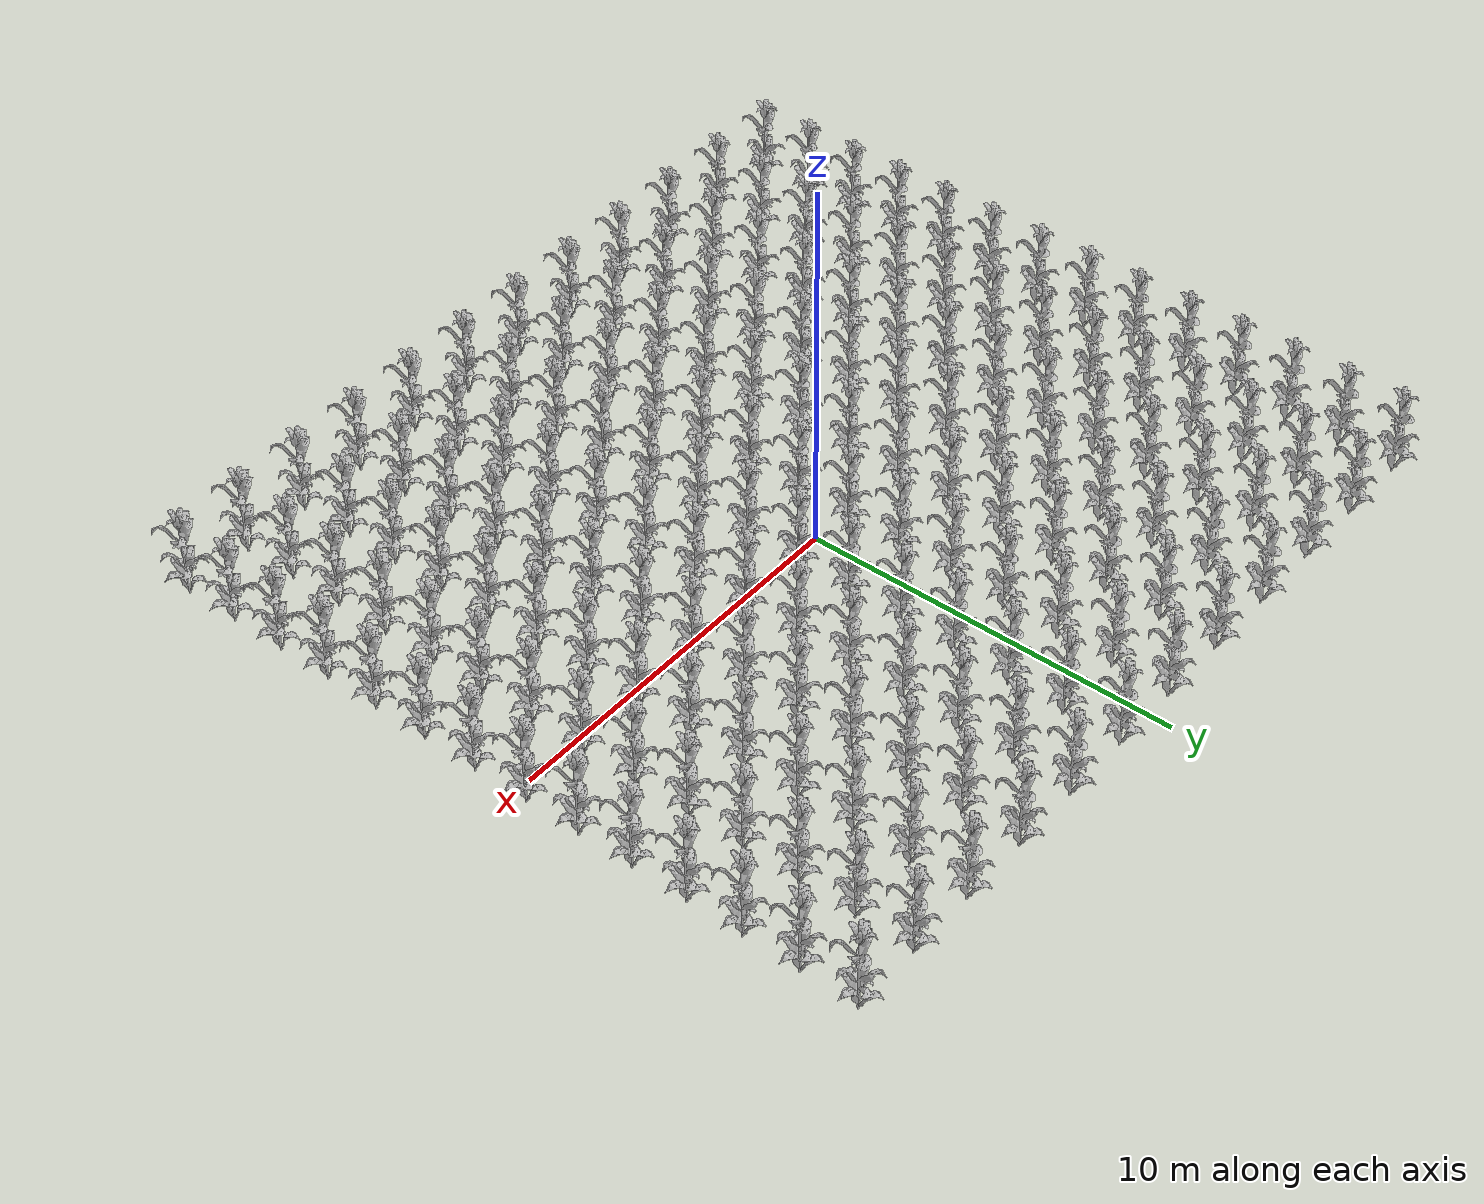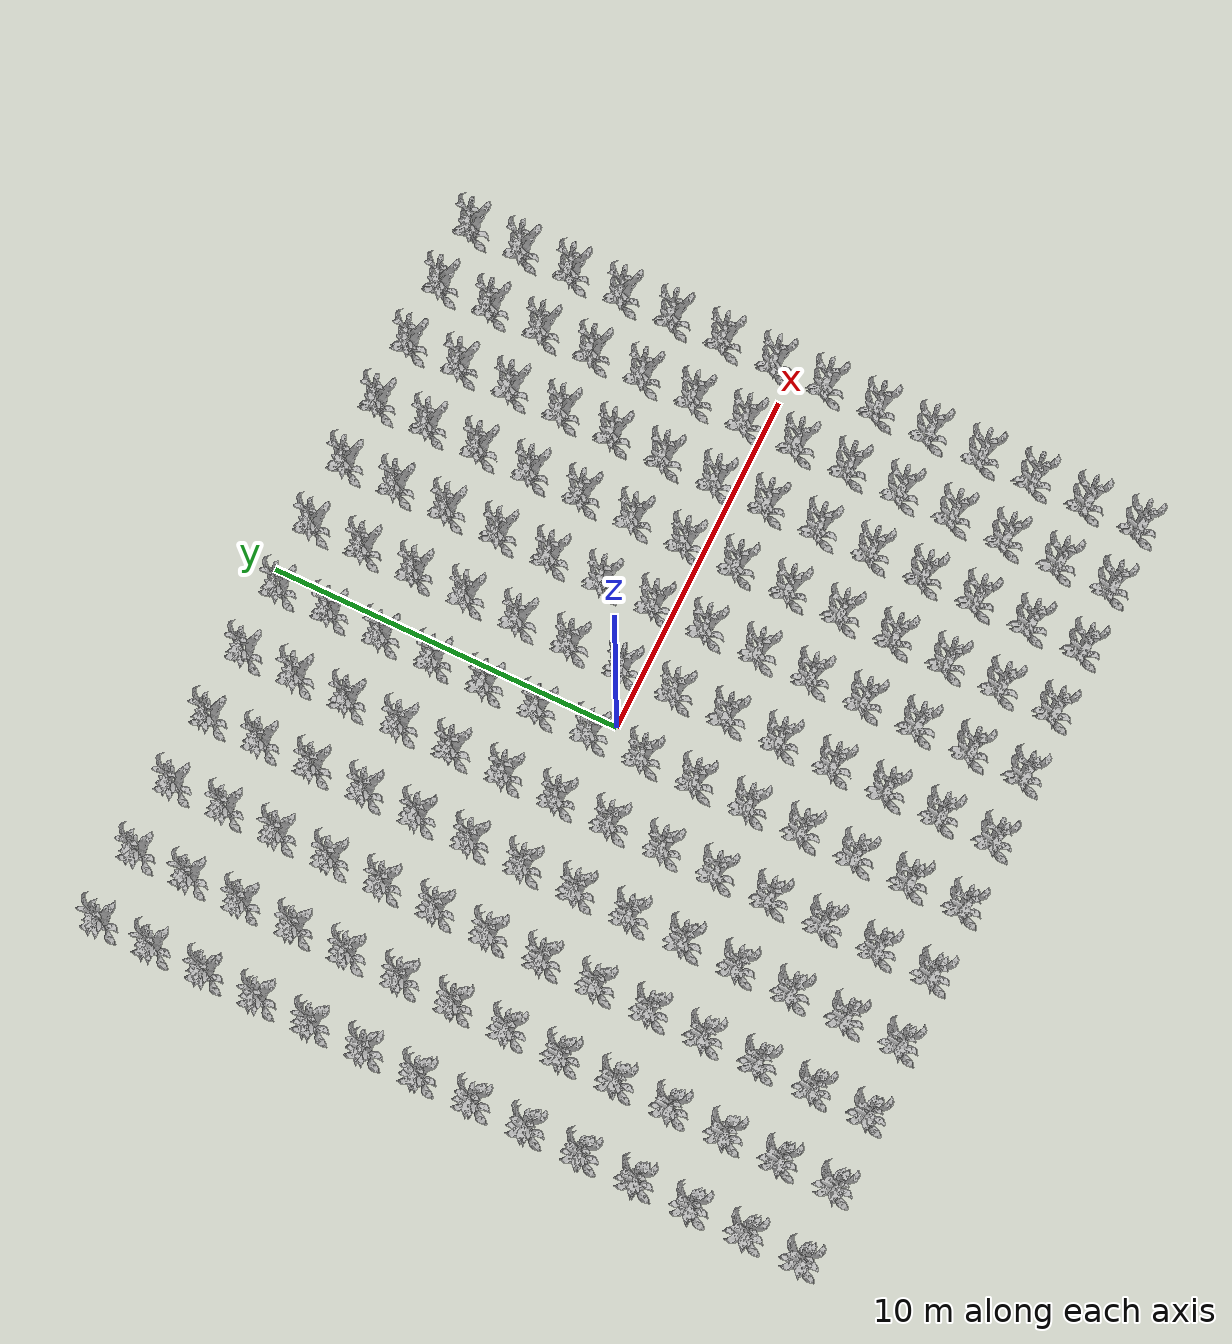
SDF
<sdf version="1.7">
 <world name="default">
  <plugin name="gazebo_ros_state" filename="libgazebo_ros_state.so"><update_rate>1.0</update_rate></plugin>
  <light name="sun" type="directional">
   <pose>0 0 10 0 -0 0</pose>
   <diffuse>0.8 0.8 0.8 1</diffuse>
   <specular>0.2 0.2 0.2 1</specular>
   <attenuation>
    <range>1000</range>
    <constant>0.9</constant>
    <linear>0.01</linear>
    <quadratic>0.001</quadratic>
   </attenuation>
   <direction>-0.5 0.1 -0.9</direction>
   <spot><inner_angle>0</inner_angle><outer_angle>0</outer_angle><falloff>0</falloff></spot>
  </light>
  <scene>
   <sky><clouds><speed>12</speed></clouds></sky>
   <ambient>0.4 0.4 0.4 1</ambient>
   <background>0.7 0.7 0.7 1</background>
   <shadows>1</shadows>
  </scene>
  <physics name="default_physics" default="0" type="ode">
   <ode>
    <solver>
     <type>quick</type>
     <iters>50</iters>
     <sor>1</sor>
     <use_dynamic_moi_rescaling>0</use_dynamic_moi_rescaling>
    </solver>
    <constraints>
     <cfm>0</cfm>
     <erp>0.2</erp>
     <contact_max_correcting_vel>1000</contact_max_correcting_vel>
     <contact_surface_layer>0.001</contact_surface_layer>
    </constraints>
   </ode>
   <max_step_size>0.004</max_step_size>
   <real_time_factor>1</real_time_factor>
   <real_time_update_rate>250</real_time_update_rate>
  </physics>
  <spherical_coordinates>
   <surface_model>EARTH_WGS84</surface_model>
   <latitude_deg>42.6129</latitude_deg>
   <longitude_deg>-5.56566</longitude_deg>
   <elevation>880</elevation>
   <heading_deg>0</heading_deg>
  </spherical_coordinates>
  <gravity>0 0 -9.8066</gravity>
  <magnetic_field>6e-06 2.3e-05 -4.2e-05</magnetic_field>
  <atmosphere type="adiabatic"/>
  <audio><device>default</device></audio>
  <model name="corn_-10.5_-10.0">
   <static>1</static>
   <link name="link">
    <inertial>
     <mass>0.2</mass>
     <inertia>
      <ixx>0.166667</ixx>
      <ixy>0</ixy>
      <ixz>0</ixz>
      <iyy>0.166667</iyy>
      <iyz>0</iyz>
      <izz>0.166667</izz>
     </inertia>
    </inertial>
    <collision name="collision">
     <geometry><mesh><uri>model://corn_2/meshes/corn.dae</uri><scale>1 1 1</scale></mesh></geometry>
     <surface>
      <friction><ode><mu>0.0</mu><mu2>0.0</mu2></ode></friction>
      <contact><ode><kp>0.0</kp><kd>0.0</kd><max_vel>0.0</max_vel><min_depth>0.002</min_depth></ode></contact>
     </surface>
    </collision>
    <visual name="visual">
     <geometry><mesh><uri>model://corn_2/meshes/corn.dae</uri><scale>1 1 1</scale></mesh></geometry>
    </visual>
    <velocity_decay><linear>0</linear><angular>0</angular></velocity_decay>
   </link>
   <pose>-10.5 -10 0.15 0 -0 0</pose>
  </model>
  <model name="corn_-10.5_-8.5">
   <static>1</static>
   <link name="link">
    <inertial>
     <mass>0.2</mass>
     <inertia>
      <ixx>0.166667</ixx>
      <ixy>0</ixy>
      <ixz>0</ixz>
      <iyy>0.166667</iyy>
      <iyz>0</iyz>
      <izz>0.166667</izz>
     </inertia>
    </inertial>
    <collision name="collision">
     <geometry><mesh><uri>model://corn_2/meshes/corn.dae</uri><scale>1 1 1</scale></mesh></geometry>
     <surface>
      <friction><ode><mu>0.0</mu><mu2>0.0</mu2></ode></friction>
      <contact><ode><kp>0.0</kp><kd>0.0</kd><max_vel>0.0</max_vel><min_depth>0.002</min_depth></ode></contact>
     </surface>
    </collision>
    <visual name="visual">
     <geometry><mesh><uri>model://corn_2/meshes/corn.dae</uri><scale>1 1 1</scale></mesh></geometry>
    </visual>
    <velocity_decay><linear>0</linear><angular>0</angular></velocity_decay>
   </link>
   <pose>-10.5 -8.5 0.15 0 -0 0</pose>
  </model>
  <model name="corn_-10.5_-7.0">
   <static>1</static>
   <link name="link">
    <inertial>
     <mass>0.2</mass>
     <inertia>
      <ixx>0.166667</ixx>
      <ixy>0</ixy>
      <ixz>0</ixz>
      <iyy>0.166667</iyy>
      <iyz>0</iyz>
      <izz>0.166667</izz>
     </inertia>
    </inertial>
    <collision name="collision">
     <geometry><mesh><uri>model://corn_2/meshes/corn.dae</uri><scale>1 1 1</scale></mesh></geometry>
     <surface>
      <friction><ode><mu>0.0</mu><mu2>0.0</mu2></ode></friction>
      <contact><ode><kp>0.0</kp><kd>0.0</kd><max_vel>0.0</max_vel><min_depth>0.002</min_depth></ode></contact>
     </surface>
    </collision>
    <visual name="visual">
     <geometry><mesh><uri>model://corn_2/meshes/corn.dae</uri><scale>1 1 1</scale></mesh></geometry>
    </visual>
    <velocity_decay><linear>0</linear><angular>0</angular></velocity_decay>
   </link>
   <pose>-10.5 -7 0.15 0 -0 0</pose>
  </model>
  <model name="corn_-10.5_-5.5">
   <static>1</static>
   <link name="link">
    <inertial>
     <mass>0.2</mass>
     <inertia>
      <ixx>0.166667</ixx>
      <ixy>0</ixy>
      <ixz>0</ixz>
      <iyy>0.166667</iyy>
      <iyz>0</iyz>
      <izz>0.166667</izz>
     </inertia>
    </inertial>
    <collision name="collision">
     <geometry><mesh><uri>model://corn_2/meshes/corn.dae</uri><scale>1 1 1</scale></mesh></geometry>
     <surface>
      <friction><ode><mu>0.0</mu><mu2>0.0</mu2></ode></friction>
      <contact><ode><kp>0.0</kp><kd>0.0</kd><max_vel>0.0</max_vel><min_depth>0.002</min_depth></ode></contact>
     </surface>
    </collision>
    <visual name="visual">
     <geometry><mesh><uri>model://corn_2/meshes/corn.dae</uri><scale>1 1 1</scale></mesh></geometry>
    </visual>
    <velocity_decay><linear>0</linear><angular>0</angular></velocity_decay>
   </link>
   <pose>-10.5 -5.5 0.15 0 -0 0</pose>
  </model>
  <model name="corn_-10.5_-4.0">
   <static>1</static>
   <link name="link">
    <inertial>
     <mass>0.2</mass>
     <inertia>
      <ixx>0.166667</ixx>
      <ixy>0</ixy>
      <ixz>0</ixz>
      <iyy>0.166667</iyy>
      <iyz>0</iyz>
      <izz>0.166667</izz>
     </inertia>
    </inertial>
    <collision name="collision">
     <geometry><mesh><uri>model://corn_2/meshes/corn.dae</uri><scale>1 1 1</scale></mesh></geometry>
     <surface>
      <friction><ode><mu>0.0</mu><mu2>0.0</mu2></ode></friction>
      <contact><ode><kp>0.0</kp><kd>0.0</kd><max_vel>0.0</max_vel><min_depth>0.002</min_depth></ode></contact>
     </surface>
    </collision>
    <visual name="visual">
     <geometry><mesh><uri>model://corn_2/meshes/corn.dae</uri><scale>1 1 1</scale></mesh></geometry>
    </visual>
    <velocity_decay><linear>0</linear><angular>0</angular></velocity_decay>
   </link>
   <pose>-10.5 -4 0.15 0 -0 0</pose>
  </model>
  <model name="corn_-10.5_-2.5">
   <static>1</static>
   <link name="link">
    <inertial>
     <mass>0.2</mass>
     <inertia>
      <ixx>0.166667</ixx>
      <ixy>0</ixy>
      <ixz>0</ixz>
      <iyy>0.166667</iyy>
      <iyz>0</iyz>
      <izz>0.166667</izz>
     </inertia>
    </inertial>
    <collision name="collision">
     <geometry><mesh><uri>model://corn_2/meshes/corn.dae</uri><scale>1 1 1</scale></mesh></geometry>
     <surface>
      <friction><ode><mu>0.0</mu><mu2>0.0</mu2></ode></friction>
      <contact><ode><kp>0.0</kp><kd>0.0</kd><max_vel>0.0</max_vel><min_depth>0.002</min_depth></ode></contact>
     </surface>
    </collision>
    <visual name="visual">
     <geometry><mesh><uri>model://corn_2/meshes/corn.dae</uri><scale>1 1 1</scale></mesh></geometry>
    </visual>
    <velocity_decay><linear>0</linear><angular>0</angular></velocity_decay>
   </link>
   <pose>-10.5 -2.5 0.15 0 -0 0</pose>
  </model>
  <model name="corn_-10.5_-1.0">
   <static>1</static>
   <link name="link">
    <inertial>
     <mass>0.2</mass>
     <inertia>
      <ixx>0.166667</ixx>
      <ixy>0</ixy>
      <ixz>0</ixz>
      <iyy>0.166667</iyy>
      <iyz>0</iyz>
      <izz>0.166667</izz>
     </inertia>
    </inertial>
    <collision name="collision">
     <geometry><mesh><uri>model://corn_2/meshes/corn.dae</uri><scale>1 1 1</scale></mesh></geometry>
     <surface>
      <friction><ode><mu>0.0</mu><mu2>0.0</mu2></ode></friction>
      <contact><ode><kp>0.0</kp><kd>0.0</kd><max_vel>0.0</max_vel><min_depth>0.002</min_depth></ode></contact>
     </surface>
    </collision>
    <visual name="visual">
     <geometry><mesh><uri>model://corn_2/meshes/corn.dae</uri><scale>1 1 1</scale></mesh></geometry>
    </visual>
    <velocity_decay><linear>0</linear><angular>0</angular></velocity_decay>
   </link>
   <pose>-10.5 -1 0.15 0 -0 0</pose>
  </model>
  <model name="corn_-10.5_0.5">
   <static>1</static>
   <link name="link">
    <inertial>
     <mass>0.2</mass>
     <inertia>
      <ixx>0.166667</ixx>
      <ixy>0</ixy>
      <ixz>0</ixz>
      <iyy>0.166667</iyy>
      <iyz>0</iyz>
      <izz>0.166667</izz>
     </inertia>
    </inertial>
    <collision name="collision">
     <geometry><mesh><uri>model://corn_2/meshes/corn.dae</uri><scale>1 1 1</scale></mesh></geometry>
     <surface>
      <friction><ode><mu>0.0</mu><mu2>0.0</mu2></ode></friction>
      <contact><ode><kp>0.0</kp><kd>0.0</kd><max_vel>0.0</max_vel><min_depth>0.002</min_depth></ode></contact>
     </surface>
    </collision>
    <visual name="visual">
     <geometry><mesh><uri>model://corn_2/meshes/corn.dae</uri><scale>1 1 1</scale></mesh></geometry>
    </visual>
    <velocity_decay><linear>0</linear><angular>0</angular></velocity_decay>
   </link>
   <pose>-10.5 0.5 0.15 0 -0 0</pose>
  </model>
  <model name="corn_-10.5_2.0">
   <static>1</static>
   <link name="link">
    <inertial>
     <mass>0.2</mass>
     <inertia>
      <ixx>0.166667</ixx>
      <ixy>0</ixy>
      <ixz>0</ixz>
      <iyy>0.166667</iyy>
      <iyz>0</iyz>
      <izz>0.166667</izz>
     </inertia>
    </inertial>
    <collision name="collision">
     <geometry><mesh><uri>model://corn_2/meshes/corn.dae</uri><scale>1 1 1</scale></mesh></geometry>
     <surface>
      <friction><ode><mu>0.0</mu><mu2>0.0</mu2></ode></friction>
      <contact><ode><kp>0.0</kp><kd>0.0</kd><max_vel>0.0</max_vel><min_depth>0.002</min_depth></ode></contact>
     </surface>
    </collision>
    <visual name="visual">
     <geometry><mesh><uri>model://corn_2/meshes/corn.dae</uri><scale>1 1 1</scale></mesh></geometry>
    </visual>
    <velocity_decay><linear>0</linear><angular>0</angular></velocity_decay>
   </link>
   <pose>-10.5 2 0.15 0 -0 0</pose>
  </model>
  <model name="corn_-10.5_3.5">
   <static>1</static>
   <link name="link">
    <inertial>
     <mass>0.2</mass>
     <inertia>
      <ixx>0.166667</ixx>
      <ixy>0</ixy>
      <ixz>0</ixz>
      <iyy>0.166667</iyy>
      <iyz>0</iyz>
      <izz>0.166667</izz>
     </inertia>
    </inertial>
    <collision name="collision">
     <geometry><mesh><uri>model://corn_2/meshes/corn.dae</uri><scale>1 1 1</scale></mesh></geometry>
     <surface>
      <friction><ode><mu>0.0</mu><mu2>0.0</mu2></ode></friction>
      <contact><ode><kp>0.0</kp><kd>0.0</kd><max_vel>0.0</max_vel><min_depth>0.002</min_depth></ode></contact>
     </surface>
    </collision>
    <visual name="visual">
     <geometry><mesh><uri>model://corn_2/meshes/corn.dae</uri><scale>1 1 1</scale></mesh></geometry>
    </visual>
    <velocity_decay><linear>0</linear><angular>0</angular></velocity_decay>
   </link>
   <pose>-10.5 3.5 0.15 0 -0 0</pose>
  </model>
  <model name="corn_-10.5_5.0">
   <static>1</static>
   <link name="link">
    <inertial>
     <mass>0.2</mass>
     <inertia>
      <ixx>0.166667</ixx>
      <ixy>0</ixy>
      <ixz>0</ixz>
      <iyy>0.166667</iyy>
      <iyz>0</iyz>
      <izz>0.166667</izz>
     </inertia>
    </inertial>
    <collision name="collision">
     <geometry><mesh><uri>model://corn_2/meshes/corn.dae</uri><scale>1 1 1</scale></mesh></geometry>
     <surface>
      <friction><ode><mu>0.0</mu><mu2>0.0</mu2></ode></friction>
      <contact><ode><kp>0.0</kp><kd>0.0</kd><max_vel>0.0</max_vel><min_depth>0.002</min_depth></ode></contact>
     </surface>
    </collision>
    <visual name="visual">
     <geometry><mesh><uri>model://corn_2/meshes/corn.dae</uri><scale>1 1 1</scale></mesh></geometry>
    </visual>
    <velocity_decay><linear>0</linear><angular>0</angular></velocity_decay>
   </link>
   <pose>-10.5 5 0.15 0 -0 0</pose>
  </model>
  <model name="corn_-10.5_6.5">
   <static>1</static>
   <link name="link">
    <inertial>
     <mass>0.2</mass>
     <inertia>
      <ixx>0.166667</ixx>
      <ixy>0</ixy>
      <ixz>0</ixz>
      <iyy>0.166667</iyy>
      <iyz>0</iyz>
      <izz>0.166667</izz>
     </inertia>
    </inertial>
    <collision name="collision">
     <geometry><mesh><uri>model://corn_2/meshes/corn.dae</uri><scale>1 1 1</scale></mesh></geometry>
     <surface>
      <friction><ode><mu>0.0</mu><mu2>0.0</mu2></ode></friction>
      <contact><ode><kp>0.0</kp><kd>0.0</kd><max_vel>0.0</max_vel><min_depth>0.002</min_depth></ode></contact>
     </surface>
    </collision>
    <visual name="visual">
     <geometry><mesh><uri>model://corn_2/meshes/corn.dae</uri><scale>1 1 1</scale></mesh></geometry>
    </visual>
    <velocity_decay><linear>0</linear><angular>0</angular></velocity_decay>
   </link>
   <pose>-10.5 6.5 0.15 0 -0 0</pose>
  </model>
  <model name="corn_-10.5_8.0">
   <static>1</static>
   <link name="link">
    <inertial>
     <mass>0.2</mass>
     <inertia>
      <ixx>0.166667</ixx>
      <ixy>0</ixy>
      <ixz>0</ixz>
      <iyy>0.166667</iyy>
      <iyz>0</iyz>
      <izz>0.166667</izz>
     </inertia>
    </inertial>
    <collision name="collision">
     <geometry><mesh><uri>model://corn_2/meshes/corn.dae</uri><scale>1 1 1</scale></mesh></geometry>
     <surface>
      <friction><ode><mu>0.0</mu><mu2>0.0</mu2></ode></friction>
      <contact><ode><kp>0.0</kp><kd>0.0</kd><max_vel>0.0</max_vel><min_depth>0.002</min_depth></ode></contact>
     </surface>
    </collision>
    <visual name="visual">
     <geometry><mesh><uri>model://corn_2/meshes/corn.dae</uri><scale>1 1 1</scale></mesh></geometry>
    </visual>
    <velocity_decay><linear>0</linear><angular>0</angular></velocity_decay>
   </link>
   <pose>-10.5 8 0.15 0 -0 0</pose>
  </model>
  <model name="corn_-10.5_9.5">
   <static>1</static>
   <link name="link">
    <inertial>
     <mass>0.2</mass>
     <inertia>
      <ixx>0.166667</ixx>
      <ixy>0</ixy>
      <ixz>0</ixz>
      <iyy>0.166667</iyy>
      <iyz>0</iyz>
      <izz>0.166667</izz>
     </inertia>
    </inertial>
    <collision name="collision">
     <geometry><mesh><uri>model://corn_2/meshes/corn.dae</uri><scale>1 1 1</scale></mesh></geometry>
     <surface>
      <friction><ode><mu>0.0</mu><mu2>0.0</mu2></ode></friction>
      <contact><ode><kp>0.0</kp><kd>0.0</kd><max_vel>0.0</max_vel><min_depth>0.002</min_depth></ode></contact>
     </surface>
    </collision>
    <visual name="visual">
     <geometry><mesh><uri>model://corn_2/meshes/corn.dae</uri><scale>1 1 1</scale></mesh></geometry>
    </visual>
    <velocity_decay><linear>0</linear><angular>0</angular></velocity_decay>
   </link>
   <pose>-10.5 9.5 0.15 0 -0 0</pose>
  </model>
  <model name="corn_-8.508_-10.0">
   <static>1</static>
   <link name="link">
    <inertial>
     <mass>0.2</mass>
     <inertia>
      <ixx>0.166667</ixx>
      <ixy>0</ixy>
      <ixz>0</ixz>
      <iyy>0.166667</iyy>
      <iyz>0</iyz>
      <izz>0.166667</izz>
     </inertia>
    </inertial>
    <collision name="collision">
     <geometry><mesh><uri>model://corn_2/meshes/corn.dae</uri><scale>1 1 1</scale></mesh></geometry>
     <surface>
      <friction><ode><mu>0.0</mu><mu2>0.0</mu2></ode></friction>
      <contact><ode><kp>0.0</kp><kd>0.0</kd><max_vel>0.0</max_vel><min_depth>0.002</min_depth></ode></contact>
     </surface>
    </collision>
    <visual name="visual">
     <geometry><mesh><uri>model://corn_2/meshes/corn.dae</uri><scale>1 1 1</scale></mesh></geometry>
    </visual>
    <velocity_decay><linear>0</linear><angular>0</angular></velocity_decay>
   </link>
   <pose>-8.508 -10 0.15 0 -0 0</pose>
  </model>
  <model name="corn_-8.508_-8.5">
   <static>1</static>
   <link name="link">
    <inertial>
     <mass>0.2</mass>
     <inertia>
      <ixx>0.166667</ixx>
      <ixy>0</ixy>
      <ixz>0</ixz>
      <iyy>0.166667</iyy>
      <iyz>0</iyz>
      <izz>0.166667</izz>
     </inertia>
    </inertial>
    <collision name="collision">
     <geometry><mesh><uri>model://corn_2/meshes/corn.dae</uri><scale>1 1 1</scale></mesh></geometry>
     <surface>
      <friction><ode><mu>0.0</mu><mu2>0.0</mu2></ode></friction>
      <contact><ode><kp>0.0</kp><kd>0.0</kd><max_vel>0.0</max_vel><min_depth>0.002</min_depth></ode></contact>
     </surface>
    </collision>
    <visual name="visual">
     <geometry><mesh><uri>model://corn_2/meshes/corn.dae</uri><scale>1 1 1</scale></mesh></geometry>
    </visual>
    <velocity_decay><linear>0</linear><angular>0</angular></velocity_decay>
   </link>
   <pose>-8.508 -8.5 0.15 0 -0 0</pose>
  </model>
  <model name="corn_-8.508_-7.0">
   <static>1</static>
   <link name="link">
    <inertial>
     <mass>0.2</mass>
     <inertia>
      <ixx>0.166667</ixx>
      <ixy>0</ixy>
      <ixz>0</ixz>
      <iyy>0.166667</iyy>
      <iyz>0</iyz>
      <izz>0.166667</izz>
     </inertia>
    </inertial>
    <collision name="collision">
     <geometry><mesh><uri>model://corn_2/meshes/corn.dae</uri><scale>1 1 1</scale></mesh></geometry>
     <surface>
      <friction><ode><mu>0.0</mu><mu2>0.0</mu2></ode></friction>
      <contact><ode><kp>0.0</kp><kd>0.0</kd><max_vel>0.0</max_vel><min_depth>0.002</min_depth></ode></contact>
     </surface>
    </collision>
    <visual name="visual">
     <geometry><mesh><uri>model://corn_2/meshes/corn.dae</uri><scale>1 1 1</scale></mesh></geometry>
    </visual>
    <velocity_decay><linear>0</linear><angular>0</angular></velocity_decay>
   </link>
   <pose>-8.508 -7 0.15 0 -0 0</pose>
  </model>
  <model name="corn_-8.508_-5.5">
   <static>1</static>
   <link name="link">
    <inertial>
     <mass>0.2</mass>
     <inertia>
      <ixx>0.166667</ixx>
      <ixy>0</ixy>
      <ixz>0</ixz>
      <iyy>0.166667</iyy>
      <iyz>0</iyz>
      <izz>0.166667</izz>
     </inertia>
    </inertial>
    <collision name="collision">
     <geometry><mesh><uri>model://corn_2/meshes/corn.dae</uri><scale>1 1 1</scale></mesh></geometry>
     <surface>
      <friction><ode><mu>0.0</mu><mu2>0.0</mu2></ode></friction>
      <contact><ode><kp>0.0</kp><kd>0.0</kd><max_vel>0.0</max_vel><min_depth>0.002</min_depth></ode></contact>
     </surface>
    </collision>
    <visual name="visual">
     <geometry><mesh><uri>model://corn_2/meshes/corn.dae</uri><scale>1 1 1</scale></mesh></geometry>
    </visual>
    <velocity_decay><linear>0</linear><angular>0</angular></velocity_decay>
   </link>
   <pose>-8.508 -5.5 0.15 0 -0 0</pose>
  </model>
  <model name="corn_-8.508_-4.0">
   <static>1</static>
   <link name="link">
    <inertial>
     <mass>0.2</mass>
     <inertia>
      <ixx>0.166667</ixx>
      <ixy>0</ixy>
      <ixz>0</ixz>
      <iyy>0.166667</iyy>
      <iyz>0</iyz>
      <izz>0.166667</izz>
     </inertia>
    </inertial>
    <collision name="collision">
     <geometry><mesh><uri>model://corn_2/meshes/corn.dae</uri><scale>1 1 1</scale></mesh></geometry>
     <surface>
      <friction><ode><mu>0.0</mu><mu2>0.0</mu2></ode></friction>
      <contact><ode><kp>0.0</kp><kd>0.0</kd><max_vel>0.0</max_vel><min_depth>0.002</min_depth></ode></contact>
     </surface>
    </collision>
    <visual name="visual">
     <geometry><mesh><uri>model://corn_2/meshes/corn.dae</uri><scale>1 1 1</scale></mesh></geometry>
    </visual>
    <velocity_decay><linear>0</linear><angular>0</angular></velocity_decay>
   </link>
   <pose>-8.508 -4 0.15 0 -0 0</pose>
  </model>
  <model name="corn_-8.508_-2.5">
   <static>1</static>
   <link name="link">
    <inertial>
     <mass>0.2</mass>
     <inertia>
      <ixx>0.166667</ixx>
      <ixy>0</ixy>
      <ixz>0</ixz>
      <iyy>0.166667</iyy>
      <iyz>0</iyz>
      <izz>0.166667</izz>
     </inertia>
    </inertial>
    <collision name="collision">
     <geometry><mesh><uri>model://corn_2/meshes/corn.dae</uri><scale>1 1 1</scale></mesh></geometry>
     <surface>
      <friction><ode><mu>0.0</mu><mu2>0.0</mu2></ode></friction>
      <contact><ode><kp>0.0</kp><kd>0.0</kd><max_vel>0.0</max_vel><min_depth>0.002</min_depth></ode></contact>
     </surface>
    </collision>
    <visual name="visual">
     <geometry><mesh><uri>model://corn_2/meshes/corn.dae</uri><scale>1 1 1</scale></mesh></geometry>
    </visual>
    <velocity_decay><linear>0</linear><angular>0</angular></velocity_decay>
   </link>
   <pose>-8.508 -2.5 0.15 0 -0 0</pose>
  </model>
  <model name="corn_-8.508_-1.0">
   <static>1</static>
   <link name="link">
    <inertial>
     <mass>0.2</mass>
     <inertia>
      <ixx>0.166667</ixx>
      <ixy>0</ixy>
      <ixz>0</ixz>
      <iyy>0.166667</iyy>
      <iyz>0</iyz>
      <izz>0.166667</izz>
     </inertia>
    </inertial>
    <collision name="collision">
     <geometry><mesh><uri>model://corn_2/meshes/corn.dae</uri><scale>1 1 1</scale></mesh></geometry>
     <surface>
      <friction><ode><mu>0.0</mu><mu2>0.0</mu2></ode></friction>
      <contact><ode><kp>0.0</kp><kd>0.0</kd><max_vel>0.0</max_vel><min_depth>0.002</min_depth></ode></contact>
     </surface>
    </collision>
    <visual name="visual">
     <geometry><mesh><uri>model://corn_2/meshes/corn.dae</uri><scale>1 1 1</scale></mesh></geometry>
    </visual>
    <velocity_decay><linear>0</linear><angular>0</angular></velocity_decay>
   </link>
   <pose>-8.508 -1 0.15 0 -0 0</pose>
  </model>
  <model name="corn_-8.508_0.5">
   <static>1</static>
   <link name="link">
    <inertial>
     <mass>0.2</mass>
     <inertia>
      <ixx>0.166667</ixx>
      <ixy>0</ixy>
      <ixz>0</ixz>
      <iyy>0.166667</iyy>
      <iyz>0</iyz>
      <izz>0.166667</izz>
     </inertia>
    </inertial>
    <collision name="collision">
     <geometry><mesh><uri>model://corn_2/meshes/corn.dae</uri><scale>1 1 1</scale></mesh></geometry>
     <surface>
      <friction><ode><mu>0.0</mu><mu2>0.0</mu2></ode></friction>
      <contact><ode><kp>0.0</kp><kd>0.0</kd><max_vel>0.0</max_vel><min_depth>0.002</min_depth></ode></contact>
     </surface>
    </collision>
    <visual name="visual">
     <geometry><mesh><uri>model://corn_2/meshes/corn.dae</uri><scale>1 1 1</scale></mesh></geometry>
    </visual>
    <velocity_decay><linear>0</linear><angular>0</angular></velocity_decay>
   </link>
   <pose>-8.508 0.5 0.15 0 -0 0</pose>
  </model>
  <model name="corn_-8.508_2.0">
   <static>1</static>
   <link name="link">
    <inertial>
     <mass>0.2</mass>
     <inertia>
      <ixx>0.166667</ixx>
      <ixy>0</ixy>
      <ixz>0</ixz>
      <iyy>0.166667</iyy>
      <iyz>0</iyz>
      <izz>0.166667</izz>
     </inertia>
    </inertial>
    <collision name="collision">
     <geometry><mesh><uri>model://corn_2/meshes/corn.dae</uri><scale>1 1 1</scale></mesh></geometry>
     <surface>
      <friction><ode><mu>0.0</mu><mu2>0.0</mu2></ode></friction>
      <contact><ode><kp>0.0</kp><kd>0.0</kd><max_vel>0.0</max_vel><min_depth>0.002</min_depth></ode></contact>
     </surface>
    </collision>
    <visual name="visual">
     <geometry><mesh><uri>model://corn_2/meshes/corn.dae</uri><scale>1 1 1</scale></mesh></geometry>
    </visual>
    <velocity_decay><linear>0</linear><angular>0</angular></velocity_decay>
   </link>
   <pose>-8.508 2 0.15 0 -0 0</pose>
  </model>
  <model name="corn_-8.508_3.5">
   <static>1</static>
   <link name="link">
    <inertial>
     <mass>0.2</mass>
     <inertia>
      <ixx>0.166667</ixx>
      <ixy>0</ixy>
      <ixz>0</ixz>
      <iyy>0.166667</iyy>
      <iyz>0</iyz>
      <izz>0.166667</izz>
     </inertia>
    </inertial>
    <collision name="collision">
     <geometry><mesh><uri>model://corn_2/meshes/corn.dae</uri><scale>1 1 1</scale></mesh></geometry>
     <surface>
      <friction><ode><mu>0.0</mu><mu2>0.0</mu2></ode></friction>
      <contact><ode><kp>0.0</kp><kd>0.0</kd><max_vel>0.0</max_vel><min_depth>0.002</min_depth></ode></contact>
     </surface>
    </collision>
    <visual name="visual">
     <geometry><mesh><uri>model://corn_2/meshes/corn.dae</uri><scale>1 1 1</scale></mesh></geometry>
    </visual>
    <velocity_decay><linear>0</linear><angular>0</angular></velocity_decay>
   </link>
   <pose>-8.508 3.5 0.15 0 -0 0</pose>
  </model>
  <model name="corn_-8.508_5.0">
   <static>1</static>
   <link name="link">
    <inertial>
     <mass>0.2</mass>
     <inertia>
      <ixx>0.166667</ixx>
      <ixy>0</ixy>
      <ixz>0</ixz>
      <iyy>0.166667</iyy>
      <iyz>0</iyz>
      <izz>0.166667</izz>
     </inertia>
    </inertial>
    <collision name="collision">
     <geometry><mesh><uri>model://corn_2/meshes/corn.dae</uri><scale>1 1 1</scale></mesh></geometry>
     <surface>
      <friction><ode><mu>0.0</mu><mu2>0.0</mu2></ode></friction>
      <contact><ode><kp>0.0</kp><kd>0.0</kd><max_vel>0.0</max_vel><min_depth>0.002</min_depth></ode></contact>
     </surface>
    </collision>
    <visual name="visual">
     <geometry><mesh><uri>model://corn_2/meshes/corn.dae</uri><scale>1 1 1</scale></mesh></geometry>
    </visual>
    <velocity_decay><linear>0</linear><angular>0</angular></velocity_decay>
   </link>
   <pose>-8.508 5 0.15 0 -0 0</pose>
  </model>
  <model name="corn_-8.508_6.5">
   <static>1</static>
   <link name="link">
    <inertial>
     <mass>0.2</mass>
     <inertia>
      <ixx>0.166667</ixx>
      <ixy>0</ixy>
      <ixz>0</ixz>
      <iyy>0.166667</iyy>
      <iyz>0</iyz>
      <izz>0.166667</izz>
     </inertia>
    </inertial>
    <collision name="collision">
     <geometry><mesh><uri>model://corn_2/meshes/corn.dae</uri><scale>1 1 1</scale></mesh></geometry>
     <surface>
      <friction><ode><mu>0.0</mu><mu2>0.0</mu2></ode></friction>
      <contact><ode><kp>0.0</kp><kd>0.0</kd><max_vel>0.0</max_vel><min_depth>0.002</min_depth></ode></contact>
     </surface>
    </collision>
    <visual name="visual">
     <geometry><mesh><uri>model://corn_2/meshes/corn.dae</uri><scale>1 1 1</scale></mesh></geometry>
    </visual>
    <velocity_decay><linear>0</linear><angular>0</angular></velocity_decay>
   </link>
   <pose>-8.508 6.5 0.15 0 -0 0</pose>
  </model>
  <model name="corn_-8.508_8.0">
   <static>1</static>
   <link name="link">
    <inertial>
     <mass>0.2</mass>
     <inertia>
      <ixx>0.166667</ixx>
      <ixy>0</ixy>
      <ixz>0</ixz>
      <iyy>0.166667</iyy>
      <iyz>0</iyz>
      <izz>0.166667</izz>
     </inertia>
    </inertial>
    <collision name="collision">
     <geometry><mesh><uri>model://corn_2/meshes/corn.dae</uri><scale>1 1 1</scale></mesh></geometry>
     <surface>
      <friction><ode><mu>0.0</mu><mu2>0.0</mu2></ode></friction>
      <contact><ode><kp>0.0</kp><kd>0.0</kd><max_vel>0.0</max_vel><min_depth>0.002</min_depth></ode></contact>
     </surface>
    </collision>
    <visual name="visual">
     <geometry><mesh><uri>model://corn_2/meshes/corn.dae</uri><scale>1 1 1</scale></mesh></geometry>
    </visual>
    <velocity_decay><linear>0</linear><angular>0</angular></velocity_decay>
   </link>
   <pose>-8.508 8 0.15 0 -0 0</pose>
  </model>
  <model name="corn_-8.508_9.5">
   <static>1</static>
   <link name="link">
    <inertial>
     <mass>0.2</mass>
     <inertia>
      <ixx>0.166667</ixx>
      <ixy>0</ixy>
      <ixz>0</ixz>
      <iyy>0.166667</iyy>
      <iyz>0</iyz>
      <izz>0.166667</izz>
     </inertia>
    </inertial>
    <collision name="collision">
     <geometry><mesh><uri>model://corn_2/meshes/corn.dae</uri><scale>1 1 1</scale></mesh></geometry>
     <surface>
      <friction><ode><mu>0.0</mu><mu2>0.0</mu2></ode></friction>
      <contact><ode><kp>0.0</kp><kd>0.0</kd><max_vel>0.0</max_vel><min_depth>0.002</min_depth></ode></contact>
     </surface>
    </collision>
    <visual name="visual">
     <geometry><mesh><uri>model://corn_2/meshes/corn.dae</uri><scale>1 1 1</scale></mesh></geometry>
    </visual>
    <velocity_decay><linear>0</linear><angular>0</angular></velocity_decay>
   </link>
   <pose>-8.508 9.5 0.15 0 -0 0</pose>
  </model>
  <model name="corn_-6.531936_-10.0">
   <static>1</static>
   <link name="link">
    <inertial>
     <mass>0.2</mass>
     <inertia>
      <ixx>0.166667</ixx>
      <ixy>0</ixy>
      <ixz>0</ixz>
      <iyy>0.166667</iyy>
      <iyz>0</iyz>
      <izz>0.166667</izz>
     </inertia>
    </inertial>
    <collision name="collision">
     <geometry><mesh><uri>model://corn_2/meshes/corn.dae</uri><scale>1 1 1</scale></mesh></geometry>
     <surface>
      <friction><ode><mu>0.0</mu><mu2>0.0</mu2></ode></friction>
      <contact><ode><kp>0.0</kp><kd>0.0</kd><max_vel>0.0</max_vel><min_depth>0.002</min_depth></ode></contact>
     </surface>
    </collision>
    <visual name="visual">
     <geometry><mesh><uri>model://corn_2/meshes/corn.dae</uri><scale>1 1 1</scale></mesh></geometry>
    </visual>
    <velocity_decay><linear>0</linear><angular>0</angular></velocity_decay>
   </link>
   <pose>-6.53194 -10 0.15 0 -0 0</pose>
  </model>
  <model name="corn_-6.531936_-8.5">
   <static>1</static>
   <link name="link">
    <inertial>
     <mass>0.2</mass>
     <inertia>
      <ixx>0.166667</ixx>
      <ixy>0</ixy>
      <ixz>0</ixz>
      <iyy>0.166667</iyy>
      <iyz>0</iyz>
      <izz>0.166667</izz>
     </inertia>
    </inertial>
    <collision name="collision">
     <geometry><mesh><uri>model://corn_2/meshes/corn.dae</uri><scale>1 1 1</scale></mesh></geometry>
     <surface>
      <friction><ode><mu>0.0</mu><mu2>0.0</mu2></ode></friction>
      <contact><ode><kp>0.0</kp><kd>0.0</kd><max_vel>0.0</max_vel><min_depth>0.002</min_depth></ode></contact>
     </surface>
    </collision>
    <visual name="visual">
     <geometry><mesh><uri>model://corn_2/meshes/corn.dae</uri><scale>1 1 1</scale></mesh></geometry>
    </visual>
    <velocity_decay><linear>0</linear><angular>0</angular></velocity_decay>
   </link>
   <pose>-6.53194 -8.5 0.15 0 -0 0</pose>
  </model>
  <model name="corn_-6.531936_-7.0">
   <static>1</static>
   <link name="link">
    <inertial>
     <mass>0.2</mass>
     <inertia>
      <ixx>0.166667</ixx>
      <ixy>0</ixy>
      <ixz>0</ixz>
      <iyy>0.166667</iyy>
      <iyz>0</iyz>
      <izz>0.166667</izz>
     </inertia>
    </inertial>
    <collision name="collision">
     <geometry><mesh><uri>model://corn_2/meshes/corn.dae</uri><scale>1 1 1</scale></mesh></geometry>
     <surface>
      <friction><ode><mu>0.0</mu><mu2>0.0</mu2></ode></friction>
      <contact><ode><kp>0.0</kp><kd>0.0</kd><max_vel>0.0</max_vel><min_depth>0.002</min_depth></ode></contact>
     </surface>
    </collision>
    <visual name="visual">
     <geometry><mesh><uri>model://corn_2/meshes/corn.dae</uri><scale>1 1 1</scale></mesh></geometry>
    </visual>
    <velocity_decay><linear>0</linear><angular>0</angular></velocity_decay>
   </link>
   <pose>-6.53194 -7 0.15 0 -0 0</pose>
  </model>
  <model name="corn_-6.531936_-5.5">
   <static>1</static>
   <link name="link">
    <inertial>
     <mass>0.2</mass>
     <inertia>
      <ixx>0.166667</ixx>
      <ixy>0</ixy>
      <ixz>0</ixz>
      <iyy>0.166667</iyy>
      <iyz>0</iyz>
      <izz>0.166667</izz>
     </inertia>
    </inertial>
    <collision name="collision">
     <geometry><mesh><uri>model://corn_2/meshes/corn.dae</uri><scale>1 1 1</scale></mesh></geometry>
     <surface>
      <friction><ode><mu>0.0</mu><mu2>0.0</mu2></ode></friction>
      <contact><ode><kp>0.0</kp><kd>0.0</kd><max_vel>0.0</max_vel><min_depth>0.002</min_depth></ode></contact>
     </surface>
    </collision>
    <visual name="visual">
     <geometry><mesh><uri>model://corn_2/meshes/corn.dae</uri><scale>1 1 1</scale></mesh></geometry>
    </visual>
    <velocity_decay><linear>0</linear><angular>0</angular></velocity_decay>
   </link>
   <pose>-6.53194 -5.5 0.15 0 -0 0</pose>
  </model>
  <model name="corn_-6.531936_-4.0">
   <static>1</static>
   <link name="link">
    <inertial>
     <mass>0.2</mass>
     <inertia>
      <ixx>0.166667</ixx>
      <ixy>0</ixy>
      <ixz>0</ixz>
      <iyy>0.166667</iyy>
      <iyz>0</iyz>
      <izz>0.166667</izz>
     </inertia>
    </inertial>
    <collision name="collision">
     <geometry><mesh><uri>model://corn_2/meshes/corn.dae</uri><scale>1 1 1</scale></mesh></geometry>
     <surface>
      <friction><ode><mu>0.0</mu><mu2>0.0</mu2></ode></friction>
      <contact><ode><kp>0.0</kp><kd>0.0</kd><max_vel>0.0</max_vel><min_depth>0.002</min_depth></ode></contact>
     </surface>
    </collision>
    <visual name="visual">
     <geometry><mesh><uri>model://corn_2/meshes/corn.dae</uri><scale>1 1 1</scale></mesh></geometry>
    </visual>
    <velocity_decay><linear>0</linear><angular>0</angular></velocity_decay>
   </link>
   <pose>-6.53194 -4 0.15 0 -0 0</pose>
  </model>
  <model name="corn_-6.531936_-2.5">
   <static>1</static>
   <link name="link">
    <inertial>
     <mass>0.2</mass>
     <inertia>
      <ixx>0.166667</ixx>
      <ixy>0</ixy>
      <ixz>0</ixz>
      <iyy>0.166667</iyy>
      <iyz>0</iyz>
      <izz>0.166667</izz>
     </inertia>
    </inertial>
    <collision name="collision">
     <geometry><mesh><uri>model://corn_2/meshes/corn.dae</uri><scale>1 1 1</scale></mesh></geometry>
     <surface>
      <friction><ode><mu>0.0</mu><mu2>0.0</mu2></ode></friction>
      <contact><ode><kp>0.0</kp><kd>0.0</kd><max_vel>0.0</max_vel><min_depth>0.002</min_depth></ode></contact>
     </surface>
    </collision>
    <visual name="visual">
     <geometry><mesh><uri>model://corn_2/meshes/corn.dae</uri><scale>1 1 1</scale></mesh></geometry>
    </visual>
    <velocity_decay><linear>0</linear><angular>0</angular></velocity_decay>
   </link>
   <pose>-6.53194 -2.5 0.15 0 -0 0</pose>
  </model>
  <model name="corn_-6.531936_-1.0">
   <static>1</static>
   <link name="link">
    <inertial>
     <mass>0.2</mass>
     <inertia>
      <ixx>0.166667</ixx>
      <ixy>0</ixy>
      <ixz>0</ixz>
      <iyy>0.166667</iyy>
      <iyz>0</iyz>
      <izz>0.166667</izz>
     </inertia>
    </inertial>
    <collision name="collision">
     <geometry><mesh><uri>model://corn_2/meshes/corn.dae</uri><scale>1 1 1</scale></mesh></geometry>
     <surface>
      <friction><ode><mu>0.0</mu><mu2>0.0</mu2></ode></friction>
      <contact><ode><kp>0.0</kp><kd>0.0</kd><max_vel>0.0</max_vel><min_depth>0.002</min_depth></ode></contact>
     </surface>
    </collision>
    <visual name="visual">
     <geometry><mesh><uri>model://corn_2/meshes/corn.dae</uri><scale>1 1 1</scale></mesh></geometry>
    </visual>
    <velocity_decay><linear>0</linear><angular>0</angular></velocity_decay>
   </link>
   <pose>-6.53194 -1 0.15 0 -0 0</pose>
  </model>
  <model name="corn_-6.531936_0.5">
   <static>1</static>
   <link name="link">
    <inertial>
     <mass>0.2</mass>
     <inertia>
      <ixx>0.166667</ixx>
      <ixy>0</ixy>
      <ixz>0</ixz>
      <iyy>0.166667</iyy>
      <iyz>0</iyz>
      <izz>0.166667</izz>
     </inertia>
    </inertial>
    <collision name="collision">
     <geometry><mesh><uri>model://corn_2/meshes/corn.dae</uri><scale>1 1 1</scale></mesh></geometry>
     <surface>
      <friction><ode><mu>0.0</mu><mu2>0.0</mu2></ode></friction>
      <contact><ode><kp>0.0</kp><kd>0.0</kd><max_vel>0.0</max_vel><min_depth>0.002</min_depth></ode></contact>
     </surface>
    </collision>
    <visual name="visual">
     <geometry><mesh><uri>model://corn_2/meshes/corn.dae</uri><scale>1 1 1</scale></mesh></geometry>
    </visual>
    <velocity_decay><linear>0</linear><angular>0</angular></velocity_decay>
   </link>
   <pose>-6.53194 0.5 0.15 0 -0 0</pose>
  </model>
  <model name="corn_-6.531936_2.0">
   <static>1</static>
   <link name="link">
    <inertial>
     <mass>0.2</mass>
     <inertia>
      <ixx>0.166667</ixx>
      <ixy>0</ixy>
      <ixz>0</ixz>
      <iyy>0.166667</iyy>
      <iyz>0</iyz>
      <izz>0.166667</izz>
     </inertia>
    </inertial>
    <collision name="collision">
     <geometry><mesh><uri>model://corn_2/meshes/corn.dae</uri><scale>1 1 1</scale></mesh></geometry>
     <surface>
      <friction><ode><mu>0.0</mu><mu2>0.0</mu2></ode></friction>
      <contact><ode><kp>0.0</kp><kd>0.0</kd><max_vel>0.0</max_vel><min_depth>0.002</min_depth></ode></contact>
     </surface>
    </collision>
    <visual name="visual">
     <geometry><mesh><uri>model://corn_2/meshes/corn.dae</uri><scale>1 1 1</scale></mesh></geometry>
    </visual>
    <velocity_decay><linear>0</linear><angular>0</angular></velocity_decay>
   </link>
   <pose>-6.53194 2 0.15 0 -0 0</pose>
  </model>
  <model name="corn_-6.531936_3.5">
   <static>1</static>
   <link name="link">
    <inertial>
     <mass>0.2</mass>
     <inertia>
      <ixx>0.166667</ixx>
      <ixy>0</ixy>
      <ixz>0</ixz>
      <iyy>0.166667</iyy>
      <iyz>0</iyz>
      <izz>0.166667</izz>
     </inertia>
    </inertial>
    <collision name="collision">
     <geometry><mesh><uri>model://corn_2/meshes/corn.dae</uri><scale>1 1 1</scale></mesh></geometry>
     <surface>
      <friction><ode><mu>0.0</mu><mu2>0.0</mu2></ode></friction>
      <contact><ode><kp>0.0</kp><kd>0.0</kd><max_vel>0.0</max_vel><min_depth>0.002</min_depth></ode></contact>
     </surface>
    </collision>
    <visual name="visual">
     <geometry><mesh><uri>model://corn_2/meshes/corn.dae</uri><scale>1 1 1</scale></mesh></geometry>
    </visual>
    <velocity_decay><linear>0</linear><angular>0</angular></velocity_decay>
   </link>
   <pose>-6.53194 3.5 0.15 0 -0 0</pose>
  </model>
  <model name="corn_-6.531936_5.0">
   <static>1</static>
   <link name="link">
    <inertial>
     <mass>0.2</mass>
     <inertia>
      <ixx>0.166667</ixx>
      <ixy>0</ixy>
      <ixz>0</ixz>
      <iyy>0.166667</iyy>
      <iyz>0</iyz>
      <izz>0.166667</izz>
     </inertia>
    </inertial>
    <collision name="collision">
     <geometry><mesh><uri>model://corn_2/meshes/corn.dae</uri><scale>1 1 1</scale></mesh></geometry>
     <surface>
      <friction><ode><mu>0.0</mu><mu2>0.0</mu2></ode></friction>
      <contact><ode><kp>0.0</kp><kd>0.0</kd><max_vel>0.0</max_vel><min_depth>0.002</min_depth></ode></contact>
     </surface>
    </collision>
    <visual name="visual">
     <geometry><mesh><uri>model://corn_2/meshes/corn.dae</uri><scale>1 1 1</scale></mesh></geometry>
    </visual>
    <velocity_decay><linear>0</linear><angular>0</angular></velocity_decay>
   </link>
   <pose>-6.53194 5 0.15 0 -0 0</pose>
  </model>
  <model name="corn_-6.531936_6.5">
   <static>1</static>
   <link name="link">
    <inertial>
     <mass>0.2</mass>
     <inertia>
      <ixx>0.166667</ixx>
      <ixy>0</ixy>
      <ixz>0</ixz>
      <iyy>0.166667</iyy>
      <iyz>0</iyz>
      <izz>0.166667</izz>
     </inertia>
    </inertial>
    <collision name="collision">
     <geometry><mesh><uri>model://corn_2/meshes/corn.dae</uri><scale>1 1 1</scale></mesh></geometry>
     <surface>
      <friction><ode><mu>0.0</mu><mu2>0.0</mu2></ode></friction>
      <contact><ode><kp>0.0</kp><kd>0.0</kd><max_vel>0.0</max_vel><min_depth>0.002</min_depth></ode></contact>
     </surface>
    </collision>
    <visual name="visual">
     <geometry><mesh><uri>model://corn_2/meshes/corn.dae</uri><scale>1 1 1</scale></mesh></geometry>
    </visual>
    <velocity_decay><linear>0</linear><angular>0</angular></velocity_decay>
   </link>
   <pose>-6.53194 6.5 0.15 0 -0 0</pose>
  </model>
  <model name="corn_-6.531936_8.0">
   <static>1</static>
   <link name="link">
    <inertial>
     <mass>0.2</mass>
     <inertia>
      <ixx>0.166667</ixx>
      <ixy>0</ixy>
      <ixz>0</ixz>
      <iyy>0.166667</iyy>
      <iyz>0</iyz>
      <izz>0.166667</izz>
     </inertia>
    </inertial>
    <collision name="collision">
     <geometry><mesh><uri>model://corn_2/meshes/corn.dae</uri><scale>1 1 1</scale></mesh></geometry>
     <surface>
      <friction><ode><mu>0.0</mu><mu2>0.0</mu2></ode></friction>
      <contact><ode><kp>0.0</kp><kd>0.0</kd><max_vel>0.0</max_vel><min_depth>0.002</min_depth></ode></contact>
     </surface>
    </collision>
    <visual name="visual">
     <geometry><mesh><uri>model://corn_2/meshes/corn.dae</uri><scale>1 1 1</scale></mesh></geometry>
    </visual>
    <velocity_decay><linear>0</linear><angular>0</angular></velocity_decay>
   </link>
   <pose>-6.53194 8 0.15 0 -0 0</pose>
  </model>
  <model name="corn_-6.531936_9.5">
   <static>1</static>
   <link name="link">
    <inertial>
     <mass>0.2</mass>
     <inertia>
      <ixx>0.166667</ixx>
      <ixy>0</ixy>
      <ixz>0</ixz>
      <iyy>0.166667</iyy>
      <iyz>0</iyz>
      <izz>0.166667</izz>
     </inertia>
    </inertial>
    <collision name="collision">
     <geometry><mesh><uri>model://corn_2/meshes/corn.dae</uri><scale>1 1 1</scale></mesh></geometry>
     <surface>
      <friction><ode><mu>0.0</mu><mu2>0.0</mu2></ode></friction>
      <contact><ode><kp>0.0</kp><kd>0.0</kd><max_vel>0.0</max_vel><min_depth>0.002</min_depth></ode></contact>
     </surface>
    </collision>
    <visual name="visual">
     <geometry><mesh><uri>model://corn_2/meshes/corn.dae</uri><scale>1 1 1</scale></mesh></geometry>
    </visual>
    <velocity_decay><linear>0</linear><angular>0</angular></velocity_decay>
   </link>
   <pose>-6.53194 9.5 0.15 0 -0 0</pose>
  </model>
  <model name="corn_-4.5717123840000005_-10.0">
   <static>1</static>
   <link name="link">
    <inertial>
     <mass>0.2</mass>
     <inertia>
      <ixx>0.166667</ixx>
      <ixy>0</ixy>
      <ixz>0</ixz>
      <iyy>0.166667</iyy>
      <iyz>0</iyz>
      <izz>0.166667</izz>
     </inertia>
    </inertial>
    <collision name="collision">
     <geometry><mesh><uri>model://corn_2/meshes/corn.dae</uri><scale>1 1 1</scale></mesh></geometry>
     <surface>
      <friction><ode><mu>0.0</mu><mu2>0.0</mu2></ode></friction>
      <contact><ode><kp>0.0</kp><kd>0.0</kd><max_vel>0.0</max_vel><min_depth>0.002</min_depth></ode></contact>
     </surface>
    </collision>
    <visual name="visual">
     <geometry><mesh><uri>model://corn_2/meshes/corn.dae</uri><scale>1 1 1</scale></mesh></geometry>
    </visual>
    <velocity_decay><linear>0</linear><angular>0</angular></velocity_decay>
   </link>
   <pose>-4.57171 -10 0.15 0 -0 0</pose>
  </model>
  <model name="corn_-4.5717123840000005_-8.5">
   <static>1</static>
   <link name="link">
    <inertial>
     <mass>0.2</mass>
     <inertia>
      <ixx>0.166667</ixx>
      <ixy>0</ixy>
      <ixz>0</ixz>
      <iyy>0.166667</iyy>
      <iyz>0</iyz>
      <izz>0.166667</izz>
     </inertia>
    </inertial>
    <collision name="collision">
     <geometry><mesh><uri>model://corn_2/meshes/corn.dae</uri><scale>1 1 1</scale></mesh></geometry>
     <surface>
      <friction><ode><mu>0.0</mu><mu2>0.0</mu2></ode></friction>
      <contact><ode><kp>0.0</kp><kd>0.0</kd><max_vel>0.0</max_vel><min_depth>0.002</min_depth></ode></contact>
     </surface>
    </collision>
    <visual name="visual">
     <geometry><mesh><uri>model://corn_2/meshes/corn.dae</uri><scale>1 1 1</scale></mesh></geometry>
    </visual>
    <velocity_decay><linear>0</linear><angular>0</angular></velocity_decay>
   </link>
   <pose>-4.57171 -8.5 0.15 0 -0 0</pose>
  </model>
  <model name="corn_-4.5717123840000005_-7.0">
   <static>1</static>
   <link name="link">
    <inertial>
     <mass>0.2</mass>
     <inertia>
      <ixx>0.166667</ixx>
      <ixy>0</ixy>
      <ixz>0</ixz>
      <iyy>0.166667</iyy>
      <iyz>0</iyz>
      <izz>0.166667</izz>
     </inertia>
    </inertial>
    <collision name="collision">
     <geometry><mesh><uri>model://corn_2/meshes/corn.dae</uri><scale>1 1 1</scale></mesh></geometry>
     <surface>
      <friction><ode><mu>0.0</mu><mu2>0.0</mu2></ode></friction>
      <contact><ode><kp>0.0</kp><kd>0.0</kd><max_vel>0.0</max_vel><min_depth>0.002</min_depth></ode></contact>
     </surface>
    </collision>
    <visual name="visual">
     <geometry><mesh><uri>model://corn_2/meshes/corn.dae</uri><scale>1 1 1</scale></mesh></geometry>
    </visual>
    <velocity_decay><linear>0</linear><angular>0</angular></velocity_decay>
   </link>
   <pose>-4.57171 -7 0.15 0 -0 0</pose>
  </model>
  <model name="corn_-4.5717123840000005_-5.5">
   <static>1</static>
   <link name="link">
    <inertial>
     <mass>0.2</mass>
     <inertia>
      <ixx>0.166667</ixx>
      <ixy>0</ixy>
      <ixz>0</ixz>
      <iyy>0.166667</iyy>
      <iyz>0</iyz>
      <izz>0.166667</izz>
     </inertia>
    </inertial>
    <collision name="collision">
     <geometry><mesh><uri>model://corn_2/meshes/corn.dae</uri><scale>1 1 1</scale></mesh></geometry>
     <surface>
      <friction><ode><mu>0.0</mu><mu2>0.0</mu2></ode></friction>
      <contact><ode><kp>0.0</kp><kd>0.0</kd><max_vel>0.0</max_vel><min_depth>0.002</min_depth></ode></contact>
     </surface>
    </collision>
    <visual name="visual">
     <geometry><mesh><uri>model://corn_2/meshes/corn.dae</uri><scale>1 1 1</scale></mesh></geometry>
    </visual>
    <velocity_decay><linear>0</linear><angular>0</angular></velocity_decay>
   </link>
   <pose>-4.57171 -5.5 0.15 0 -0 0</pose>
  </model>
  <model name="corn_-4.5717123840000005_-4.0">
   <static>1</static>
   <link name="link">
    <inertial>
     <mass>0.2</mass>
     <inertia>
      <ixx>0.166667</ixx>
      <ixy>0</ixy>
      <ixz>0</ixz>
      <iyy>0.166667</iyy>
      <iyz>0</iyz>
      <izz>0.166667</izz>
     </inertia>
    </inertial>
    <collision name="collision">
     <geometry><mesh><uri>model://corn_2/meshes/corn.dae</uri><scale>1 1 1</scale></mesh></geometry>
     <surface>
      <friction><ode><mu>0.0</mu><mu2>0.0</mu2></ode></friction>
      <contact><ode><kp>0.0</kp><kd>0.0</kd><max_vel>0.0</max_vel><min_depth>0.002</min_depth></ode></contact>
     </surface>
    </collision>
    <visual name="visual">
     <geometry><mesh><uri>model://corn_2/meshes/corn.dae</uri><scale>1 1 1</scale></mesh></geometry>
    </visual>
    <velocity_decay><linear>0</linear><angular>0</angular></velocity_decay>
   </link>
   <pose>-4.57171 -4 0.15 0 -0 0</pose>
  </model>
  <model name="corn_-4.5717123840000005_-2.5">
   <static>1</static>
   <link name="link">
    <inertial>
     <mass>0.2</mass>
     <inertia>
      <ixx>0.166667</ixx>
      <ixy>0</ixy>
      <ixz>0</ixz>
      <iyy>0.166667</iyy>
      <iyz>0</iyz>
      <izz>0.166667</izz>
     </inertia>
    </inertial>
    <collision name="collision">
     <geometry><mesh><uri>model://corn_2/meshes/corn.dae</uri><scale>1 1 1</scale></mesh></geometry>
     <surface>
      <friction><ode><mu>0.0</mu><mu2>0.0</mu2></ode></friction>
      <contact><ode><kp>0.0</kp><kd>0.0</kd><max_vel>0.0</max_vel><min_depth>0.002</min_depth></ode></contact>
     </surface>
    </collision>
    <visual name="visual">
     <geometry><mesh><uri>model://corn_2/meshes/corn.dae</uri><scale>1 1 1</scale></mesh></geometry>
    </visual>
    <velocity_decay><linear>0</linear><angular>0</angular></velocity_decay>
   </link>
   <pose>-4.57171 -2.5 0.15 0 -0 0</pose>
  </model>
  <model name="corn_-4.5717123840000005_-1.0">
   <static>1</static>
   <link name="link">
    <inertial>
     <mass>0.2</mass>
     <inertia>
      <ixx>0.166667</ixx>
      <ixy>0</ixy>
      <ixz>0</ixz>
      <iyy>0.166667</iyy>
      <iyz>0</iyz>
      <izz>0.166667</izz>
     </inertia>
    </inertial>
    <collision name="collision">
     <geometry><mesh><uri>model://corn_2/meshes/corn.dae</uri><scale>1 1 1</scale></mesh></geometry>
     <surface>
      <friction><ode><mu>0.0</mu><mu2>0.0</mu2></ode></friction>
      <contact><ode><kp>0.0</kp><kd>0.0</kd><max_vel>0.0</max_vel><min_depth>0.002</min_depth></ode></contact>
     </surface>
    </collision>
    <visual name="visual">
     <geometry><mesh><uri>model://corn_2/meshes/corn.dae</uri><scale>1 1 1</scale></mesh></geometry>
    </visual>
    <velocity_decay><linear>0</linear><angular>0</angular></velocity_decay>
   </link>
   <pose>-4.57171 -1 0.15 0 -0 0</pose>
  </model>
  <model name="corn_-4.5717123840000005_0.5">
   <static>1</static>
   <link name="link">
    <inertial>
     <mass>0.2</mass>
     <inertia>
      <ixx>0.166667</ixx>
      <ixy>0</ixy>
      <ixz>0</ixz>
      <iyy>0.166667</iyy>
      <iyz>0</iyz>
      <izz>0.166667</izz>
     </inertia>
    </inertial>
    <collision name="collision">
     <geometry><mesh><uri>model://corn_2/meshes/corn.dae</uri><scale>1 1 1</scale></mesh></geometry>
     <surface>
      <friction><ode><mu>0.0</mu><mu2>0.0</mu2></ode></friction>
      <contact><ode><kp>0.0</kp><kd>0.0</kd><max_vel>0.0</max_vel><min_depth>0.002</min_depth></ode></contact>
     </surface>
    </collision>
    <visual name="visual">
     <geometry><mesh><uri>model://corn_2/meshes/corn.dae</uri><scale>1 1 1</scale></mesh></geometry>
    </visual>
    <velocity_decay><linear>0</linear><angular>0</angular></velocity_decay>
   </link>
   <pose>-4.57171 0.5 0.15 0 -0 0</pose>
  </model>
  <model name="corn_-4.5717123840000005_2.0">
   <static>1</static>
   <link name="link">
    <inertial>
     <mass>0.2</mass>
     <inertia>
      <ixx>0.166667</ixx>
      <ixy>0</ixy>
      <ixz>0</ixz>
      <iyy>0.166667</iyy>
      <iyz>0</iyz>
      <izz>0.166667</izz>
     </inertia>
    </inertial>
    <collision name="collision">
     <geometry><mesh><uri>model://corn_2/meshes/corn.dae</uri><scale>1 1 1</scale></mesh></geometry>
     <surface>
      <friction><ode><mu>0.0</mu><mu2>0.0</mu2></ode></friction>
      <contact><ode><kp>0.0</kp><kd>0.0</kd><max_vel>0.0</max_vel><min_depth>0.002</min_depth></ode></contact>
     </surface>
    </collision>
    <visual name="visual">
     <geometry><mesh><uri>model://corn_2/meshes/corn.dae</uri><scale>1 1 1</scale></mesh></geometry>
    </visual>
    <velocity_decay><linear>0</linear><angular>0</angular></velocity_decay>
   </link>
   <pose>-4.57171 2 0.15 0 -0 0</pose>
  </model>
  <model name="corn_-4.5717123840000005_3.5">
   <static>1</static>
   <link name="link">
    <inertial>
     <mass>0.2</mass>
     <inertia>
      <ixx>0.166667</ixx>
      <ixy>0</ixy>
      <ixz>0</ixz>
      <iyy>0.166667</iyy>
      <iyz>0</iyz>
      <izz>0.166667</izz>
     </inertia>
    </inertial>
    <collision name="collision">
     <geometry><mesh><uri>model://corn_2/meshes/corn.dae</uri><scale>1 1 1</scale></mesh></geometry>
     <surface>
      <friction><ode><mu>0.0</mu><mu2>0.0</mu2></ode></friction>
      <contact><ode><kp>0.0</kp><kd>0.0</kd><max_vel>0.0</max_vel><min_depth>0.002</min_depth></ode></contact>
     </surface>
    </collision>
    <visual name="visual">
     <geometry><mesh><uri>model://corn_2/meshes/corn.dae</uri><scale>1 1 1</scale></mesh></geometry>
    </visual>
    <velocity_decay><linear>0</linear><angular>0</angular></velocity_decay>
   </link>
   <pose>-4.57171 3.5 0.15 0 -0 0</pose>
  </model>
  <model name="corn_-4.5717123840000005_5.0">
   <static>1</static>
   <link name="link">
    <inertial>
     <mass>0.2</mass>
     <inertia>
      <ixx>0.166667</ixx>
      <ixy>0</ixy>
      <ixz>0</ixz>
      <iyy>0.166667</iyy>
      <iyz>0</iyz>
      <izz>0.166667</izz>
     </inertia>
    </inertial>
    <collision name="collision">
     <geometry><mesh><uri>model://corn_2/meshes/corn.dae</uri><scale>1 1 1</scale></mesh></geometry>
     <surface>
      <friction><ode><mu>0.0</mu><mu2>0.0</mu2></ode></friction>
      <contact><ode><kp>0.0</kp><kd>0.0</kd><max_vel>0.0</max_vel><min_depth>0.002</min_depth></ode></contact>
     </surface>
    </collision>
    <visual name="visual">
     <geometry><mesh><uri>model://corn_2/meshes/corn.dae</uri><scale>1 1 1</scale></mesh></geometry>
    </visual>
    <velocity_decay><linear>0</linear><angular>0</angular></velocity_decay>
   </link>
   <pose>-4.57171 5 0.15 0 -0 0</pose>
  </model>
  <model name="corn_-4.5717123840000005_6.5">
   <static>1</static>
   <link name="link">
    <inertial>
     <mass>0.2</mass>
     <inertia>
      <ixx>0.166667</ixx>
      <ixy>0</ixy>
      <ixz>0</ixz>
      <iyy>0.166667</iyy>
      <iyz>0</iyz>
      <izz>0.166667</izz>
     </inertia>
    </inertial>
    <collision name="collision">
     <geometry><mesh><uri>model://corn_2/meshes/corn.dae</uri><scale>1 1 1</scale></mesh></geometry>
     <surface>
      <friction><ode><mu>0.0</mu><mu2>0.0</mu2></ode></friction>
      <contact><ode><kp>0.0</kp><kd>0.0</kd><max_vel>0.0</max_vel><min_depth>0.002</min_depth></ode></contact>
     </surface>
    </collision>
    <visual name="visual">
     <geometry><mesh><uri>model://corn_2/meshes/corn.dae</uri><scale>1 1 1</scale></mesh></geometry>
    </visual>
    <velocity_decay><linear>0</linear><angular>0</angular></velocity_decay>
   </link>
   <pose>-4.57171 6.5 0.15 0 -0 0</pose>
  </model>
  <model name="corn_-4.5717123840000005_8.0">
   <static>1</static>
   <link name="link">
    <inertial>
     <mass>0.2</mass>
     <inertia>
      <ixx>0.166667</ixx>
      <ixy>0</ixy>
      <ixz>0</ixz>
      <iyy>0.166667</iyy>
      <iyz>0</iyz>
      <izz>0.166667</izz>
     </inertia>
    </inertial>
    <collision name="collision">
     <geometry><mesh><uri>model://corn_2/meshes/corn.dae</uri><scale>1 1 1</scale></mesh></geometry>
     <surface>
      <friction><ode><mu>0.0</mu><mu2>0.0</mu2></ode></friction>
      <contact><ode><kp>0.0</kp><kd>0.0</kd><max_vel>0.0</max_vel><min_depth>0.002</min_depth></ode></contact>
     </surface>
    </collision>
    <visual name="visual">
     <geometry><mesh><uri>model://corn_2/meshes/corn.dae</uri><scale>1 1 1</scale></mesh></geometry>
    </visual>
    <velocity_decay><linear>0</linear><angular>0</angular></velocity_decay>
   </link>
   <pose>-4.57171 8 0.15 0 -0 0</pose>
  </model>
  <model name="corn_-4.5717123840000005_9.5">
   <static>1</static>
   <link name="link">
    <inertial>
     <mass>0.2</mass>
     <inertia>
      <ixx>0.166667</ixx>
      <ixy>0</ixy>
      <ixz>0</ixz>
      <iyy>0.166667</iyy>
      <iyz>0</iyz>
      <izz>0.166667</izz>
     </inertia>
    </inertial>
    <collision name="collision">
     <geometry><mesh><uri>model://corn_2/meshes/corn.dae</uri><scale>1 1 1</scale></mesh></geometry>
     <surface>
      <friction><ode><mu>0.0</mu><mu2>0.0</mu2></ode></friction>
      <contact><ode><kp>0.0</kp><kd>0.0</kd><max_vel>0.0</max_vel><min_depth>0.002</min_depth></ode></contact>
     </surface>
    </collision>
    <visual name="visual">
     <geometry><mesh><uri>model://corn_2/meshes/corn.dae</uri><scale>1 1 1</scale></mesh></geometry>
    </visual>
    <velocity_decay><linear>0</linear><angular>0</angular></velocity_decay>
   </link>
   <pose>-4.57171 9.5 0.15 0 -0 0</pose>
  </model>
  <model name="corn_-2.627234045952_-10.0">
   <static>1</static>
   <link name="link">
    <inertial>
     <mass>0.2</mass>
     <inertia>
      <ixx>0.166667</ixx>
      <ixy>0</ixy>
      <ixz>0</ixz>
      <iyy>0.166667</iyy>
      <iyz>0</iyz>
      <izz>0.166667</izz>
     </inertia>
    </inertial>
    <collision name="collision">
     <geometry><mesh><uri>model://corn_2/meshes/corn.dae</uri><scale>1 1 1</scale></mesh></geometry>
     <surface>
      <friction><ode><mu>0.0</mu><mu2>0.0</mu2></ode></friction>
      <contact><ode><kp>0.0</kp><kd>0.0</kd><max_vel>0.0</max_vel><min_depth>0.002</min_depth></ode></contact>
     </surface>
    </collision>
    <visual name="visual">
     <geometry><mesh><uri>model://corn_2/meshes/corn.dae</uri><scale>1 1 1</scale></mesh></geometry>
    </visual>
    <velocity_decay><linear>0</linear><angular>0</angular></velocity_decay>
   </link>
   <pose>-2.62723 -10 0.15 0 -0 0</pose>
  </model>
  <model name="corn_-2.627234045952_-8.5">
   <static>1</static>
   <link name="link">
    <inertial>
     <mass>0.2</mass>
     <inertia>
      <ixx>0.166667</ixx>
      <ixy>0</ixy>
      <ixz>0</ixz>
      <iyy>0.166667</iyy>
      <iyz>0</iyz>
      <izz>0.166667</izz>
     </inertia>
    </inertial>
    <collision name="collision">
     <geometry><mesh><uri>model://corn_2/meshes/corn.dae</uri><scale>1 1 1</scale></mesh></geometry>
     <surface>
      <friction><ode><mu>0.0</mu><mu2>0.0</mu2></ode></friction>
      <contact><ode><kp>0.0</kp><kd>0.0</kd><max_vel>0.0</max_vel><min_depth>0.002</min_depth></ode></contact>
     </surface>
    </collision>
    <visual name="visual">
     <geometry><mesh><uri>model://corn_2/meshes/corn.dae</uri><scale>1 1 1</scale></mesh></geometry>
    </visual>
    <velocity_decay><linear>0</linear><angular>0</angular></velocity_decay>
   </link>
   <pose>-2.62723 -8.5 0.15 0 -0 0</pose>
  </model>
  <model name="corn_-2.627234045952_-7.0">
   <static>1</static>
   <link name="link">
    <inertial>
     <mass>0.2</mass>
     <inertia>
      <ixx>0.166667</ixx>
      <ixy>0</ixy>
      <ixz>0</ixz>
      <iyy>0.166667</iyy>
      <iyz>0</iyz>
      <izz>0.166667</izz>
     </inertia>
    </inertial>
    <collision name="collision">
     <geometry><mesh><uri>model://corn_2/meshes/corn.dae</uri><scale>1 1 1</scale></mesh></geometry>
     <surface>
      <friction><ode><mu>0.0</mu><mu2>0.0</mu2></ode></friction>
      <contact><ode><kp>0.0</kp><kd>0.0</kd><max_vel>0.0</max_vel><min_depth>0.002</min_depth></ode></contact>
     </surface>
    </collision>
    <visual name="visual">
     <geometry><mesh><uri>model://corn_2/meshes/corn.dae</uri><scale>1 1 1</scale></mesh></geometry>
    </visual>
    <velocity_decay><linear>0</linear><angular>0</angular></velocity_decay>
   </link>
   <pose>-2.62723 -7 0.15 0 -0 0</pose>
  </model>
  <model name="corn_-2.627234045952_-5.5">
   <static>1</static>
   <link name="link">
    <inertial>
     <mass>0.2</mass>
     <inertia>
      <ixx>0.166667</ixx>
      <ixy>0</ixy>
      <ixz>0</ixz>
      <iyy>0.166667</iyy>
      <iyz>0</iyz>
      <izz>0.166667</izz>
     </inertia>
    </inertial>
    <collision name="collision">
     <geometry><mesh><uri>model://corn_2/meshes/corn.dae</uri><scale>1 1 1</scale></mesh></geometry>
     <surface>
      <friction><ode><mu>0.0</mu><mu2>0.0</mu2></ode></friction>
      <contact><ode><kp>0.0</kp><kd>0.0</kd><max_vel>0.0</max_vel><min_depth>0.002</min_depth></ode></contact>
     </surface>
    </collision>
    <visual name="visual">
     <geometry><mesh><uri>model://corn_2/meshes/corn.dae</uri><scale>1 1 1</scale></mesh></geometry>
    </visual>
    <velocity_decay><linear>0</linear><angular>0</angular></velocity_decay>
   </link>
   <pose>-2.62723 -5.5 0.15 0 -0 0</pose>
  </model>
  <model name="corn_-2.627234045952_-4.0">
   <static>1</static>
   <link name="link">
    <inertial>
     <mass>0.2</mass>
     <inertia>
      <ixx>0.166667</ixx>
      <ixy>0</ixy>
      <ixz>0</ixz>
      <iyy>0.166667</iyy>
      <iyz>0</iyz>
      <izz>0.166667</izz>
     </inertia>
    </inertial>
    <collision name="collision">
     <geometry><mesh><uri>model://corn_2/meshes/corn.dae</uri><scale>1 1 1</scale></mesh></geometry>
     <surface>
      <friction><ode><mu>0.0</mu><mu2>0.0</mu2></ode></friction>
      <contact><ode><kp>0.0</kp><kd>0.0</kd><max_vel>0.0</max_vel><min_depth>0.002</min_depth></ode></contact>
     </surface>
    </collision>
    <visual name="visual">
     <geometry><mesh><uri>model://corn_2/meshes/corn.dae</uri><scale>1 1 1</scale></mesh></geometry>
    </visual>
    <velocity_decay><linear>0</linear><angular>0</angular></velocity_decay>
   </link>
   <pose>-2.62723 -4 0.15 0 -0 0</pose>
  </model>
  <model name="corn_-2.627234045952_-2.5">
   <static>1</static>
   <link name="link">
    <inertial>
     <mass>0.2</mass>
     <inertia>
      <ixx>0.166667</ixx>
      <ixy>0</ixy>
      <ixz>0</ixz>
      <iyy>0.166667</iyy>
      <iyz>0</iyz>
      <izz>0.166667</izz>
     </inertia>
    </inertial>
    <collision name="collision">
     <geometry><mesh><uri>model://corn_2/meshes/corn.dae</uri><scale>1 1 1</scale></mesh></geometry>
     <surface>
      <friction><ode><mu>0.0</mu><mu2>0.0</mu2></ode></friction>
      <contact><ode><kp>0.0</kp><kd>0.0</kd><max_vel>0.0</max_vel><min_depth>0.002</min_depth></ode></contact>
     </surface>
    </collision>
    <visual name="visual">
     <geometry><mesh><uri>model://corn_2/meshes/corn.dae</uri><scale>1 1 1</scale></mesh></geometry>
    </visual>
    <velocity_decay><linear>0</linear><angular>0</angular></velocity_decay>
   </link>
   <pose>-2.62723 -2.5 0.15 0 -0 0</pose>
  </model>
  <model name="corn_-2.627234045952_-1.0">
   <static>1</static>
   <link name="link">
    <inertial>
     <mass>0.2</mass>
     <inertia>
      <ixx>0.166667</ixx>
      <ixy>0</ixy>
      <ixz>0</ixz>
      <iyy>0.166667</iyy>
      <iyz>0</iyz>
      <izz>0.166667</izz>
     </inertia>
    </inertial>
    <collision name="collision">
     <geometry><mesh><uri>model://corn_2/meshes/corn.dae</uri><scale>1 1 1</scale></mesh></geometry>
     <surface>
      <friction><ode><mu>0.0</mu><mu2>0.0</mu2></ode></friction>
      <contact><ode><kp>0.0</kp><kd>0.0</kd><max_vel>0.0</max_vel><min_depth>0.002</min_depth></ode></contact>
     </surface>
    </collision>
    <visual name="visual">
     <geometry><mesh><uri>model://corn_2/meshes/corn.dae</uri><scale>1 1 1</scale></mesh></geometry>
    </visual>
    <velocity_decay><linear>0</linear><angular>0</angular></velocity_decay>
   </link>
   <pose>-2.62723 -1 0.15 0 -0 0</pose>
  </model>
  <model name="corn_-2.627234045952_0.5">
   <static>1</static>
   <link name="link">
    <inertial>
     <mass>0.2</mass>
     <inertia>
      <ixx>0.166667</ixx>
      <ixy>0</ixy>
      <ixz>0</ixz>
      <iyy>0.166667</iyy>
      <iyz>0</iyz>
      <izz>0.166667</izz>
     </inertia>
    </inertial>
    <collision name="collision">
     <geometry><mesh><uri>model://corn_2/meshes/corn.dae</uri><scale>1 1 1</scale></mesh></geometry>
     <surface>
      <friction><ode><mu>0.0</mu><mu2>0.0</mu2></ode></friction>
      <contact><ode><kp>0.0</kp><kd>0.0</kd><max_vel>0.0</max_vel><min_depth>0.002</min_depth></ode></contact>
     </surface>
    </collision>
    <visual name="visual">
     <geometry><mesh><uri>model://corn_2/meshes/corn.dae</uri><scale>1 1 1</scale></mesh></geometry>
    </visual>
    <velocity_decay><linear>0</linear><angular>0</angular></velocity_decay>
   </link>
   <pose>-2.62723 0.5 0.15 0 -0 0</pose>
  </model>
  <model name="corn_-2.627234045952_2.0">
   <static>1</static>
   <link name="link">
    <inertial>
     <mass>0.2</mass>
     <inertia>
      <ixx>0.166667</ixx>
      <ixy>0</ixy>
      <ixz>0</ixz>
      <iyy>0.166667</iyy>
      <iyz>0</iyz>
      <izz>0.166667</izz>
     </inertia>
    </inertial>
    <collision name="collision">
     <geometry><mesh><uri>model://corn_2/meshes/corn.dae</uri><scale>1 1 1</scale></mesh></geometry>
     <surface>
      <friction><ode><mu>0.0</mu><mu2>0.0</mu2></ode></friction>
      <contact><ode><kp>0.0</kp><kd>0.0</kd><max_vel>0.0</max_vel><min_depth>0.002</min_depth></ode></contact>
     </surface>
    </collision>
    <visual name="visual">
     <geometry><mesh><uri>model://corn_2/meshes/corn.dae</uri><scale>1 1 1</scale></mesh></geometry>
    </visual>
    <velocity_decay><linear>0</linear><angular>0</angular></velocity_decay>
   </link>
   <pose>-2.62723 2 0.15 0 -0 0</pose>
  </model>
  <model name="corn_-2.627234045952_3.5">
   <static>1</static>
   <link name="link">
    <inertial>
     <mass>0.2</mass>
     <inertia>
      <ixx>0.166667</ixx>
      <ixy>0</ixy>
      <ixz>0</ixz>
      <iyy>0.166667</iyy>
      <iyz>0</iyz>
      <izz>0.166667</izz>
     </inertia>
    </inertial>
    <collision name="collision">
     <geometry><mesh><uri>model://corn_2/meshes/corn.dae</uri><scale>1 1 1</scale></mesh></geometry>
     <surface>
      <friction><ode><mu>0.0</mu><mu2>0.0</mu2></ode></friction>
      <contact><ode><kp>0.0</kp><kd>0.0</kd><max_vel>0.0</max_vel><min_depth>0.002</min_depth></ode></contact>
     </surface>
    </collision>
    <visual name="visual">
     <geometry><mesh><uri>model://corn_2/meshes/corn.dae</uri><scale>1 1 1</scale></mesh></geometry>
    </visual>
    <velocity_decay><linear>0</linear><angular>0</angular></velocity_decay>
   </link>
   <pose>-2.62723 3.5 0.15 0 -0 0</pose>
  </model>
  <model name="corn_-2.627234045952_5.0">
   <static>1</static>
   <link name="link">
    <inertial>
     <mass>0.2</mass>
     <inertia>
      <ixx>0.166667</ixx>
      <ixy>0</ixy>
      <ixz>0</ixz>
      <iyy>0.166667</iyy>
      <iyz>0</iyz>
      <izz>0.166667</izz>
     </inertia>
    </inertial>
    <collision name="collision">
     <geometry><mesh><uri>model://corn_2/meshes/corn.dae</uri><scale>1 1 1</scale></mesh></geometry>
     <surface>
      <friction><ode><mu>0.0</mu><mu2>0.0</mu2></ode></friction>
      <contact><ode><kp>0.0</kp><kd>0.0</kd><max_vel>0.0</max_vel><min_depth>0.002</min_depth></ode></contact>
     </surface>
    </collision>
    <visual name="visual">
     <geometry><mesh><uri>model://corn_2/meshes/corn.dae</uri><scale>1 1 1</scale></mesh></geometry>
    </visual>
    <velocity_decay><linear>0</linear><angular>0</angular></velocity_decay>
   </link>
   <pose>-2.62723 5 0.15 0 -0 0</pose>
  </model>
  <model name="corn_-2.627234045952_6.5">
   <static>1</static>
   <link name="link">
    <inertial>
     <mass>0.2</mass>
     <inertia>
      <ixx>0.166667</ixx>
      <ixy>0</ixy>
      <ixz>0</ixz>
      <iyy>0.166667</iyy>
      <iyz>0</iyz>
      <izz>0.166667</izz>
     </inertia>
    </inertial>
    <collision name="collision">
     <geometry><mesh><uri>model://corn_2/meshes/corn.dae</uri><scale>1 1 1</scale></mesh></geometry>
     <surface>
      <friction><ode><mu>0.0</mu><mu2>0.0</mu2></ode></friction>
      <contact><ode><kp>0.0</kp><kd>0.0</kd><max_vel>0.0</max_vel><min_depth>0.002</min_depth></ode></contact>
     </surface>
    </collision>
    <visual name="visual">
     <geometry><mesh><uri>model://corn_2/meshes/corn.dae</uri><scale>1 1 1</scale></mesh></geometry>
    </visual>
    <velocity_decay><linear>0</linear><angular>0</angular></velocity_decay>
   </link>
   <pose>-2.62723 6.5 0.15 0 -0 0</pose>
  </model>
  <model name="corn_-2.627234045952_8.0">
   <static>1</static>
   <link name="link">
    <inertial>
     <mass>0.2</mass>
     <inertia>
      <ixx>0.166667</ixx>
      <ixy>0</ixy>
      <ixz>0</ixz>
      <iyy>0.166667</iyy>
      <iyz>0</iyz>
      <izz>0.166667</izz>
     </inertia>
    </inertial>
    <collision name="collision">
     <geometry><mesh><uri>model://corn_2/meshes/corn.dae</uri><scale>1 1 1</scale></mesh></geometry>
     <surface>
      <friction><ode><mu>0.0</mu><mu2>0.0</mu2></ode></friction>
      <contact><ode><kp>0.0</kp><kd>0.0</kd><max_vel>0.0</max_vel><min_depth>0.002</min_depth></ode></contact>
     </surface>
    </collision>
    <visual name="visual">
     <geometry><mesh><uri>model://corn_2/meshes/corn.dae</uri><scale>1 1 1</scale></mesh></geometry>
    </visual>
    <velocity_decay><linear>0</linear><angular>0</angular></velocity_decay>
   </link>
   <pose>-2.62723 8 0.15 0 -0 0</pose>
  </model>
  <model name="corn_-2.627234045952_9.5">
   <static>1</static>
   <link name="link">
    <inertial>
     <mass>0.2</mass>
     <inertia>
      <ixx>0.166667</ixx>
      <ixy>0</ixy>
      <ixz>0</ixz>
      <iyy>0.166667</iyy>
      <iyz>0</iyz>
      <izz>0.166667</izz>
     </inertia>
    </inertial>
    <collision name="collision">
     <geometry><mesh><uri>model://corn_2/meshes/corn.dae</uri><scale>1 1 1</scale></mesh></geometry>
     <surface>
      <friction><ode><mu>0.0</mu><mu2>0.0</mu2></ode></friction>
      <contact><ode><kp>0.0</kp><kd>0.0</kd><max_vel>0.0</max_vel><min_depth>0.002</min_depth></ode></contact>
     </surface>
    </collision>
    <visual name="visual">
     <geometry><mesh><uri>model://corn_2/meshes/corn.dae</uri><scale>1 1 1</scale></mesh></geometry>
    </visual>
    <velocity_decay><linear>0</linear><angular>0</angular></velocity_decay>
   </link>
   <pose>-2.62723 9.5 0.15 0 -0 0</pose>
  </model>
  <model name="corn_-0.6984063872102411_-10.0">
   <static>1</static>
   <link name="link">
    <inertial>
     <mass>0.2</mass>
     <inertia>
      <ixx>0.166667</ixx>
      <ixy>0</ixy>
      <ixz>0</ixz>
      <iyy>0.166667</iyy>
      <iyz>0</iyz>
      <izz>0.166667</izz>
     </inertia>
    </inertial>
    <collision name="collision">
     <geometry><mesh><uri>model://corn_2/meshes/corn.dae</uri><scale>1 1 1</scale></mesh></geometry>
     <surface>
      <friction><ode><mu>0.0</mu><mu2>0.0</mu2></ode></friction>
      <contact><ode><kp>0.0</kp><kd>0.0</kd><max_vel>0.0</max_vel><min_depth>0.002</min_depth></ode></contact>
     </surface>
    </collision>
    <visual name="visual">
     <geometry><mesh><uri>model://corn_2/meshes/corn.dae</uri><scale>1 1 1</scale></mesh></geometry>
    </visual>
    <velocity_decay><linear>0</linear><angular>0</angular></velocity_decay>
   </link>
   <pose>-0.698406 -10 0.15 0 -0 0</pose>
  </model>
  <model name="corn_-0.6984063872102411_-8.5">
   <static>1</static>
   <link name="link">
    <inertial>
     <mass>0.2</mass>
     <inertia>
      <ixx>0.166667</ixx>
      <ixy>0</ixy>
      <ixz>0</ixz>
      <iyy>0.166667</iyy>
      <iyz>0</iyz>
      <izz>0.166667</izz>
     </inertia>
    </inertial>
    <collision name="collision">
     <geometry><mesh><uri>model://corn_2/meshes/corn.dae</uri><scale>1 1 1</scale></mesh></geometry>
     <surface>
      <friction><ode><mu>0.0</mu><mu2>0.0</mu2></ode></friction>
      <contact><ode><kp>0.0</kp><kd>0.0</kd><max_vel>0.0</max_vel><min_depth>0.002</min_depth></ode></contact>
     </surface>
    </collision>
    <visual name="visual">
     <geometry><mesh><uri>model://corn_2/meshes/corn.dae</uri><scale>1 1 1</scale></mesh></geometry>
    </visual>
    <velocity_decay><linear>0</linear><angular>0</angular></velocity_decay>
   </link>
   <pose>-0.698406 -8.5 0.15 0 -0 0</pose>
  </model>
  <model name="corn_-0.6984063872102411_-7.0">
   <static>1</static>
   <link name="link">
    <inertial>
     <mass>0.2</mass>
     <inertia>
      <ixx>0.166667</ixx>
      <ixy>0</ixy>
      <ixz>0</ixz>
      <iyy>0.166667</iyy>
      <iyz>0</iyz>
      <izz>0.166667</izz>
     </inertia>
    </inertial>
    <collision name="collision">
     <geometry><mesh><uri>model://corn_2/meshes/corn.dae</uri><scale>1 1 1</scale></mesh></geometry>
     <surface>
      <friction><ode><mu>0.0</mu><mu2>0.0</mu2></ode></friction>
      <contact><ode><kp>0.0</kp><kd>0.0</kd><max_vel>0.0</max_vel><min_depth>0.002</min_depth></ode></contact>
     </surface>
    </collision>
    <visual name="visual">
     <geometry><mesh><uri>model://corn_2/meshes/corn.dae</uri><scale>1 1 1</scale></mesh></geometry>
    </visual>
    <velocity_decay><linear>0</linear><angular>0</angular></velocity_decay>
   </link>
   <pose>-0.698406 -7 0.15 0 -0 0</pose>
  </model>
  <model name="corn_-0.6984063872102411_-5.5">
   <static>1</static>
   <link name="link">
    <inertial>
     <mass>0.2</mass>
     <inertia>
      <ixx>0.166667</ixx>
      <ixy>0</ixy>
      <ixz>0</ixz>
      <iyy>0.166667</iyy>
      <iyz>0</iyz>
      <izz>0.166667</izz>
     </inertia>
    </inertial>
    <collision name="collision">
     <geometry><mesh><uri>model://corn_2/meshes/corn.dae</uri><scale>1 1 1</scale></mesh></geometry>
     <surface>
      <friction><ode><mu>0.0</mu><mu2>0.0</mu2></ode></friction>
      <contact><ode><kp>0.0</kp><kd>0.0</kd><max_vel>0.0</max_vel><min_depth>0.002</min_depth></ode></contact>
     </surface>
    </collision>
    <visual name="visual">
     <geometry><mesh><uri>model://corn_2/meshes/corn.dae</uri><scale>1 1 1</scale></mesh></geometry>
    </visual>
    <velocity_decay><linear>0</linear><angular>0</angular></velocity_decay>
   </link>
   <pose>-0.698406 -5.5 0.15 0 -0 0</pose>
  </model>
  <model name="corn_-0.6984063872102411_-4.0">
   <static>1</static>
   <link name="link">
    <inertial>
     <mass>0.2</mass>
     <inertia>
      <ixx>0.166667</ixx>
      <ixy>0</ixy>
      <ixz>0</ixz>
      <iyy>0.166667</iyy>
      <iyz>0</iyz>
      <izz>0.166667</izz>
     </inertia>
    </inertial>
    <collision name="collision">
     <geometry><mesh><uri>model://corn_2/meshes/corn.dae</uri><scale>1 1 1</scale></mesh></geometry>
     <surface>
      <friction><ode><mu>0.0</mu><mu2>0.0</mu2></ode></friction>
      <contact><ode><kp>0.0</kp><kd>0.0</kd><max_vel>0.0</max_vel><min_depth>0.002</min_depth></ode></contact>
     </surface>
    </collision>
    <visual name="visual">
     <geometry><mesh><uri>model://corn_2/meshes/corn.dae</uri><scale>1 1 1</scale></mesh></geometry>
    </visual>
    <velocity_decay><linear>0</linear><angular>0</angular></velocity_decay>
   </link>
   <pose>-0.698406 -4 0.15 0 -0 0</pose>
  </model>
  <model name="corn_-0.6984063872102411_-2.5">
   <static>1</static>
   <link name="link">
    <inertial>
     <mass>0.2</mass>
     <inertia>
      <ixx>0.166667</ixx>
      <ixy>0</ixy>
      <ixz>0</ixz>
      <iyy>0.166667</iyy>
      <iyz>0</iyz>
      <izz>0.166667</izz>
     </inertia>
    </inertial>
    <collision name="collision">
     <geometry><mesh><uri>model://corn_2/meshes/corn.dae</uri><scale>1 1 1</scale></mesh></geometry>
     <surface>
      <friction><ode><mu>0.0</mu><mu2>0.0</mu2></ode></friction>
      <contact><ode><kp>0.0</kp><kd>0.0</kd><max_vel>0.0</max_vel><min_depth>0.002</min_depth></ode></contact>
     </surface>
    </collision>
    <visual name="visual">
     <geometry><mesh><uri>model://corn_2/meshes/corn.dae</uri><scale>1 1 1</scale></mesh></geometry>
    </visual>
    <velocity_decay><linear>0</linear><angular>0</angular></velocity_decay>
   </link>
   <pose>-0.698406 -2.5 0.15 0 -0 0</pose>
  </model>
  <model name="corn_-0.6984063872102411_-1.0">
   <static>1</static>
   <link name="link">
    <inertial>
     <mass>0.2</mass>
     <inertia>
      <ixx>0.166667</ixx>
      <ixy>0</ixy>
      <ixz>0</ixz>
      <iyy>0.166667</iyy>
      <iyz>0</iyz>
      <izz>0.166667</izz>
     </inertia>
    </inertial>
    <collision name="collision">
     <geometry><mesh><uri>model://corn_2/meshes/corn.dae</uri><scale>1 1 1</scale></mesh></geometry>
     <surface>
      <friction><ode><mu>0.0</mu><mu2>0.0</mu2></ode></friction>
      <contact><ode><kp>0.0</kp><kd>0.0</kd><max_vel>0.0</max_vel><min_depth>0.002</min_depth></ode></contact>
     </surface>
    </collision>
    <visual name="visual">
     <geometry><mesh><uri>model://corn_2/meshes/corn.dae</uri><scale>1 1 1</scale></mesh></geometry>
    </visual>
    <velocity_decay><linear>0</linear><angular>0</angular></velocity_decay>
   </link>
   <pose>-0.698406 -1 0.15 0 -0 0</pose>
  </model>
  <model name="corn_-0.6984063872102411_0.5">
   <static>1</static>
   <link name="link">
    <inertial>
     <mass>0.2</mass>
     <inertia>
      <ixx>0.166667</ixx>
      <ixy>0</ixy>
      <ixz>0</ixz>
      <iyy>0.166667</iyy>
      <iyz>0</iyz>
      <izz>0.166667</izz>
     </inertia>
    </inertial>
    <collision name="collision">
     <geometry><mesh><uri>model://corn_2/meshes/corn.dae</uri><scale>1 1 1</scale></mesh></geometry>
     <surface>
      <friction><ode><mu>0.0</mu><mu2>0.0</mu2></ode></friction>
      <contact><ode><kp>0.0</kp><kd>0.0</kd><max_vel>0.0</max_vel><min_depth>0.002</min_depth></ode></contact>
     </surface>
    </collision>
    <visual name="visual">
     <geometry><mesh><uri>model://corn_2/meshes/corn.dae</uri><scale>1 1 1</scale></mesh></geometry>
    </visual>
    <velocity_decay><linear>0</linear><angular>0</angular></velocity_decay>
   </link>
   <pose>-0.698406 0.5 0.15 0 -0 0</pose>
  </model>
  <model name="corn_-0.6984063872102411_2.0">
   <static>1</static>
   <link name="link">
    <inertial>
     <mass>0.2</mass>
     <inertia>
      <ixx>0.166667</ixx>
      <ixy>0</ixy>
      <ixz>0</ixz>
      <iyy>0.166667</iyy>
      <iyz>0</iyz>
      <izz>0.166667</izz>
     </inertia>
    </inertial>
    <collision name="collision">
     <geometry><mesh><uri>model://corn_2/meshes/corn.dae</uri><scale>1 1 1</scale></mesh></geometry>
     <surface>
      <friction><ode><mu>0.0</mu><mu2>0.0</mu2></ode></friction>
      <contact><ode><kp>0.0</kp><kd>0.0</kd><max_vel>0.0</max_vel><min_depth>0.002</min_depth></ode></contact>
     </surface>
    </collision>
    <visual name="visual">
     <geometry><mesh><uri>model://corn_2/meshes/corn.dae</uri><scale>1 1 1</scale></mesh></geometry>
    </visual>
    <velocity_decay><linear>0</linear><angular>0</angular></velocity_decay>
   </link>
   <pose>-0.698406 2 0.15 0 -0 0</pose>
  </model>
  <model name="corn_-0.6984063872102411_3.5">
   <static>1</static>
   <link name="link">
    <inertial>
     <mass>0.2</mass>
     <inertia>
      <ixx>0.166667</ixx>
      <ixy>0</ixy>
      <ixz>0</ixz>
      <iyy>0.166667</iyy>
      <iyz>0</iyz>
      <izz>0.166667</izz>
     </inertia>
    </inertial>
    <collision name="collision">
     <geometry><mesh><uri>model://corn_2/meshes/corn.dae</uri><scale>1 1 1</scale></mesh></geometry>
     <surface>
      <friction><ode><mu>0.0</mu><mu2>0.0</mu2></ode></friction>
      <contact><ode><kp>0.0</kp><kd>0.0</kd><max_vel>0.0</max_vel><min_depth>0.002</min_depth></ode></contact>
     </surface>
    </collision>
    <visual name="visual">
     <geometry><mesh><uri>model://corn_2/meshes/corn.dae</uri><scale>1 1 1</scale></mesh></geometry>
    </visual>
    <velocity_decay><linear>0</linear><angular>0</angular></velocity_decay>
   </link>
   <pose>-0.698406 3.5 0.15 0 -0 0</pose>
  </model>
  <model name="corn_-0.6984063872102411_5.0">
   <static>1</static>
   <link name="link">
    <inertial>
     <mass>0.2</mass>
     <inertia>
      <ixx>0.166667</ixx>
      <ixy>0</ixy>
      <ixz>0</ixz>
      <iyy>0.166667</iyy>
      <iyz>0</iyz>
      <izz>0.166667</izz>
     </inertia>
    </inertial>
    <collision name="collision">
     <geometry><mesh><uri>model://corn_2/meshes/corn.dae</uri><scale>1 1 1</scale></mesh></geometry>
     <surface>
      <friction><ode><mu>0.0</mu><mu2>0.0</mu2></ode></friction>
      <contact><ode><kp>0.0</kp><kd>0.0</kd><max_vel>0.0</max_vel><min_depth>0.002</min_depth></ode></contact>
     </surface>
    </collision>
    <visual name="visual">
     <geometry><mesh><uri>model://corn_2/meshes/corn.dae</uri><scale>1 1 1</scale></mesh></geometry>
    </visual>
    <velocity_decay><linear>0</linear><angular>0</angular></velocity_decay>
   </link>
   <pose>-0.698406 5 0.15 0 -0 0</pose>
  </model>
  <model name="corn_-0.6984063872102411_6.5">
   <static>1</static>
   <link name="link">
    <inertial>
     <mass>0.2</mass>
     <inertia>
      <ixx>0.166667</ixx>
      <ixy>0</ixy>
      <ixz>0</ixz>
      <iyy>0.166667</iyy>
      <iyz>0</iyz>
      <izz>0.166667</izz>
     </inertia>
    </inertial>
    <collision name="collision">
     <geometry><mesh><uri>model://corn_2/meshes/corn.dae</uri><scale>1 1 1</scale></mesh></geometry>
     <surface>
      <friction><ode><mu>0.0</mu><mu2>0.0</mu2></ode></friction>
      <contact><ode><kp>0.0</kp><kd>0.0</kd><max_vel>0.0</max_vel><min_depth>0.002</min_depth></ode></contact>
     </surface>
    </collision>
    <visual name="visual">
     <geometry><mesh><uri>model://corn_2/meshes/corn.dae</uri><scale>1 1 1</scale></mesh></geometry>
    </visual>
    <velocity_decay><linear>0</linear><angular>0</angular></velocity_decay>
   </link>
   <pose>-0.698406 6.5 0.15 0 -0 0</pose>
  </model>
  <model name="corn_-0.6984063872102411_8.0">
   <static>1</static>
   <link name="link">
    <inertial>
     <mass>0.2</mass>
     <inertia>
      <ixx>0.166667</ixx>
      <ixy>0</ixy>
      <ixz>0</ixz>
      <iyy>0.166667</iyy>
      <iyz>0</iyz>
      <izz>0.166667</izz>
     </inertia>
    </inertial>
    <collision name="collision">
     <geometry><mesh><uri>model://corn_2/meshes/corn.dae</uri><scale>1 1 1</scale></mesh></geometry>
     <surface>
      <friction><ode><mu>0.0</mu><mu2>0.0</mu2></ode></friction>
      <contact><ode><kp>0.0</kp><kd>0.0</kd><max_vel>0.0</max_vel><min_depth>0.002</min_depth></ode></contact>
     </surface>
    </collision>
    <visual name="visual">
     <geometry><mesh><uri>model://corn_2/meshes/corn.dae</uri><scale>1 1 1</scale></mesh></geometry>
    </visual>
    <velocity_decay><linear>0</linear><angular>0</angular></velocity_decay>
   </link>
   <pose>-0.698406 8 0.15 0 -0 0</pose>
  </model>
  <model name="corn_-0.6984063872102411_9.5">
   <static>1</static>
   <link name="link">
    <inertial>
     <mass>0.2</mass>
     <inertia>
      <ixx>0.166667</ixx>
      <ixy>0</ixy>
      <ixz>0</ixz>
      <iyy>0.166667</iyy>
      <iyz>0</iyz>
      <izz>0.166667</izz>
     </inertia>
    </inertial>
    <collision name="collision">
     <geometry><mesh><uri>model://corn_2/meshes/corn.dae</uri><scale>1 1 1</scale></mesh></geometry>
     <surface>
      <friction><ode><mu>0.0</mu><mu2>0.0</mu2></ode></friction>
      <contact><ode><kp>0.0</kp><kd>0.0</kd><max_vel>0.0</max_vel><min_depth>0.002</min_depth></ode></contact>
     </surface>
    </collision>
    <visual name="visual">
     <geometry><mesh><uri>model://corn_2/meshes/corn.dae</uri><scale>1 1 1</scale></mesh></geometry>
    </visual>
    <velocity_decay><linear>0</linear><angular>0</angular></velocity_decay>
   </link>
   <pose>-0.698406 9.5 0.15 0 -0 0</pose>
  </model>
  <model name="corn_1.2148646860063206_-10.0">
   <static>1</static>
   <link name="link">
    <inertial>
     <mass>0.2</mass>
     <inertia>
      <ixx>0.166667</ixx>
      <ixy>0</ixy>
      <ixz>0</ixz>
      <iyy>0.166667</iyy>
      <iyz>0</iyz>
      <izz>0.166667</izz>
     </inertia>
    </inertial>
    <collision name="collision">
     <geometry><mesh><uri>model://corn_2/meshes/corn.dae</uri><scale>1 1 1</scale></mesh></geometry>
     <surface>
      <friction><ode><mu>0.0</mu><mu2>0.0</mu2></ode></friction>
      <contact><ode><kp>0.0</kp><kd>0.0</kd><max_vel>0.0</max_vel><min_depth>0.002</min_depth></ode></contact>
     </surface>
    </collision>
    <visual name="visual">
     <geometry><mesh><uri>model://corn_2/meshes/corn.dae</uri><scale>1 1 1</scale></mesh></geometry>
    </visual>
    <velocity_decay><linear>0</linear><angular>0</angular></velocity_decay>
   </link>
   <pose>1.21487 -10 0.15 0 -0 0</pose>
  </model>
  <model name="corn_1.2148646860063206_-8.5">
   <static>1</static>
   <link name="link">
    <inertial>
     <mass>0.2</mass>
     <inertia>
      <ixx>0.166667</ixx>
      <ixy>0</ixy>
      <ixz>0</ixz>
      <iyy>0.166667</iyy>
      <iyz>0</iyz>
      <izz>0.166667</izz>
     </inertia>
    </inertial>
    <collision name="collision">
     <geometry><mesh><uri>model://corn_2/meshes/corn.dae</uri><scale>1 1 1</scale></mesh></geometry>
     <surface>
      <friction><ode><mu>0.0</mu><mu2>0.0</mu2></ode></friction>
      <contact><ode><kp>0.0</kp><kd>0.0</kd><max_vel>0.0</max_vel><min_depth>0.002</min_depth></ode></contact>
     </surface>
    </collision>
    <visual name="visual">
     <geometry><mesh><uri>model://corn_2/meshes/corn.dae</uri><scale>1 1 1</scale></mesh></geometry>
    </visual>
    <velocity_decay><linear>0</linear><angular>0</angular></velocity_decay>
   </link>
   <pose>1.21487 -8.5 0.15 0 -0 0</pose>
  </model>
  <model name="corn_1.2148646860063206_-7.0">
   <static>1</static>
   <link name="link">
    <inertial>
     <mass>0.2</mass>
     <inertia>
      <ixx>0.166667</ixx>
      <ixy>0</ixy>
      <ixz>0</ixz>
      <iyy>0.166667</iyy>
      <iyz>0</iyz>
      <izz>0.166667</izz>
     </inertia>
    </inertial>
    <collision name="collision">
     <geometry><mesh><uri>model://corn_2/meshes/corn.dae</uri><scale>1 1 1</scale></mesh></geometry>
     <surface>
      <friction><ode><mu>0.0</mu><mu2>0.0</mu2></ode></friction>
      <contact><ode><kp>0.0</kp><kd>0.0</kd><max_vel>0.0</max_vel><min_depth>0.002</min_depth></ode></contact>
     </surface>
    </collision>
    <visual name="visual">
     <geometry><mesh><uri>model://corn_2/meshes/corn.dae</uri><scale>1 1 1</scale></mesh></geometry>
    </visual>
    <velocity_decay><linear>0</linear><angular>0</angular></velocity_decay>
   </link>
   <pose>1.21487 -7 0.15 0 -0 0</pose>
  </model>
  <model name="corn_1.2148646860063206_-5.5">
   <static>1</static>
   <link name="link">
    <inertial>
     <mass>0.2</mass>
     <inertia>
      <ixx>0.166667</ixx>
      <ixy>0</ixy>
      <ixz>0</ixz>
      <iyy>0.166667</iyy>
      <iyz>0</iyz>
      <izz>0.166667</izz>
     </inertia>
    </inertial>
    <collision name="collision">
     <geometry><mesh><uri>model://corn_2/meshes/corn.dae</uri><scale>1 1 1</scale></mesh></geometry>
     <surface>
      <friction><ode><mu>0.0</mu><mu2>0.0</mu2></ode></friction>
      <contact><ode><kp>0.0</kp><kd>0.0</kd><max_vel>0.0</max_vel><min_depth>0.002</min_depth></ode></contact>
     </surface>
    </collision>
    <visual name="visual">
     <geometry><mesh><uri>model://corn_2/meshes/corn.dae</uri><scale>1 1 1</scale></mesh></geometry>
    </visual>
    <velocity_decay><linear>0</linear><angular>0</angular></velocity_decay>
   </link>
   <pose>1.21487 -5.5 0.15 0 -0 0</pose>
  </model>
  <model name="corn_1.2148646860063206_-4.0">
   <static>1</static>
   <link name="link">
    <inertial>
     <mass>0.2</mass>
     <inertia>
      <ixx>0.166667</ixx>
      <ixy>0</ixy>
      <ixz>0</ixz>
      <iyy>0.166667</iyy>
      <iyz>0</iyz>
      <izz>0.166667</izz>
     </inertia>
    </inertial>
    <collision name="collision">
     <geometry><mesh><uri>model://corn_2/meshes/corn.dae</uri><scale>1 1 1</scale></mesh></geometry>
     <surface>
      <friction><ode><mu>0.0</mu><mu2>0.0</mu2></ode></friction>
      <contact><ode><kp>0.0</kp><kd>0.0</kd><max_vel>0.0</max_vel><min_depth>0.002</min_depth></ode></contact>
     </surface>
    </collision>
    <visual name="visual">
     <geometry><mesh><uri>model://corn_2/meshes/corn.dae</uri><scale>1 1 1</scale></mesh></geometry>
    </visual>
    <velocity_decay><linear>0</linear><angular>0</angular></velocity_decay>
   </link>
   <pose>1.21487 -4 0.15 0 -0 0</pose>
  </model>
  <model name="corn_1.2148646860063206_-2.5">
   <static>1</static>
   <link name="link">
    <inertial>
     <mass>0.2</mass>
     <inertia>
      <ixx>0.166667</ixx>
      <ixy>0</ixy>
      <ixz>0</ixz>
      <iyy>0.166667</iyy>
      <iyz>0</iyz>
      <izz>0.166667</izz>
     </inertia>
    </inertial>
    <collision name="collision">
     <geometry><mesh><uri>model://corn_2/meshes/corn.dae</uri><scale>1 1 1</scale></mesh></geometry>
     <surface>
      <friction><ode><mu>0.0</mu><mu2>0.0</mu2></ode></friction>
      <contact><ode><kp>0.0</kp><kd>0.0</kd><max_vel>0.0</max_vel><min_depth>0.002</min_depth></ode></contact>
     </surface>
    </collision>
    <visual name="visual">
     <geometry><mesh><uri>model://corn_2/meshes/corn.dae</uri><scale>1 1 1</scale></mesh></geometry>
    </visual>
    <velocity_decay><linear>0</linear><angular>0</angular></velocity_decay>
   </link>
   <pose>1.21487 -2.5 0.15 0 -0 0</pose>
  </model>
  <model name="corn_1.2148646860063206_-1.0">
   <static>1</static>
   <link name="link">
    <inertial>
     <mass>0.2</mass>
     <inertia>
      <ixx>0.166667</ixx>
      <ixy>0</ixy>
      <ixz>0</ixz>
      <iyy>0.166667</iyy>
      <iyz>0</iyz>
      <izz>0.166667</izz>
     </inertia>
    </inertial>
    <collision name="collision">
     <geometry><mesh><uri>model://corn_2/meshes/corn.dae</uri><scale>1 1 1</scale></mesh></geometry>
     <surface>
      <friction><ode><mu>0.0</mu><mu2>0.0</mu2></ode></friction>
      <contact><ode><kp>0.0</kp><kd>0.0</kd><max_vel>0.0</max_vel><min_depth>0.002</min_depth></ode></contact>
     </surface>
    </collision>
    <visual name="visual">
     <geometry><mesh><uri>model://corn_2/meshes/corn.dae</uri><scale>1 1 1</scale></mesh></geometry>
    </visual>
    <velocity_decay><linear>0</linear><angular>0</angular></velocity_decay>
   </link>
   <pose>1.21487 -1 0.15 0 -0 0</pose>
  </model>
  <model name="corn_1.2148646860063206_0.5">
   <static>1</static>
   <link name="link">
    <inertial>
     <mass>0.2</mass>
     <inertia>
      <ixx>0.166667</ixx>
      <ixy>0</ixy>
      <ixz>0</ixz>
      <iyy>0.166667</iyy>
      <iyz>0</iyz>
      <izz>0.166667</izz>
     </inertia>
    </inertial>
    <collision name="collision">
     <geometry><mesh><uri>model://corn_2/meshes/corn.dae</uri><scale>1 1 1</scale></mesh></geometry>
     <surface>
      <friction><ode><mu>0.0</mu><mu2>0.0</mu2></ode></friction>
      <contact><ode><kp>0.0</kp><kd>0.0</kd><max_vel>0.0</max_vel><min_depth>0.002</min_depth></ode></contact>
     </surface>
    </collision>
    <visual name="visual">
     <geometry><mesh><uri>model://corn_2/meshes/corn.dae</uri><scale>1 1 1</scale></mesh></geometry>
    </visual>
    <velocity_decay><linear>0</linear><angular>0</angular></velocity_decay>
   </link>
   <pose>1.21487 0.5 0.15 0 -0 0</pose>
  </model>
  <model name="corn_1.2148646860063206_2.0">
   <static>1</static>
   <link name="link">
    <inertial>
     <mass>0.2</mass>
     <inertia>
      <ixx>0.166667</ixx>
      <ixy>0</ixy>
      <ixz>0</ixz>
      <iyy>0.166667</iyy>
      <iyz>0</iyz>
      <izz>0.166667</izz>
     </inertia>
    </inertial>
    <collision name="collision">
     <geometry><mesh><uri>model://corn_2/meshes/corn.dae</uri><scale>1 1 1</scale></mesh></geometry>
     <surface>
      <friction><ode><mu>0.0</mu><mu2>0.0</mu2></ode></friction>
      <contact><ode><kp>0.0</kp><kd>0.0</kd><max_vel>0.0</max_vel><min_depth>0.002</min_depth></ode></contact>
     </surface>
    </collision>
    <visual name="visual">
     <geometry><mesh><uri>model://corn_2/meshes/corn.dae</uri><scale>1 1 1</scale></mesh></geometry>
    </visual>
    <velocity_decay><linear>0</linear><angular>0</angular></velocity_decay>
   </link>
   <pose>1.21487 2 0.15 0 -0 0</pose>
  </model>
  <model name="corn_1.2148646860063206_3.5">
   <static>1</static>
   <link name="link">
    <inertial>
     <mass>0.2</mass>
     <inertia>
      <ixx>0.166667</ixx>
      <ixy>0</ixy>
      <ixz>0</ixz>
      <iyy>0.166667</iyy>
      <iyz>0</iyz>
      <izz>0.166667</izz>
     </inertia>
    </inertial>
    <collision name="collision">
     <geometry><mesh><uri>model://corn_2/meshes/corn.dae</uri><scale>1 1 1</scale></mesh></geometry>
     <surface>
      <friction><ode><mu>0.0</mu><mu2>0.0</mu2></ode></friction>
      <contact><ode><kp>0.0</kp><kd>0.0</kd><max_vel>0.0</max_vel><min_depth>0.002</min_depth></ode></contact>
     </surface>
    </collision>
    <visual name="visual">
     <geometry><mesh><uri>model://corn_2/meshes/corn.dae</uri><scale>1 1 1</scale></mesh></geometry>
    </visual>
    <velocity_decay><linear>0</linear><angular>0</angular></velocity_decay>
   </link>
   <pose>1.21487 3.5 0.15 0 -0 0</pose>
  </model>
  <model name="corn_1.2148646860063206_5.0">
   <static>1</static>
   <link name="link">
    <inertial>
     <mass>0.2</mass>
     <inertia>
      <ixx>0.166667</ixx>
      <ixy>0</ixy>
      <ixz>0</ixz>
      <iyy>0.166667</iyy>
      <iyz>0</iyz>
      <izz>0.166667</izz>
     </inertia>
    </inertial>
    <collision name="collision">
     <geometry><mesh><uri>model://corn_2/meshes/corn.dae</uri><scale>1 1 1</scale></mesh></geometry>
     <surface>
      <friction><ode><mu>0.0</mu><mu2>0.0</mu2></ode></friction>
      <contact><ode><kp>0.0</kp><kd>0.0</kd><max_vel>0.0</max_vel><min_depth>0.002</min_depth></ode></contact>
     </surface>
    </collision>
    <visual name="visual">
     <geometry><mesh><uri>model://corn_2/meshes/corn.dae</uri><scale>1 1 1</scale></mesh></geometry>
    </visual>
    <velocity_decay><linear>0</linear><angular>0</angular></velocity_decay>
   </link>
   <pose>1.21487 5 0.15 0 -0 0</pose>
  </model>
  <model name="corn_1.2148646860063206_6.5">
   <static>1</static>
   <link name="link">
    <inertial>
     <mass>0.2</mass>
     <inertia>
      <ixx>0.166667</ixx>
      <ixy>0</ixy>
      <ixz>0</ixz>
      <iyy>0.166667</iyy>
      <iyz>0</iyz>
      <izz>0.166667</izz>
     </inertia>
    </inertial>
    <collision name="collision">
     <geometry><mesh><uri>model://corn_2/meshes/corn.dae</uri><scale>1 1 1</scale></mesh></geometry>
     <surface>
      <friction><ode><mu>0.0</mu><mu2>0.0</mu2></ode></friction>
      <contact><ode><kp>0.0</kp><kd>0.0</kd><max_vel>0.0</max_vel><min_depth>0.002</min_depth></ode></contact>
     </surface>
    </collision>
    <visual name="visual">
     <geometry><mesh><uri>model://corn_2/meshes/corn.dae</uri><scale>1 1 1</scale></mesh></geometry>
    </visual>
    <velocity_decay><linear>0</linear><angular>0</angular></velocity_decay>
   </link>
   <pose>1.21487 6.5 0.15 0 -0 0</pose>
  </model>
  <model name="corn_1.2148646860063206_8.0">
   <static>1</static>
   <link name="link">
    <inertial>
     <mass>0.2</mass>
     <inertia>
      <ixx>0.166667</ixx>
      <ixy>0</ixy>
      <ixz>0</ixz>
      <iyy>0.166667</iyy>
      <iyz>0</iyz>
      <izz>0.166667</izz>
     </inertia>
    </inertial>
    <collision name="collision">
     <geometry><mesh><uri>model://corn_2/meshes/corn.dae</uri><scale>1 1 1</scale></mesh></geometry>
     <surface>
      <friction><ode><mu>0.0</mu><mu2>0.0</mu2></ode></friction>
      <contact><ode><kp>0.0</kp><kd>0.0</kd><max_vel>0.0</max_vel><min_depth>0.002</min_depth></ode></contact>
     </surface>
    </collision>
    <visual name="visual">
     <geometry><mesh><uri>model://corn_2/meshes/corn.dae</uri><scale>1 1 1</scale></mesh></geometry>
    </visual>
    <velocity_decay><linear>0</linear><angular>0</angular></velocity_decay>
   </link>
   <pose>1.21487 8 0.15 0 -0 0</pose>
  </model>
  <model name="corn_1.2148646860063206_9.5">
   <static>1</static>
   <link name="link">
    <inertial>
     <mass>0.2</mass>
     <inertia>
      <ixx>0.166667</ixx>
      <ixy>0</ixy>
      <ixz>0</ixz>
      <iyy>0.166667</iyy>
      <iyz>0</iyz>
      <izz>0.166667</izz>
     </inertia>
    </inertial>
    <collision name="collision">
     <geometry><mesh><uri>model://corn_2/meshes/corn.dae</uri><scale>1 1 1</scale></mesh></geometry>
     <surface>
      <friction><ode><mu>0.0</mu><mu2>0.0</mu2></ode></friction>
      <contact><ode><kp>0.0</kp><kd>0.0</kd><max_vel>0.0</max_vel><min_depth>0.002</min_depth></ode></contact>
     </surface>
    </collision>
    <visual name="visual">
     <geometry><mesh><uri>model://corn_2/meshes/corn.dae</uri><scale>1 1 1</scale></mesh></geometry>
    </visual>
    <velocity_decay><linear>0</linear><angular>0</angular></velocity_decay>
   </link>
   <pose>1.21487 9.5 0.15 0 -0 0</pose>
  </model>
  <model name="corn_3.1126727651393438_-10.0">
   <static>1</static>
   <link name="link">
    <inertial>
     <mass>0.2</mass>
     <inertia>
      <ixx>0.166667</ixx>
      <ixy>0</ixy>
      <ixz>0</ixz>
      <iyy>0.166667</iyy>
      <iyz>0</iyz>
      <izz>0.166667</izz>
     </inertia>
    </inertial>
    <collision name="collision">
     <geometry><mesh><uri>model://corn_2/meshes/corn.dae</uri><scale>1 1 1</scale></mesh></geometry>
     <surface>
      <friction><ode><mu>0.0</mu><mu2>0.0</mu2></ode></friction>
      <contact><ode><kp>0.0</kp><kd>0.0</kd><max_vel>0.0</max_vel><min_depth>0.002</min_depth></ode></contact>
     </surface>
    </collision>
    <visual name="visual">
     <geometry><mesh><uri>model://corn_2/meshes/corn.dae</uri><scale>1 1 1</scale></mesh></geometry>
    </visual>
    <velocity_decay><linear>0</linear><angular>0</angular></velocity_decay>
   </link>
   <pose>3.11267 -10 0.15 0 -0 0</pose>
  </model>
  <model name="corn_3.1126727651393438_-8.5">
   <static>1</static>
   <link name="link">
    <inertial>
     <mass>0.2</mass>
     <inertia>
      <ixx>0.166667</ixx>
      <ixy>0</ixy>
      <ixz>0</ixz>
      <iyy>0.166667</iyy>
      <iyz>0</iyz>
      <izz>0.166667</izz>
     </inertia>
    </inertial>
    <collision name="collision">
     <geometry><mesh><uri>model://corn_2/meshes/corn.dae</uri><scale>1 1 1</scale></mesh></geometry>
     <surface>
      <friction><ode><mu>0.0</mu><mu2>0.0</mu2></ode></friction>
      <contact><ode><kp>0.0</kp><kd>0.0</kd><max_vel>0.0</max_vel><min_depth>0.002</min_depth></ode></contact>
     </surface>
    </collision>
    <visual name="visual">
     <geometry><mesh><uri>model://corn_2/meshes/corn.dae</uri><scale>1 1 1</scale></mesh></geometry>
    </visual>
    <velocity_decay><linear>0</linear><angular>0</angular></velocity_decay>
   </link>
   <pose>3.11267 -8.5 0.15 0 -0 0</pose>
  </model>
  <model name="corn_3.1126727651393438_-7.0">
   <static>1</static>
   <link name="link">
    <inertial>
     <mass>0.2</mass>
     <inertia>
      <ixx>0.166667</ixx>
      <ixy>0</ixy>
      <ixz>0</ixz>
      <iyy>0.166667</iyy>
      <iyz>0</iyz>
      <izz>0.166667</izz>
     </inertia>
    </inertial>
    <collision name="collision">
     <geometry><mesh><uri>model://corn_2/meshes/corn.dae</uri><scale>1 1 1</scale></mesh></geometry>
     <surface>
      <friction><ode><mu>0.0</mu><mu2>0.0</mu2></ode></friction>
      <contact><ode><kp>0.0</kp><kd>0.0</kd><max_vel>0.0</max_vel><min_depth>0.002</min_depth></ode></contact>
     </surface>
    </collision>
    <visual name="visual">
     <geometry><mesh><uri>model://corn_2/meshes/corn.dae</uri><scale>1 1 1</scale></mesh></geometry>
    </visual>
    <velocity_decay><linear>0</linear><angular>0</angular></velocity_decay>
   </link>
   <pose>3.11267 -7 0.15 0 -0 0</pose>
  </model>
  <model name="corn_3.1126727651393438_-5.5">
   <static>1</static>
   <link name="link">
    <inertial>
     <mass>0.2</mass>
     <inertia>
      <ixx>0.166667</ixx>
      <ixy>0</ixy>
      <ixz>0</ixz>
      <iyy>0.166667</iyy>
      <iyz>0</iyz>
      <izz>0.166667</izz>
     </inertia>
    </inertial>
    <collision name="collision">
     <geometry><mesh><uri>model://corn_2/meshes/corn.dae</uri><scale>1 1 1</scale></mesh></geometry>
     <surface>
      <friction><ode><mu>0.0</mu><mu2>0.0</mu2></ode></friction>
      <contact><ode><kp>0.0</kp><kd>0.0</kd><max_vel>0.0</max_vel><min_depth>0.002</min_depth></ode></contact>
     </surface>
    </collision>
    <visual name="visual">
     <geometry><mesh><uri>model://corn_2/meshes/corn.dae</uri><scale>1 1 1</scale></mesh></geometry>
    </visual>
    <velocity_decay><linear>0</linear><angular>0</angular></velocity_decay>
   </link>
   <pose>3.11267 -5.5 0.15 0 -0 0</pose>
  </model>
  <model name="corn_3.1126727651393438_-4.0">
   <static>1</static>
   <link name="link">
    <inertial>
     <mass>0.2</mass>
     <inertia>
      <ixx>0.166667</ixx>
      <ixy>0</ixy>
      <ixz>0</ixz>
      <iyy>0.166667</iyy>
      <iyz>0</iyz>
      <izz>0.166667</izz>
     </inertia>
    </inertial>
    <collision name="collision">
     <geometry><mesh><uri>model://corn_2/meshes/corn.dae</uri><scale>1 1 1</scale></mesh></geometry>
     <surface>
      <friction><ode><mu>0.0</mu><mu2>0.0</mu2></ode></friction>
      <contact><ode><kp>0.0</kp><kd>0.0</kd><max_vel>0.0</max_vel><min_depth>0.002</min_depth></ode></contact>
     </surface>
    </collision>
    <visual name="visual">
     <geometry><mesh><uri>model://corn_2/meshes/corn.dae</uri><scale>1 1 1</scale></mesh></geometry>
    </visual>
    <velocity_decay><linear>0</linear><angular>0</angular></velocity_decay>
   </link>
   <pose>3.11267 -4 0.15 0 -0 0</pose>
  </model>
  <model name="corn_3.1126727651393438_-2.5">
   <static>1</static>
   <link name="link">
    <inertial>
     <mass>0.2</mass>
     <inertia>
      <ixx>0.166667</ixx>
      <ixy>0</ixy>
      <ixz>0</ixz>
      <iyy>0.166667</iyy>
      <iyz>0</iyz>
      <izz>0.166667</izz>
     </inertia>
    </inertial>
    <collision name="collision">
     <geometry><mesh><uri>model://corn_2/meshes/corn.dae</uri><scale>1 1 1</scale></mesh></geometry>
     <surface>
      <friction><ode><mu>0.0</mu><mu2>0.0</mu2></ode></friction>
      <contact><ode><kp>0.0</kp><kd>0.0</kd><max_vel>0.0</max_vel><min_depth>0.002</min_depth></ode></contact>
     </surface>
    </collision>
    <visual name="visual">
     <geometry><mesh><uri>model://corn_2/meshes/corn.dae</uri><scale>1 1 1</scale></mesh></geometry>
    </visual>
    <velocity_decay><linear>0</linear><angular>0</angular></velocity_decay>
   </link>
   <pose>3.11267 -2.5 0.15 0 -0 0</pose>
  </model>
  <model name="corn_3.1126727651393438_-1.0">
   <static>1</static>
   <link name="link">
    <inertial>
     <mass>0.2</mass>
     <inertia>
      <ixx>0.166667</ixx>
      <ixy>0</ixy>
      <ixz>0</ixz>
      <iyy>0.166667</iyy>
      <iyz>0</iyz>
      <izz>0.166667</izz>
     </inertia>
    </inertial>
    <collision name="collision">
     <geometry><mesh><uri>model://corn_2/meshes/corn.dae</uri><scale>1 1 1</scale></mesh></geometry>
     <surface>
      <friction><ode><mu>0.0</mu><mu2>0.0</mu2></ode></friction>
      <contact><ode><kp>0.0</kp><kd>0.0</kd><max_vel>0.0</max_vel><min_depth>0.002</min_depth></ode></contact>
     </surface>
    </collision>
    <visual name="visual">
     <geometry><mesh><uri>model://corn_2/meshes/corn.dae</uri><scale>1 1 1</scale></mesh></geometry>
    </visual>
    <velocity_decay><linear>0</linear><angular>0</angular></velocity_decay>
   </link>
   <pose>3.11267 -1 0.15 0 -0 0</pose>
  </model>
  <model name="corn_3.1126727651393438_0.5">
   <static>1</static>
   <link name="link">
    <inertial>
     <mass>0.2</mass>
     <inertia>
      <ixx>0.166667</ixx>
      <ixy>0</ixy>
      <ixz>0</ixz>
      <iyy>0.166667</iyy>
      <iyz>0</iyz>
      <izz>0.166667</izz>
     </inertia>
    </inertial>
    <collision name="collision">
     <geometry><mesh><uri>model://corn_2/meshes/corn.dae</uri><scale>1 1 1</scale></mesh></geometry>
     <surface>
      <friction><ode><mu>0.0</mu><mu2>0.0</mu2></ode></friction>
      <contact><ode><kp>0.0</kp><kd>0.0</kd><max_vel>0.0</max_vel><min_depth>0.002</min_depth></ode></contact>
     </surface>
    </collision>
    <visual name="visual">
     <geometry><mesh><uri>model://corn_2/meshes/corn.dae</uri><scale>1 1 1</scale></mesh></geometry>
    </visual>
    <velocity_decay><linear>0</linear><angular>0</angular></velocity_decay>
   </link>
   <pose>3.11267 0.5 0.15 0 -0 0</pose>
  </model>
  <model name="corn_3.1126727651393438_2.0">
   <static>1</static>
   <link name="link">
    <inertial>
     <mass>0.2</mass>
     <inertia>
      <ixx>0.166667</ixx>
      <ixy>0</ixy>
      <ixz>0</ixz>
      <iyy>0.166667</iyy>
      <iyz>0</iyz>
      <izz>0.166667</izz>
     </inertia>
    </inertial>
    <collision name="collision">
     <geometry><mesh><uri>model://corn_2/meshes/corn.dae</uri><scale>1 1 1</scale></mesh></geometry>
     <surface>
      <friction><ode><mu>0.0</mu><mu2>0.0</mu2></ode></friction>
      <contact><ode><kp>0.0</kp><kd>0.0</kd><max_vel>0.0</max_vel><min_depth>0.002</min_depth></ode></contact>
     </surface>
    </collision>
    <visual name="visual">
     <geometry><mesh><uri>model://corn_2/meshes/corn.dae</uri><scale>1 1 1</scale></mesh></geometry>
    </visual>
    <velocity_decay><linear>0</linear><angular>0</angular></velocity_decay>
   </link>
   <pose>3.11267 2 0.15 0 -0 0</pose>
  </model>
  <model name="corn_3.1126727651393438_3.5">
   <static>1</static>
   <link name="link">
    <inertial>
     <mass>0.2</mass>
     <inertia>
      <ixx>0.166667</ixx>
      <ixy>0</ixy>
      <ixz>0</ixz>
      <iyy>0.166667</iyy>
      <iyz>0</iyz>
      <izz>0.166667</izz>
     </inertia>
    </inertial>
    <collision name="collision">
     <geometry><mesh><uri>model://corn_2/meshes/corn.dae</uri><scale>1 1 1</scale></mesh></geometry>
     <surface>
      <friction><ode><mu>0.0</mu><mu2>0.0</mu2></ode></friction>
      <contact><ode><kp>0.0</kp><kd>0.0</kd><max_vel>0.0</max_vel><min_depth>0.002</min_depth></ode></contact>
     </surface>
    </collision>
    <visual name="visual">
     <geometry><mesh><uri>model://corn_2/meshes/corn.dae</uri><scale>1 1 1</scale></mesh></geometry>
    </visual>
    <velocity_decay><linear>0</linear><angular>0</angular></velocity_decay>
   </link>
   <pose>3.11267 3.5 0.15 0 -0 0</pose>
  </model>
  <model name="corn_3.1126727651393438_5.0">
   <static>1</static>
   <link name="link">
    <inertial>
     <mass>0.2</mass>
     <inertia>
      <ixx>0.166667</ixx>
      <ixy>0</ixy>
      <ixz>0</ixz>
      <iyy>0.166667</iyy>
      <iyz>0</iyz>
      <izz>0.166667</izz>
     </inertia>
    </inertial>
    <collision name="collision">
     <geometry><mesh><uri>model://corn_2/meshes/corn.dae</uri><scale>1 1 1</scale></mesh></geometry>
     <surface>
      <friction><ode><mu>0.0</mu><mu2>0.0</mu2></ode></friction>
      <contact><ode><kp>0.0</kp><kd>0.0</kd><max_vel>0.0</max_vel><min_depth>0.002</min_depth></ode></contact>
     </surface>
    </collision>
    <visual name="visual">
     <geometry><mesh><uri>model://corn_2/meshes/corn.dae</uri><scale>1 1 1</scale></mesh></geometry>
    </visual>
    <velocity_decay><linear>0</linear><angular>0</angular></velocity_decay>
   </link>
   <pose>3.11267 5 0.15 0 -0 0</pose>
  </model>
  <model name="corn_3.1126727651393438_6.5">
   <static>1</static>
   <link name="link">
    <inertial>
     <mass>0.2</mass>
     <inertia>
      <ixx>0.166667</ixx>
      <ixy>0</ixy>
      <ixz>0</ixz>
      <iyy>0.166667</iyy>
      <iyz>0</iyz>
      <izz>0.166667</izz>
     </inertia>
    </inertial>
    <collision name="collision">
     <geometry><mesh><uri>model://corn_2/meshes/corn.dae</uri><scale>1 1 1</scale></mesh></geometry>
     <surface>
      <friction><ode><mu>0.0</mu><mu2>0.0</mu2></ode></friction>
      <contact><ode><kp>0.0</kp><kd>0.0</kd><max_vel>0.0</max_vel><min_depth>0.002</min_depth></ode></contact>
     </surface>
    </collision>
    <visual name="visual">
     <geometry><mesh><uri>model://corn_2/meshes/corn.dae</uri><scale>1 1 1</scale></mesh></geometry>
    </visual>
    <velocity_decay><linear>0</linear><angular>0</angular></velocity_decay>
   </link>
   <pose>3.11267 6.5 0.15 0 -0 0</pose>
  </model>
  <model name="corn_3.1126727651393438_8.0">
   <static>1</static>
   <link name="link">
    <inertial>
     <mass>0.2</mass>
     <inertia>
      <ixx>0.166667</ixx>
      <ixy>0</ixy>
      <ixz>0</ixz>
      <iyy>0.166667</iyy>
      <iyz>0</iyz>
      <izz>0.166667</izz>
     </inertia>
    </inertial>
    <collision name="collision">
     <geometry><mesh><uri>model://corn_2/meshes/corn.dae</uri><scale>1 1 1</scale></mesh></geometry>
     <surface>
      <friction><ode><mu>0.0</mu><mu2>0.0</mu2></ode></friction>
      <contact><ode><kp>0.0</kp><kd>0.0</kd><max_vel>0.0</max_vel><min_depth>0.002</min_depth></ode></contact>
     </surface>
    </collision>
    <visual name="visual">
     <geometry><mesh><uri>model://corn_2/meshes/corn.dae</uri><scale>1 1 1</scale></mesh></geometry>
    </visual>
    <velocity_decay><linear>0</linear><angular>0</angular></velocity_decay>
   </link>
   <pose>3.11267 8 0.15 0 -0 0</pose>
  </model>
  <model name="corn_3.1126727651393438_9.5">
   <static>1</static>
   <link name="link">
    <inertial>
     <mass>0.2</mass>
     <inertia>
      <ixx>0.166667</ixx>
      <ixy>0</ixy>
      <ixz>0</ixz>
      <iyy>0.166667</iyy>
      <iyz>0</iyz>
      <izz>0.166667</izz>
     </inertia>
    </inertial>
    <collision name="collision">
     <geometry><mesh><uri>model://corn_2/meshes/corn.dae</uri><scale>1 1 1</scale></mesh></geometry>
     <surface>
      <friction><ode><mu>0.0</mu><mu2>0.0</mu2></ode></friction>
      <contact><ode><kp>0.0</kp><kd>0.0</kd><max_vel>0.0</max_vel><min_depth>0.002</min_depth></ode></contact>
     </surface>
    </collision>
    <visual name="visual">
     <geometry><mesh><uri>model://corn_2/meshes/corn.dae</uri><scale>1 1 1</scale></mesh></geometry>
    </visual>
    <velocity_decay><linear>0</linear><angular>0</angular></velocity_decay>
   </link>
   <pose>3.11267 9.5 0.15 0 -0 0</pose>
  </model>
  <model name="corn_4.995110941804327_-10.0">
   <static>1</static>
   <link name="link">
    <inertial>
     <mass>0.2</mass>
     <inertia>
      <ixx>0.166667</ixx>
      <ixy>0</ixy>
      <ixz>0</ixz>
      <iyy>0.166667</iyy>
      <iyz>0</iyz>
      <izz>0.166667</izz>
     </inertia>
    </inertial>
    <collision name="collision">
     <geometry><mesh><uri>model://corn_2/meshes/corn.dae</uri><scale>1 1 1</scale></mesh></geometry>
     <surface>
      <friction><ode><mu>0.0</mu><mu2>0.0</mu2></ode></friction>
      <contact><ode><kp>0.0</kp><kd>0.0</kd><max_vel>0.0</max_vel><min_depth>0.002</min_depth></ode></contact>
     </surface>
    </collision>
    <visual name="visual">
     <geometry><mesh><uri>model://corn_2/meshes/corn.dae</uri><scale>1 1 1</scale></mesh></geometry>
    </visual>
    <velocity_decay><linear>0</linear><angular>0</angular></velocity_decay>
   </link>
   <pose>4.99511 -10 0.15 0 -0 0</pose>
  </model>
  <model name="corn_4.995110941804327_-8.5">
   <static>1</static>
   <link name="link">
    <inertial>
     <mass>0.2</mass>
     <inertia>
      <ixx>0.166667</ixx>
      <ixy>0</ixy>
      <ixz>0</ixz>
      <iyy>0.166667</iyy>
      <iyz>0</iyz>
      <izz>0.166667</izz>
     </inertia>
    </inertial>
    <collision name="collision">
     <geometry><mesh><uri>model://corn_2/meshes/corn.dae</uri><scale>1 1 1</scale></mesh></geometry>
     <surface>
      <friction><ode><mu>0.0</mu><mu2>0.0</mu2></ode></friction>
      <contact><ode><kp>0.0</kp><kd>0.0</kd><max_vel>0.0</max_vel><min_depth>0.002</min_depth></ode></contact>
     </surface>
    </collision>
    <visual name="visual">
     <geometry><mesh><uri>model://corn_2/meshes/corn.dae</uri><scale>1 1 1</scale></mesh></geometry>
    </visual>
    <velocity_decay><linear>0</linear><angular>0</angular></velocity_decay>
   </link>
   <pose>4.99511 -8.5 0.15 0 -0 0</pose>
  </model>
  <model name="corn_4.995110941804327_-7.0">
   <static>1</static>
   <link name="link">
    <inertial>
     <mass>0.2</mass>
     <inertia>
      <ixx>0.166667</ixx>
      <ixy>0</ixy>
      <ixz>0</ixz>
      <iyy>0.166667</iyy>
      <iyz>0</iyz>
      <izz>0.166667</izz>
     </inertia>
    </inertial>
    <collision name="collision">
     <geometry><mesh><uri>model://corn_2/meshes/corn.dae</uri><scale>1 1 1</scale></mesh></geometry>
     <surface>
      <friction><ode><mu>0.0</mu><mu2>0.0</mu2></ode></friction>
      <contact><ode><kp>0.0</kp><kd>0.0</kd><max_vel>0.0</max_vel><min_depth>0.002</min_depth></ode></contact>
     </surface>
    </collision>
    <visual name="visual">
     <geometry><mesh><uri>model://corn_2/meshes/corn.dae</uri><scale>1 1 1</scale></mesh></geometry>
    </visual>
    <velocity_decay><linear>0</linear><angular>0</angular></velocity_decay>
   </link>
   <pose>4.99511 -7 0.15 0 -0 0</pose>
  </model>
  <model name="corn_4.995110941804327_-5.5">
   <static>1</static>
   <link name="link">
    <inertial>
     <mass>0.2</mass>
     <inertia>
      <ixx>0.166667</ixx>
      <ixy>0</ixy>
      <ixz>0</ixz>
      <iyy>0.166667</iyy>
      <iyz>0</iyz>
      <izz>0.166667</izz>
     </inertia>
    </inertial>
    <collision name="collision">
     <geometry><mesh><uri>model://corn_2/meshes/corn.dae</uri><scale>1 1 1</scale></mesh></geometry>
     <surface>
      <friction><ode><mu>0.0</mu><mu2>0.0</mu2></ode></friction>
      <contact><ode><kp>0.0</kp><kd>0.0</kd><max_vel>0.0</max_vel><min_depth>0.002</min_depth></ode></contact>
     </surface>
    </collision>
    <visual name="visual">
     <geometry><mesh><uri>model://corn_2/meshes/corn.dae</uri><scale>1 1 1</scale></mesh></geometry>
    </visual>
    <velocity_decay><linear>0</linear><angular>0</angular></velocity_decay>
   </link>
   <pose>4.99511 -5.5 0.15 0 -0 0</pose>
  </model>
  <model name="corn_4.995110941804327_-4.0">
   <static>1</static>
   <link name="link">
    <inertial>
     <mass>0.2</mass>
     <inertia>
      <ixx>0.166667</ixx>
      <ixy>0</ixy>
      <ixz>0</ixz>
      <iyy>0.166667</iyy>
      <iyz>0</iyz>
      <izz>0.166667</izz>
     </inertia>
    </inertial>
    <collision name="collision">
     <geometry><mesh><uri>model://corn_2/meshes/corn.dae</uri><scale>1 1 1</scale></mesh></geometry>
     <surface>
      <friction><ode><mu>0.0</mu><mu2>0.0</mu2></ode></friction>
      <contact><ode><kp>0.0</kp><kd>0.0</kd><max_vel>0.0</max_vel><min_depth>0.002</min_depth></ode></contact>
     </surface>
    </collision>
    <visual name="visual">
     <geometry><mesh><uri>model://corn_2/meshes/corn.dae</uri><scale>1 1 1</scale></mesh></geometry>
    </visual>
    <velocity_decay><linear>0</linear><angular>0</angular></velocity_decay>
   </link>
   <pose>4.99511 -4 0.15 0 -0 0</pose>
  </model>
  <model name="corn_4.995110941804327_-2.5">
   <static>1</static>
   <link name="link">
    <inertial>
     <mass>0.2</mass>
     <inertia>
      <ixx>0.166667</ixx>
      <ixy>0</ixy>
      <ixz>0</ixz>
      <iyy>0.166667</iyy>
      <iyz>0</iyz>
      <izz>0.166667</izz>
     </inertia>
    </inertial>
    <collision name="collision">
     <geometry><mesh><uri>model://corn_2/meshes/corn.dae</uri><scale>1 1 1</scale></mesh></geometry>
     <surface>
      <friction><ode><mu>0.0</mu><mu2>0.0</mu2></ode></friction>
      <contact><ode><kp>0.0</kp><kd>0.0</kd><max_vel>0.0</max_vel><min_depth>0.002</min_depth></ode></contact>
     </surface>
    </collision>
    <visual name="visual">
     <geometry><mesh><uri>model://corn_2/meshes/corn.dae</uri><scale>1 1 1</scale></mesh></geometry>
    </visual>
    <velocity_decay><linear>0</linear><angular>0</angular></velocity_decay>
   </link>
   <pose>4.99511 -2.5 0.15 0 -0 0</pose>
  </model>
  <model name="corn_4.995110941804327_-1.0">
   <static>1</static>
   <link name="link">
    <inertial>
     <mass>0.2</mass>
     <inertia>
      <ixx>0.166667</ixx>
      <ixy>0</ixy>
      <ixz>0</ixz>
      <iyy>0.166667</iyy>
      <iyz>0</iyz>
      <izz>0.166667</izz>
     </inertia>
    </inertial>
    <collision name="collision">
     <geometry><mesh><uri>model://corn_2/meshes/corn.dae</uri><scale>1 1 1</scale></mesh></geometry>
     <surface>
      <friction><ode><mu>0.0</mu><mu2>0.0</mu2></ode></friction>
      <contact><ode><kp>0.0</kp><kd>0.0</kd><max_vel>0.0</max_vel><min_depth>0.002</min_depth></ode></contact>
     </surface>
    </collision>
    <visual name="visual">
     <geometry><mesh><uri>model://corn_2/meshes/corn.dae</uri><scale>1 1 1</scale></mesh></geometry>
    </visual>
    <velocity_decay><linear>0</linear><angular>0</angular></velocity_decay>
   </link>
   <pose>4.99511 -1 0.15 0 -0 0</pose>
  </model>
  <model name="corn_4.995110941804327_0.5">
   <static>1</static>
   <link name="link">
    <inertial>
     <mass>0.2</mass>
     <inertia>
      <ixx>0.166667</ixx>
      <ixy>0</ixy>
      <ixz>0</ixz>
      <iyy>0.166667</iyy>
      <iyz>0</iyz>
      <izz>0.166667</izz>
     </inertia>
    </inertial>
    <collision name="collision">
     <geometry><mesh><uri>model://corn_2/meshes/corn.dae</uri><scale>1 1 1</scale></mesh></geometry>
     <surface>
      <friction><ode><mu>0.0</mu><mu2>0.0</mu2></ode></friction>
      <contact><ode><kp>0.0</kp><kd>0.0</kd><max_vel>0.0</max_vel><min_depth>0.002</min_depth></ode></contact>
     </surface>
    </collision>
    <visual name="visual">
     <geometry><mesh><uri>model://corn_2/meshes/corn.dae</uri><scale>1 1 1</scale></mesh></geometry>
    </visual>
    <velocity_decay><linear>0</linear><angular>0</angular></velocity_decay>
   </link>
   <pose>4.99511 0.5 0.15 0 -0 0</pose>
  </model>
  <model name="corn_4.995110941804327_2.0">
   <static>1</static>
   <link name="link">
    <inertial>
     <mass>0.2</mass>
     <inertia>
      <ixx>0.166667</ixx>
      <ixy>0</ixy>
      <ixz>0</ixz>
      <iyy>0.166667</iyy>
      <iyz>0</iyz>
      <izz>0.166667</izz>
     </inertia>
    </inertial>
    <collision name="collision">
     <geometry><mesh><uri>model://corn_2/meshes/corn.dae</uri><scale>1 1 1</scale></mesh></geometry>
     <surface>
      <friction><ode><mu>0.0</mu><mu2>0.0</mu2></ode></friction>
      <contact><ode><kp>0.0</kp><kd>0.0</kd><max_vel>0.0</max_vel><min_depth>0.002</min_depth></ode></contact>
     </surface>
    </collision>
    <visual name="visual">
     <geometry><mesh><uri>model://corn_2/meshes/corn.dae</uri><scale>1 1 1</scale></mesh></geometry>
    </visual>
    <velocity_decay><linear>0</linear><angular>0</angular></velocity_decay>
   </link>
   <pose>4.99511 2 0.15 0 -0 0</pose>
  </model>
  <model name="corn_4.995110941804327_3.5">
   <static>1</static>
   <link name="link">
    <inertial>
     <mass>0.2</mass>
     <inertia>
      <ixx>0.166667</ixx>
      <ixy>0</ixy>
      <ixz>0</ixz>
      <iyy>0.166667</iyy>
      <iyz>0</iyz>
      <izz>0.166667</izz>
     </inertia>
    </inertial>
    <collision name="collision">
     <geometry><mesh><uri>model://corn_2/meshes/corn.dae</uri><scale>1 1 1</scale></mesh></geometry>
     <surface>
      <friction><ode><mu>0.0</mu><mu2>0.0</mu2></ode></friction>
      <contact><ode><kp>0.0</kp><kd>0.0</kd><max_vel>0.0</max_vel><min_depth>0.002</min_depth></ode></contact>
     </surface>
    </collision>
    <visual name="visual">
     <geometry><mesh><uri>model://corn_2/meshes/corn.dae</uri><scale>1 1 1</scale></mesh></geometry>
    </visual>
    <velocity_decay><linear>0</linear><angular>0</angular></velocity_decay>
   </link>
   <pose>4.99511 3.5 0.15 0 -0 0</pose>
  </model>
  <model name="corn_4.995110941804327_5.0">
   <static>1</static>
   <link name="link">
    <inertial>
     <mass>0.2</mass>
     <inertia>
      <ixx>0.166667</ixx>
      <ixy>0</ixy>
      <ixz>0</ixz>
      <iyy>0.166667</iyy>
      <iyz>0</iyz>
      <izz>0.166667</izz>
     </inertia>
    </inertial>
    <collision name="collision">
     <geometry><mesh><uri>model://corn_2/meshes/corn.dae</uri><scale>1 1 1</scale></mesh></geometry>
     <surface>
      <friction><ode><mu>0.0</mu><mu2>0.0</mu2></ode></friction>
      <contact><ode><kp>0.0</kp><kd>0.0</kd><max_vel>0.0</max_vel><min_depth>0.002</min_depth></ode></contact>
     </surface>
    </collision>
    <visual name="visual">
     <geometry><mesh><uri>model://corn_2/meshes/corn.dae</uri><scale>1 1 1</scale></mesh></geometry>
    </visual>
    <velocity_decay><linear>0</linear><angular>0</angular></velocity_decay>
   </link>
   <pose>4.99511 5 0.15 0 -0 0</pose>
  </model>
  <model name="corn_4.995110941804327_6.5">
   <static>1</static>
   <link name="link">
    <inertial>
     <mass>0.2</mass>
     <inertia>
      <ixx>0.166667</ixx>
      <ixy>0</ixy>
      <ixz>0</ixz>
      <iyy>0.166667</iyy>
      <iyz>0</iyz>
      <izz>0.166667</izz>
     </inertia>
    </inertial>
    <collision name="collision">
     <geometry><mesh><uri>model://corn_2/meshes/corn.dae</uri><scale>1 1 1</scale></mesh></geometry>
     <surface>
      <friction><ode><mu>0.0</mu><mu2>0.0</mu2></ode></friction>
      <contact><ode><kp>0.0</kp><kd>0.0</kd><max_vel>0.0</max_vel><min_depth>0.002</min_depth></ode></contact>
     </surface>
    </collision>
    <visual name="visual">
     <geometry><mesh><uri>model://corn_2/meshes/corn.dae</uri><scale>1 1 1</scale></mesh></geometry>
    </visual>
    <velocity_decay><linear>0</linear><angular>0</angular></velocity_decay>
   </link>
   <pose>4.99511 6.5 0.15 0 -0 0</pose>
  </model>
  <model name="corn_4.995110941804327_8.0">
   <static>1</static>
   <link name="link">
    <inertial>
     <mass>0.2</mass>
     <inertia>
      <ixx>0.166667</ixx>
      <ixy>0</ixy>
      <ixz>0</ixz>
      <iyy>0.166667</iyy>
      <iyz>0</iyz>
      <izz>0.166667</izz>
     </inertia>
    </inertial>
    <collision name="collision">
     <geometry><mesh><uri>model://corn_2/meshes/corn.dae</uri><scale>1 1 1</scale></mesh></geometry>
     <surface>
      <friction><ode><mu>0.0</mu><mu2>0.0</mu2></ode></friction>
      <contact><ode><kp>0.0</kp><kd>0.0</kd><max_vel>0.0</max_vel><min_depth>0.002</min_depth></ode></contact>
     </surface>
    </collision>
    <visual name="visual">
     <geometry><mesh><uri>model://corn_2/meshes/corn.dae</uri><scale>1 1 1</scale></mesh></geometry>
    </visual>
    <velocity_decay><linear>0</linear><angular>0</angular></velocity_decay>
   </link>
   <pose>4.99511 8 0.15 0 -0 0</pose>
  </model>
  <model name="corn_4.995110941804327_9.5">
   <static>1</static>
   <link name="link">
    <inertial>
     <mass>0.2</mass>
     <inertia>
      <ixx>0.166667</ixx>
      <ixy>0</ixy>
      <ixz>0</ixz>
      <iyy>0.166667</iyy>
      <iyz>0</iyz>
      <izz>0.166667</izz>
     </inertia>
    </inertial>
    <collision name="collision">
     <geometry><mesh><uri>model://corn_2/meshes/corn.dae</uri><scale>1 1 1</scale></mesh></geometry>
     <surface>
      <friction><ode><mu>0.0</mu><mu2>0.0</mu2></ode></friction>
      <contact><ode><kp>0.0</kp><kd>0.0</kd><max_vel>0.0</max_vel><min_depth>0.002</min_depth></ode></contact>
     </surface>
    </collision>
    <visual name="visual">
     <geometry><mesh><uri>model://corn_2/meshes/corn.dae</uri><scale>1 1 1</scale></mesh></geometry>
    </visual>
    <velocity_decay><linear>0</linear><angular>0</angular></velocity_decay>
   </link>
   <pose>4.99511 9.5 0.15 0 -0 0</pose>
  </model>
  <model name="corn_6.862271810291748_-10.0">
   <static>1</static>
   <link name="link">
    <inertial>
     <mass>0.2</mass>
     <inertia>
      <ixx>0.166667</ixx>
      <ixy>0</ixy>
      <ixz>0</ixz>
      <iyy>0.166667</iyy>
      <iyz>0</iyz>
      <izz>0.166667</izz>
     </inertia>
    </inertial>
    <collision name="collision">
     <geometry><mesh><uri>model://corn_2/meshes/corn.dae</uri><scale>1 1 1</scale></mesh></geometry>
     <surface>
      <friction><ode><mu>0.0</mu><mu2>0.0</mu2></ode></friction>
      <contact><ode><kp>0.0</kp><kd>0.0</kd><max_vel>0.0</max_vel><min_depth>0.002</min_depth></ode></contact>
     </surface>
    </collision>
    <visual name="visual">
     <geometry><mesh><uri>model://corn_2/meshes/corn.dae</uri><scale>1 1 1</scale></mesh></geometry>
    </visual>
    <velocity_decay><linear>0</linear><angular>0</angular></velocity_decay>
   </link>
   <pose>6.86227 -10 0.15 0 -0 0</pose>
  </model>
  <model name="corn_6.862271810291748_-8.5">
   <static>1</static>
   <link name="link">
    <inertial>
     <mass>0.2</mass>
     <inertia>
      <ixx>0.166667</ixx>
      <ixy>0</ixy>
      <ixz>0</ixz>
      <iyy>0.166667</iyy>
      <iyz>0</iyz>
      <izz>0.166667</izz>
     </inertia>
    </inertial>
    <collision name="collision">
     <geometry><mesh><uri>model://corn_2/meshes/corn.dae</uri><scale>1 1 1</scale></mesh></geometry>
     <surface>
      <friction><ode><mu>0.0</mu><mu2>0.0</mu2></ode></friction>
      <contact><ode><kp>0.0</kp><kd>0.0</kd><max_vel>0.0</max_vel><min_depth>0.002</min_depth></ode></contact>
     </surface>
    </collision>
    <visual name="visual">
     <geometry><mesh><uri>model://corn_2/meshes/corn.dae</uri><scale>1 1 1</scale></mesh></geometry>
    </visual>
    <velocity_decay><linear>0</linear><angular>0</angular></velocity_decay>
   </link>
   <pose>6.86227 -8.5 0.15 0 -0 0</pose>
  </model>
  <model name="corn_6.862271810291748_-7.0">
   <static>1</static>
   <link name="link">
    <inertial>
     <mass>0.2</mass>
     <inertia>
      <ixx>0.166667</ixx>
      <ixy>0</ixy>
      <ixz>0</ixz>
      <iyy>0.166667</iyy>
      <iyz>0</iyz>
      <izz>0.166667</izz>
     </inertia>
    </inertial>
    <collision name="collision">
     <geometry><mesh><uri>model://corn_2/meshes/corn.dae</uri><scale>1 1 1</scale></mesh></geometry>
     <surface>
      <friction><ode><mu>0.0</mu><mu2>0.0</mu2></ode></friction>
      <contact><ode><kp>0.0</kp><kd>0.0</kd><max_vel>0.0</max_vel><min_depth>0.002</min_depth></ode></contact>
     </surface>
    </collision>
    <visual name="visual">
     <geometry><mesh><uri>model://corn_2/meshes/corn.dae</uri><scale>1 1 1</scale></mesh></geometry>
    </visual>
    <velocity_decay><linear>0</linear><angular>0</angular></velocity_decay>
   </link>
   <pose>6.86227 -7 0.15 0 -0 0</pose>
  </model>
  <model name="corn_6.862271810291748_-5.5">
   <static>1</static>
   <link name="link">
    <inertial>
     <mass>0.2</mass>
     <inertia>
      <ixx>0.166667</ixx>
      <ixy>0</ixy>
      <ixz>0</ixz>
      <iyy>0.166667</iyy>
      <iyz>0</iyz>
      <izz>0.166667</izz>
     </inertia>
    </inertial>
    <collision name="collision">
     <geometry><mesh><uri>model://corn_2/meshes/corn.dae</uri><scale>1 1 1</scale></mesh></geometry>
     <surface>
      <friction><ode><mu>0.0</mu><mu2>0.0</mu2></ode></friction>
      <contact><ode><kp>0.0</kp><kd>0.0</kd><max_vel>0.0</max_vel><min_depth>0.002</min_depth></ode></contact>
     </surface>
    </collision>
    <visual name="visual">
     <geometry><mesh><uri>model://corn_2/meshes/corn.dae</uri><scale>1 1 1</scale></mesh></geometry>
    </visual>
    <velocity_decay><linear>0</linear><angular>0</angular></velocity_decay>
   </link>
   <pose>6.86227 -5.5 0.15 0 -0 0</pose>
  </model>
  <model name="corn_6.862271810291748_-4.0">
   <static>1</static>
   <link name="link">
    <inertial>
     <mass>0.2</mass>
     <inertia>
      <ixx>0.166667</ixx>
      <ixy>0</ixy>
      <ixz>0</ixz>
      <iyy>0.166667</iyy>
      <iyz>0</iyz>
      <izz>0.166667</izz>
     </inertia>
    </inertial>
    <collision name="collision">
     <geometry><mesh><uri>model://corn_2/meshes/corn.dae</uri><scale>1 1 1</scale></mesh></geometry>
     <surface>
      <friction><ode><mu>0.0</mu><mu2>0.0</mu2></ode></friction>
      <contact><ode><kp>0.0</kp><kd>0.0</kd><max_vel>0.0</max_vel><min_depth>0.002</min_depth></ode></contact>
     </surface>
    </collision>
    <visual name="visual">
     <geometry><mesh><uri>model://corn_2/meshes/corn.dae</uri><scale>1 1 1</scale></mesh></geometry>
    </visual>
    <velocity_decay><linear>0</linear><angular>0</angular></velocity_decay>
   </link>
   <pose>6.86227 -4 0.15 0 -0 0</pose>
  </model>
  <model name="corn_6.862271810291748_-2.5">
   <static>1</static>
   <link name="link">
    <inertial>
     <mass>0.2</mass>
     <inertia>
      <ixx>0.166667</ixx>
      <ixy>0</ixy>
      <ixz>0</ixz>
      <iyy>0.166667</iyy>
      <iyz>0</iyz>
      <izz>0.166667</izz>
     </inertia>
    </inertial>
    <collision name="collision">
     <geometry><mesh><uri>model://corn_2/meshes/corn.dae</uri><scale>1 1 1</scale></mesh></geometry>
     <surface>
      <friction><ode><mu>0.0</mu><mu2>0.0</mu2></ode></friction>
      <contact><ode><kp>0.0</kp><kd>0.0</kd><max_vel>0.0</max_vel><min_depth>0.002</min_depth></ode></contact>
     </surface>
    </collision>
    <visual name="visual">
     <geometry><mesh><uri>model://corn_2/meshes/corn.dae</uri><scale>1 1 1</scale></mesh></geometry>
    </visual>
    <velocity_decay><linear>0</linear><angular>0</angular></velocity_decay>
   </link>
   <pose>6.86227 -2.5 0.15 0 -0 0</pose>
  </model>
  <model name="corn_6.862271810291748_-1.0">
   <static>1</static>
   <link name="link">
    <inertial>
     <mass>0.2</mass>
     <inertia>
      <ixx>0.166667</ixx>
      <ixy>0</ixy>
      <ixz>0</ixz>
      <iyy>0.166667</iyy>
      <iyz>0</iyz>
      <izz>0.166667</izz>
     </inertia>
    </inertial>
    <collision name="collision">
     <geometry><mesh><uri>model://corn_2/meshes/corn.dae</uri><scale>1 1 1</scale></mesh></geometry>
     <surface>
      <friction><ode><mu>0.0</mu><mu2>0.0</mu2></ode></friction>
      <contact><ode><kp>0.0</kp><kd>0.0</kd><max_vel>0.0</max_vel><min_depth>0.002</min_depth></ode></contact>
     </surface>
    </collision>
    <visual name="visual">
     <geometry><mesh><uri>model://corn_2/meshes/corn.dae</uri><scale>1 1 1</scale></mesh></geometry>
    </visual>
    <velocity_decay><linear>0</linear><angular>0</angular></velocity_decay>
   </link>
   <pose>6.86227 -1 0.15 0 -0 0</pose>
  </model>
  <model name="corn_6.862271810291748_0.5">
   <static>1</static>
   <link name="link">
    <inertial>
     <mass>0.2</mass>
     <inertia>
      <ixx>0.166667</ixx>
      <ixy>0</ixy>
      <ixz>0</ixz>
      <iyy>0.166667</iyy>
      <iyz>0</iyz>
      <izz>0.166667</izz>
     </inertia>
    </inertial>
    <collision name="collision">
     <geometry><mesh><uri>model://corn_2/meshes/corn.dae</uri><scale>1 1 1</scale></mesh></geometry>
     <surface>
      <friction><ode><mu>0.0</mu><mu2>0.0</mu2></ode></friction>
      <contact><ode><kp>0.0</kp><kd>0.0</kd><max_vel>0.0</max_vel><min_depth>0.002</min_depth></ode></contact>
     </surface>
    </collision>
    <visual name="visual">
     <geometry><mesh><uri>model://corn_2/meshes/corn.dae</uri><scale>1 1 1</scale></mesh></geometry>
    </visual>
    <velocity_decay><linear>0</linear><angular>0</angular></velocity_decay>
   </link>
   <pose>6.86227 0.5 0.15 0 -0 0</pose>
  </model>
  <model name="corn_6.862271810291748_2.0">
   <static>1</static>
   <link name="link">
    <inertial>
     <mass>0.2</mass>
     <inertia>
      <ixx>0.166667</ixx>
      <ixy>0</ixy>
      <ixz>0</ixz>
      <iyy>0.166667</iyy>
      <iyz>0</iyz>
      <izz>0.166667</izz>
     </inertia>
    </inertial>
    <collision name="collision">
     <geometry><mesh><uri>model://corn_2/meshes/corn.dae</uri><scale>1 1 1</scale></mesh></geometry>
     <surface>
      <friction><ode><mu>0.0</mu><mu2>0.0</mu2></ode></friction>
      <contact><ode><kp>0.0</kp><kd>0.0</kd><max_vel>0.0</max_vel><min_depth>0.002</min_depth></ode></contact>
     </surface>
    </collision>
    <visual name="visual">
     <geometry><mesh><uri>model://corn_2/meshes/corn.dae</uri><scale>1 1 1</scale></mesh></geometry>
    </visual>
    <velocity_decay><linear>0</linear><angular>0</angular></velocity_decay>
   </link>
   <pose>6.86227 2 0.15 0 -0 0</pose>
  </model>
  <model name="corn_6.862271810291748_3.5">
   <static>1</static>
   <link name="link">
    <inertial>
     <mass>0.2</mass>
     <inertia>
      <ixx>0.166667</ixx>
      <ixy>0</ixy>
      <ixz>0</ixz>
      <iyy>0.166667</iyy>
      <iyz>0</iyz>
      <izz>0.166667</izz>
     </inertia>
    </inertial>
    <collision name="collision">
     <geometry><mesh><uri>model://corn_2/meshes/corn.dae</uri><scale>1 1 1</scale></mesh></geometry>
     <surface>
      <friction><ode><mu>0.0</mu><mu2>0.0</mu2></ode></friction>
      <contact><ode><kp>0.0</kp><kd>0.0</kd><max_vel>0.0</max_vel><min_depth>0.002</min_depth></ode></contact>
     </surface>
    </collision>
    <visual name="visual">
     <geometry><mesh><uri>model://corn_2/meshes/corn.dae</uri><scale>1 1 1</scale></mesh></geometry>
    </visual>
    <velocity_decay><linear>0</linear><angular>0</angular></velocity_decay>
   </link>
   <pose>6.86227 3.5 0.15 0 -0 0</pose>
  </model>
  <model name="corn_6.862271810291748_5.0">
   <static>1</static>
   <link name="link">
    <inertial>
     <mass>0.2</mass>
     <inertia>
      <ixx>0.166667</ixx>
      <ixy>0</ixy>
      <ixz>0</ixz>
      <iyy>0.166667</iyy>
      <iyz>0</iyz>
      <izz>0.166667</izz>
     </inertia>
    </inertial>
    <collision name="collision">
     <geometry><mesh><uri>model://corn_2/meshes/corn.dae</uri><scale>1 1 1</scale></mesh></geometry>
     <surface>
      <friction><ode><mu>0.0</mu><mu2>0.0</mu2></ode></friction>
      <contact><ode><kp>0.0</kp><kd>0.0</kd><max_vel>0.0</max_vel><min_depth>0.002</min_depth></ode></contact>
     </surface>
    </collision>
    <visual name="visual">
     <geometry><mesh><uri>model://corn_2/meshes/corn.dae</uri><scale>1 1 1</scale></mesh></geometry>
    </visual>
    <velocity_decay><linear>0</linear><angular>0</angular></velocity_decay>
   </link>
   <pose>6.86227 5 0.15 0 -0 0</pose>
  </model>
  <model name="corn_6.862271810291748_6.5">
   <static>1</static>
   <link name="link">
    <inertial>
     <mass>0.2</mass>
     <inertia>
      <ixx>0.166667</ixx>
      <ixy>0</ixy>
      <ixz>0</ixz>
      <iyy>0.166667</iyy>
      <iyz>0</iyz>
      <izz>0.166667</izz>
     </inertia>
    </inertial>
    <collision name="collision">
     <geometry><mesh><uri>model://corn_2/meshes/corn.dae</uri><scale>1 1 1</scale></mesh></geometry>
     <surface>
      <friction><ode><mu>0.0</mu><mu2>0.0</mu2></ode></friction>
      <contact><ode><kp>0.0</kp><kd>0.0</kd><max_vel>0.0</max_vel><min_depth>0.002</min_depth></ode></contact>
     </surface>
    </collision>
    <visual name="visual">
     <geometry><mesh><uri>model://corn_2/meshes/corn.dae</uri><scale>1 1 1</scale></mesh></geometry>
    </visual>
    <velocity_decay><linear>0</linear><angular>0</angular></velocity_decay>
   </link>
   <pose>6.86227 6.5 0.15 0 -0 0</pose>
  </model>
  <model name="corn_6.862271810291748_8.0">
   <static>1</static>
   <link name="link">
    <inertial>
     <mass>0.2</mass>
     <inertia>
      <ixx>0.166667</ixx>
      <ixy>0</ixy>
      <ixz>0</ixz>
      <iyy>0.166667</iyy>
      <iyz>0</iyz>
      <izz>0.166667</izz>
     </inertia>
    </inertial>
    <collision name="collision">
     <geometry><mesh><uri>model://corn_2/meshes/corn.dae</uri><scale>1 1 1</scale></mesh></geometry>
     <surface>
      <friction><ode><mu>0.0</mu><mu2>0.0</mu2></ode></friction>
      <contact><ode><kp>0.0</kp><kd>0.0</kd><max_vel>0.0</max_vel><min_depth>0.002</min_depth></ode></contact>
     </surface>
    </collision>
    <visual name="visual">
     <geometry><mesh><uri>model://corn_2/meshes/corn.dae</uri><scale>1 1 1</scale></mesh></geometry>
    </visual>
    <velocity_decay><linear>0</linear><angular>0</angular></velocity_decay>
   </link>
   <pose>6.86227 8 0.15 0 -0 0</pose>
  </model>
  <model name="corn_6.862271810291748_9.5">
   <static>1</static>
   <link name="link">
    <inertial>
     <mass>0.2</mass>
     <inertia>
      <ixx>0.166667</ixx>
      <ixy>0</ixy>
      <ixz>0</ixz>
      <iyy>0.166667</iyy>
      <iyz>0</iyz>
      <izz>0.166667</izz>
     </inertia>
    </inertial>
    <collision name="collision">
     <geometry><mesh><uri>model://corn_2/meshes/corn.dae</uri><scale>1 1 1</scale></mesh></geometry>
     <surface>
      <friction><ode><mu>0.0</mu><mu2>0.0</mu2></ode></friction>
      <contact><ode><kp>0.0</kp><kd>0.0</kd><max_vel>0.0</max_vel><min_depth>0.002</min_depth></ode></contact>
     </surface>
    </collision>
    <visual name="visual">
     <geometry><mesh><uri>model://corn_2/meshes/corn.dae</uri><scale>1 1 1</scale></mesh></geometry>
    </visual>
    <velocity_decay><linear>0</linear><angular>0</angular></velocity_decay>
   </link>
   <pose>6.86227 9.5 0.15 0 -0 0</pose>
  </model>
  <model name="corn_8.714247470056204_-10.0">
   <static>1</static>
   <link name="link">
    <inertial>
     <mass>0.2</mass>
     <inertia>
      <ixx>0.166667</ixx>
      <ixy>0</ixy>
      <ixz>0</ixz>
      <iyy>0.166667</iyy>
      <iyz>0</iyz>
      <izz>0.166667</izz>
     </inertia>
    </inertial>
    <collision name="collision">
     <geometry><mesh><uri>model://corn_2/meshes/corn.dae</uri><scale>1 1 1</scale></mesh></geometry>
     <surface>
      <friction><ode><mu>0.0</mu><mu2>0.0</mu2></ode></friction>
      <contact><ode><kp>0.0</kp><kd>0.0</kd><max_vel>0.0</max_vel><min_depth>0.002</min_depth></ode></contact>
     </surface>
    </collision>
    <visual name="visual">
     <geometry><mesh><uri>model://corn_2/meshes/corn.dae</uri><scale>1 1 1</scale></mesh></geometry>
    </visual>
    <velocity_decay><linear>0</linear><angular>0</angular></velocity_decay>
   </link>
   <pose>8.71425 -10 0.15 0 -0 0</pose>
  </model>
  <model name="corn_8.714247470056204_-8.5">
   <static>1</static>
   <link name="link">
    <inertial>
     <mass>0.2</mass>
     <inertia>
      <ixx>0.166667</ixx>
      <ixy>0</ixy>
      <ixz>0</ixz>
      <iyy>0.166667</iyy>
      <iyz>0</iyz>
      <izz>0.166667</izz>
     </inertia>
    </inertial>
    <collision name="collision">
     <geometry><mesh><uri>model://corn_2/meshes/corn.dae</uri><scale>1 1 1</scale></mesh></geometry>
     <surface>
      <friction><ode><mu>0.0</mu><mu2>0.0</mu2></ode></friction>
      <contact><ode><kp>0.0</kp><kd>0.0</kd><max_vel>0.0</max_vel><min_depth>0.002</min_depth></ode></contact>
     </surface>
    </collision>
    <visual name="visual">
     <geometry><mesh><uri>model://corn_2/meshes/corn.dae</uri><scale>1 1 1</scale></mesh></geometry>
    </visual>
    <velocity_decay><linear>0</linear><angular>0</angular></velocity_decay>
   </link>
   <pose>8.71425 -8.5 0.15 0 -0 0</pose>
  </model>
  <model name="corn_8.714247470056204_-7.0">
   <static>1</static>
   <link name="link">
    <inertial>
     <mass>0.2</mass>
     <inertia>
      <ixx>0.166667</ixx>
      <ixy>0</ixy>
      <ixz>0</ixz>
      <iyy>0.166667</iyy>
      <iyz>0</iyz>
      <izz>0.166667</izz>
     </inertia>
    </inertial>
    <collision name="collision">
     <geometry><mesh><uri>model://corn_2/meshes/corn.dae</uri><scale>1 1 1</scale></mesh></geometry>
     <surface>
      <friction><ode><mu>0.0</mu><mu2>0.0</mu2></ode></friction>
      <contact><ode><kp>0.0</kp><kd>0.0</kd><max_vel>0.0</max_vel><min_depth>0.002</min_depth></ode></contact>
     </surface>
    </collision>
    <visual name="visual">
     <geometry><mesh><uri>model://corn_2/meshes/corn.dae</uri><scale>1 1 1</scale></mesh></geometry>
    </visual>
    <velocity_decay><linear>0</linear><angular>0</angular></velocity_decay>
   </link>
   <pose>8.71425 -7 0.15 0 -0 0</pose>
  </model>
  <model name="corn_8.714247470056204_-5.5">
   <static>1</static>
   <link name="link">
    <inertial>
     <mass>0.2</mass>
     <inertia>
      <ixx>0.166667</ixx>
      <ixy>0</ixy>
      <ixz>0</ixz>
      <iyy>0.166667</iyy>
      <iyz>0</iyz>
      <izz>0.166667</izz>
     </inertia>
    </inertial>
    <collision name="collision">
     <geometry><mesh><uri>model://corn_2/meshes/corn.dae</uri><scale>1 1 1</scale></mesh></geometry>
     <surface>
      <friction><ode><mu>0.0</mu><mu2>0.0</mu2></ode></friction>
      <contact><ode><kp>0.0</kp><kd>0.0</kd><max_vel>0.0</max_vel><min_depth>0.002</min_depth></ode></contact>
     </surface>
    </collision>
    <visual name="visual">
     <geometry><mesh><uri>model://corn_2/meshes/corn.dae</uri><scale>1 1 1</scale></mesh></geometry>
    </visual>
    <velocity_decay><linear>0</linear><angular>0</angular></velocity_decay>
   </link>
   <pose>8.71425 -5.5 0.15 0 -0 0</pose>
  </model>
  <model name="corn_8.714247470056204_-4.0">
   <static>1</static>
   <link name="link">
    <inertial>
     <mass>0.2</mass>
     <inertia>
      <ixx>0.166667</ixx>
      <ixy>0</ixy>
      <ixz>0</ixz>
      <iyy>0.166667</iyy>
      <iyz>0</iyz>
      <izz>0.166667</izz>
     </inertia>
    </inertial>
    <collision name="collision">
     <geometry><mesh><uri>model://corn_2/meshes/corn.dae</uri><scale>1 1 1</scale></mesh></geometry>
     <surface>
      <friction><ode><mu>0.0</mu><mu2>0.0</mu2></ode></friction>
      <contact><ode><kp>0.0</kp><kd>0.0</kd><max_vel>0.0</max_vel><min_depth>0.002</min_depth></ode></contact>
     </surface>
    </collision>
    <visual name="visual">
     <geometry><mesh><uri>model://corn_2/meshes/corn.dae</uri><scale>1 1 1</scale></mesh></geometry>
    </visual>
    <velocity_decay><linear>0</linear><angular>0</angular></velocity_decay>
   </link>
   <pose>8.71425 -4 0.15 0 -0 0</pose>
  </model>
  <model name="corn_8.714247470056204_-2.5">
   <static>1</static>
   <link name="link">
    <inertial>
     <mass>0.2</mass>
     <inertia>
      <ixx>0.166667</ixx>
      <ixy>0</ixy>
      <ixz>0</ixz>
      <iyy>0.166667</iyy>
      <iyz>0</iyz>
      <izz>0.166667</izz>
     </inertia>
    </inertial>
    <collision name="collision">
     <geometry><mesh><uri>model://corn_2/meshes/corn.dae</uri><scale>1 1 1</scale></mesh></geometry>
     <surface>
      <friction><ode><mu>0.0</mu><mu2>0.0</mu2></ode></friction>
      <contact><ode><kp>0.0</kp><kd>0.0</kd><max_vel>0.0</max_vel><min_depth>0.002</min_depth></ode></contact>
     </surface>
    </collision>
    <visual name="visual">
     <geometry><mesh><uri>model://corn_2/meshes/corn.dae</uri><scale>1 1 1</scale></mesh></geometry>
    </visual>
    <velocity_decay><linear>0</linear><angular>0</angular></velocity_decay>
   </link>
   <pose>8.71425 -2.5 0.15 0 -0 0</pose>
  </model>
  <model name="corn_8.714247470056204_-1.0">
   <static>1</static>
   <link name="link">
    <inertial>
     <mass>0.2</mass>
     <inertia>
      <ixx>0.166667</ixx>
      <ixy>0</ixy>
      <ixz>0</ixz>
      <iyy>0.166667</iyy>
      <iyz>0</iyz>
      <izz>0.166667</izz>
     </inertia>
    </inertial>
    <collision name="collision">
     <geometry><mesh><uri>model://corn_2/meshes/corn.dae</uri><scale>1 1 1</scale></mesh></geometry>
     <surface>
      <friction><ode><mu>0.0</mu><mu2>0.0</mu2></ode></friction>
      <contact><ode><kp>0.0</kp><kd>0.0</kd><max_vel>0.0</max_vel><min_depth>0.002</min_depth></ode></contact>
     </surface>
    </collision>
    <visual name="visual">
     <geometry><mesh><uri>model://corn_2/meshes/corn.dae</uri><scale>1 1 1</scale></mesh></geometry>
    </visual>
    <velocity_decay><linear>0</linear><angular>0</angular></velocity_decay>
   </link>
   <pose>8.71425 -1 0.15 0 -0 0</pose>
  </model>
  <model name="corn_8.714247470056204_0.5">
   <static>1</static>
   <link name="link">
    <inertial>
     <mass>0.2</mass>
     <inertia>
      <ixx>0.166667</ixx>
      <ixy>0</ixy>
      <ixz>0</ixz>
      <iyy>0.166667</iyy>
      <iyz>0</iyz>
      <izz>0.166667</izz>
     </inertia>
    </inertial>
    <collision name="collision">
     <geometry><mesh><uri>model://corn_2/meshes/corn.dae</uri><scale>1 1 1</scale></mesh></geometry>
     <surface>
      <friction><ode><mu>0.0</mu><mu2>0.0</mu2></ode></friction>
      <contact><ode><kp>0.0</kp><kd>0.0</kd><max_vel>0.0</max_vel><min_depth>0.002</min_depth></ode></contact>
     </surface>
    </collision>
    <visual name="visual">
     <geometry><mesh><uri>model://corn_2/meshes/corn.dae</uri><scale>1 1 1</scale></mesh></geometry>
    </visual>
    <velocity_decay><linear>0</linear><angular>0</angular></velocity_decay>
   </link>
   <pose>8.71425 0.5 0.15 0 -0 0</pose>
  </model>
  <model name="corn_8.714247470056204_2.0">
   <static>1</static>
   <link name="link">
    <inertial>
     <mass>0.2</mass>
     <inertia>
      <ixx>0.166667</ixx>
      <ixy>0</ixy>
      <ixz>0</ixz>
      <iyy>0.166667</iyy>
      <iyz>0</iyz>
      <izz>0.166667</izz>
     </inertia>
    </inertial>
    <collision name="collision">
     <geometry><mesh><uri>model://corn_2/meshes/corn.dae</uri><scale>1 1 1</scale></mesh></geometry>
     <surface>
      <friction><ode><mu>0.0</mu><mu2>0.0</mu2></ode></friction>
      <contact><ode><kp>0.0</kp><kd>0.0</kd><max_vel>0.0</max_vel><min_depth>0.002</min_depth></ode></contact>
     </surface>
    </collision>
    <visual name="visual">
     <geometry><mesh><uri>model://corn_2/meshes/corn.dae</uri><scale>1 1 1</scale></mesh></geometry>
    </visual>
    <velocity_decay><linear>0</linear><angular>0</angular></velocity_decay>
   </link>
   <pose>8.71425 2 0.15 0 -0 0</pose>
  </model>
  <model name="corn_8.714247470056204_3.5">
   <static>1</static>
   <link name="link">
    <inertial>
     <mass>0.2</mass>
     <inertia>
      <ixx>0.166667</ixx>
      <ixy>0</ixy>
      <ixz>0</ixz>
      <iyy>0.166667</iyy>
      <iyz>0</iyz>
      <izz>0.166667</izz>
     </inertia>
    </inertial>
    <collision name="collision">
     <geometry><mesh><uri>model://corn_2/meshes/corn.dae</uri><scale>1 1 1</scale></mesh></geometry>
     <surface>
      <friction><ode><mu>0.0</mu><mu2>0.0</mu2></ode></friction>
      <contact><ode><kp>0.0</kp><kd>0.0</kd><max_vel>0.0</max_vel><min_depth>0.002</min_depth></ode></contact>
     </surface>
    </collision>
    <visual name="visual">
     <geometry><mesh><uri>model://corn_2/meshes/corn.dae</uri><scale>1 1 1</scale></mesh></geometry>
    </visual>
    <velocity_decay><linear>0</linear><angular>0</angular></velocity_decay>
   </link>
   <pose>8.71425 3.5 0.15 0 -0 0</pose>
  </model>
  <model name="corn_8.714247470056204_5.0">
   <static>1</static>
   <link name="link">
    <inertial>
     <mass>0.2</mass>
     <inertia>
      <ixx>0.166667</ixx>
      <ixy>0</ixy>
      <ixz>0</ixz>
      <iyy>0.166667</iyy>
      <iyz>0</iyz>
      <izz>0.166667</izz>
     </inertia>
    </inertial>
    <collision name="collision">
     <geometry><mesh><uri>model://corn_2/meshes/corn.dae</uri><scale>1 1 1</scale></mesh></geometry>
     <surface>
      <friction><ode><mu>0.0</mu><mu2>0.0</mu2></ode></friction>
      <contact><ode><kp>0.0</kp><kd>0.0</kd><max_vel>0.0</max_vel><min_depth>0.002</min_depth></ode></contact>
     </surface>
    </collision>
    <visual name="visual">
     <geometry><mesh><uri>model://corn_2/meshes/corn.dae</uri><scale>1 1 1</scale></mesh></geometry>
    </visual>
    <velocity_decay><linear>0</linear><angular>0</angular></velocity_decay>
   </link>
   <pose>8.71425 5 0.15 0 -0 0</pose>
  </model>
  <model name="corn_8.714247470056204_6.5">
   <static>1</static>
   <link name="link">
    <inertial>
     <mass>0.2</mass>
     <inertia>
      <ixx>0.166667</ixx>
      <ixy>0</ixy>
      <ixz>0</ixz>
      <iyy>0.166667</iyy>
      <iyz>0</iyz>
      <izz>0.166667</izz>
     </inertia>
    </inertial>
    <collision name="collision">
     <geometry><mesh><uri>model://corn_2/meshes/corn.dae</uri><scale>1 1 1</scale></mesh></geometry>
     <surface>
      <friction><ode><mu>0.0</mu><mu2>0.0</mu2></ode></friction>
      <contact><ode><kp>0.0</kp><kd>0.0</kd><max_vel>0.0</max_vel><min_depth>0.002</min_depth></ode></contact>
     </surface>
    </collision>
    <visual name="visual">
     <geometry><mesh><uri>model://corn_2/meshes/corn.dae</uri><scale>1 1 1</scale></mesh></geometry>
    </visual>
    <velocity_decay><linear>0</linear><angular>0</angular></velocity_decay>
   </link>
   <pose>8.71425 6.5 0.15 0 -0 0</pose>
  </model>
  <model name="corn_8.714247470056204_8.0">
   <static>1</static>
   <link name="link">
    <inertial>
     <mass>0.2</mass>
     <inertia>
      <ixx>0.166667</ixx>
      <ixy>0</ixy>
      <ixz>0</ixz>
      <iyy>0.166667</iyy>
      <iyz>0</iyz>
      <izz>0.166667</izz>
     </inertia>
    </inertial>
    <collision name="collision">
     <geometry><mesh><uri>model://corn_2/meshes/corn.dae</uri><scale>1 1 1</scale></mesh></geometry>
     <surface>
      <friction><ode><mu>0.0</mu><mu2>0.0</mu2></ode></friction>
      <contact><ode><kp>0.0</kp><kd>0.0</kd><max_vel>0.0</max_vel><min_depth>0.002</min_depth></ode></contact>
     </surface>
    </collision>
    <visual name="visual">
     <geometry><mesh><uri>model://corn_2/meshes/corn.dae</uri><scale>1 1 1</scale></mesh></geometry>
    </visual>
    <velocity_decay><linear>0</linear><angular>0</angular></velocity_decay>
   </link>
   <pose>8.71425 8 0.15 0 -0 0</pose>
  </model>
  <model name="corn_8.714247470056204_9.5">
   <static>1</static>
   <link name="link">
    <inertial>
     <mass>0.2</mass>
     <inertia>
      <ixx>0.166667</ixx>
      <ixy>0</ixy>
      <ixz>0</ixz>
      <iyy>0.166667</iyy>
      <iyz>0</iyz>
      <izz>0.166667</izz>
     </inertia>
    </inertial>
    <collision name="collision">
     <geometry><mesh><uri>model://corn_2/meshes/corn.dae</uri><scale>1 1 1</scale></mesh></geometry>
     <surface>
      <friction><ode><mu>0.0</mu><mu2>0.0</mu2></ode></friction>
      <contact><ode><kp>0.0</kp><kd>0.0</kd><max_vel>0.0</max_vel><min_depth>0.002</min_depth></ode></contact>
     </surface>
    </collision>
    <visual name="visual">
     <geometry><mesh><uri>model://corn_2/meshes/corn.dae</uri><scale>1 1 1</scale></mesh></geometry>
    </visual>
    <velocity_decay><linear>0</linear><angular>0</angular></velocity_decay>
   </link>
   <pose>8.71425 9.5 0.15 0 -0 0</pose>
  </model>
  <model name="corn_10.551129528193574_-10.0">
   <static>1</static>
   <link name="link">
    <inertial>
     <mass>0.2</mass>
     <inertia>
      <ixx>0.166667</ixx>
      <ixy>0</ixy>
      <ixz>0</ixz>
      <iyy>0.166667</iyy>
      <iyz>0</iyz>
      <izz>0.166667</izz>
     </inertia>
    </inertial>
    <collision name="collision">
     <geometry><mesh><uri>model://corn_2/meshes/corn.dae</uri><scale>1 1 1</scale></mesh></geometry>
     <surface>
      <friction><ode><mu>0.0</mu><mu2>0.0</mu2></ode></friction>
      <contact><ode><kp>0.0</kp><kd>0.0</kd><max_vel>0.0</max_vel><min_depth>0.002</min_depth></ode></contact>
     </surface>
    </collision>
    <visual name="visual">
     <geometry><mesh><uri>model://corn_2/meshes/corn.dae</uri><scale>1 1 1</scale></mesh></geometry>
    </visual>
    <velocity_decay><linear>0</linear><angular>0</angular></velocity_decay>
   </link>
   <pose>10.5511 -10 0.15 0 -0 0</pose>
  </model>
  <model name="corn_10.551129528193574_-8.5">
   <static>1</static>
   <link name="link">
    <inertial>
     <mass>0.2</mass>
     <inertia>
      <ixx>0.166667</ixx>
      <ixy>0</ixy>
      <ixz>0</ixz>
      <iyy>0.166667</iyy>
      <iyz>0</iyz>
      <izz>0.166667</izz>
     </inertia>
    </inertial>
    <collision name="collision">
     <geometry><mesh><uri>model://corn_2/meshes/corn.dae</uri><scale>1 1 1</scale></mesh></geometry>
     <surface>
      <friction><ode><mu>0.0</mu><mu2>0.0</mu2></ode></friction>
      <contact><ode><kp>0.0</kp><kd>0.0</kd><max_vel>0.0</max_vel><min_depth>0.002</min_depth></ode></contact>
     </surface>
    </collision>
    <visual name="visual">
     <geometry><mesh><uri>model://corn_2/meshes/corn.dae</uri><scale>1 1 1</scale></mesh></geometry>
    </visual>
    <velocity_decay><linear>0</linear><angular>0</angular></velocity_decay>
   </link>
   <pose>10.5511 -8.5 0.15 0 -0 0</pose>
  </model>
  <model name="corn_10.551129528193574_-7.0">
   <static>1</static>
   <link name="link">
    <inertial>
     <mass>0.2</mass>
     <inertia>
      <ixx>0.166667</ixx>
      <ixy>0</ixy>
      <ixz>0</ixz>
      <iyy>0.166667</iyy>
      <iyz>0</iyz>
      <izz>0.166667</izz>
     </inertia>
    </inertial>
    <collision name="collision">
     <geometry><mesh><uri>model://corn_2/meshes/corn.dae</uri><scale>1 1 1</scale></mesh></geometry>
     <surface>
      <friction><ode><mu>0.0</mu><mu2>0.0</mu2></ode></friction>
      <contact><ode><kp>0.0</kp><kd>0.0</kd><max_vel>0.0</max_vel><min_depth>0.002</min_depth></ode></contact>
     </surface>
    </collision>
    <visual name="visual">
     <geometry><mesh><uri>model://corn_2/meshes/corn.dae</uri><scale>1 1 1</scale></mesh></geometry>
    </visual>
    <velocity_decay><linear>0</linear><angular>0</angular></velocity_decay>
   </link>
   <pose>10.5511 -7 0.15 0 -0 0</pose>
  </model>
  <model name="corn_10.551129528193574_-5.5">
   <static>1</static>
   <link name="link">
    <inertial>
     <mass>0.2</mass>
     <inertia>
      <ixx>0.166667</ixx>
      <ixy>0</ixy>
      <ixz>0</ixz>
      <iyy>0.166667</iyy>
      <iyz>0</iyz>
      <izz>0.166667</izz>
     </inertia>
    </inertial>
    <collision name="collision">
     <geometry><mesh><uri>model://corn_2/meshes/corn.dae</uri><scale>1 1 1</scale></mesh></geometry>
     <surface>
      <friction><ode><mu>0.0</mu><mu2>0.0</mu2></ode></friction>
      <contact><ode><kp>0.0</kp><kd>0.0</kd><max_vel>0.0</max_vel><min_depth>0.002</min_depth></ode></contact>
     </surface>
    </collision>
    <visual name="visual">
     <geometry><mesh><uri>model://corn_2/meshes/corn.dae</uri><scale>1 1 1</scale></mesh></geometry>
    </visual>
    <velocity_decay><linear>0</linear><angular>0</angular></velocity_decay>
   </link>
   <pose>10.5511 -5.5 0.15 0 -0 0</pose>
  </model>
  <model name="corn_10.551129528193574_-4.0">
   <static>1</static>
   <link name="link">
    <inertial>
     <mass>0.2</mass>
     <inertia>
      <ixx>0.166667</ixx>
      <ixy>0</ixy>
      <ixz>0</ixz>
      <iyy>0.166667</iyy>
      <iyz>0</iyz>
      <izz>0.166667</izz>
     </inertia>
    </inertial>
    <collision name="collision">
     <geometry><mesh><uri>model://corn_2/meshes/corn.dae</uri><scale>1 1 1</scale></mesh></geometry>
     <surface>
      <friction><ode><mu>0.0</mu><mu2>0.0</mu2></ode></friction>
      <contact><ode><kp>0.0</kp><kd>0.0</kd><max_vel>0.0</max_vel><min_depth>0.002</min_depth></ode></contact>
     </surface>
    </collision>
    <visual name="visual">
     <geometry><mesh><uri>model://corn_2/meshes/corn.dae</uri><scale>1 1 1</scale></mesh></geometry>
    </visual>
    <velocity_decay><linear>0</linear><angular>0</angular></velocity_decay>
   </link>
   <pose>10.5511 -4 0.15 0 -0 0</pose>
  </model>
  <model name="corn_10.551129528193574_-2.5">
   <static>1</static>
   <link name="link">
    <inertial>
     <mass>0.2</mass>
     <inertia>
      <ixx>0.166667</ixx>
      <ixy>0</ixy>
      <ixz>0</ixz>
      <iyy>0.166667</iyy>
      <iyz>0</iyz>
      <izz>0.166667</izz>
     </inertia>
    </inertial>
    <collision name="collision">
     <geometry><mesh><uri>model://corn_2/meshes/corn.dae</uri><scale>1 1 1</scale></mesh></geometry>
     <surface>
      <friction><ode><mu>0.0</mu><mu2>0.0</mu2></ode></friction>
      <contact><ode><kp>0.0</kp><kd>0.0</kd><max_vel>0.0</max_vel><min_depth>0.002</min_depth></ode></contact>
     </surface>
    </collision>
    <visual name="visual">
     <geometry><mesh><uri>model://corn_2/meshes/corn.dae</uri><scale>1 1 1</scale></mesh></geometry>
    </visual>
    <velocity_decay><linear>0</linear><angular>0</angular></velocity_decay>
   </link>
   <pose>10.5511 -2.5 0.15 0 -0 0</pose>
  </model>
  <model name="corn_10.551129528193574_-1.0">
   <static>1</static>
   <link name="link">
    <inertial>
     <mass>0.2</mass>
     <inertia>
      <ixx>0.166667</ixx>
      <ixy>0</ixy>
      <ixz>0</ixz>
      <iyy>0.166667</iyy>
      <iyz>0</iyz>
      <izz>0.166667</izz>
     </inertia>
    </inertial>
    <collision name="collision">
     <geometry><mesh><uri>model://corn_2/meshes/corn.dae</uri><scale>1 1 1</scale></mesh></geometry>
     <surface>
      <friction><ode><mu>0.0</mu><mu2>0.0</mu2></ode></friction>
      <contact><ode><kp>0.0</kp><kd>0.0</kd><max_vel>0.0</max_vel><min_depth>0.002</min_depth></ode></contact>
     </surface>
    </collision>
    <visual name="visual">
     <geometry><mesh><uri>model://corn_2/meshes/corn.dae</uri><scale>1 1 1</scale></mesh></geometry>
    </visual>
    <velocity_decay><linear>0</linear><angular>0</angular></velocity_decay>
   </link>
   <pose>10.5511 -1 0.15 0 -0 0</pose>
  </model>
  <model name="corn_10.551129528193574_0.5">
   <static>1</static>
   <link name="link">
    <inertial>
     <mass>0.2</mass>
     <inertia>
      <ixx>0.166667</ixx>
      <ixy>0</ixy>
      <ixz>0</ixz>
      <iyy>0.166667</iyy>
      <iyz>0</iyz>
      <izz>0.166667</izz>
     </inertia>
    </inertial>
    <collision name="collision">
     <geometry><mesh><uri>model://corn_2/meshes/corn.dae</uri><scale>1 1 1</scale></mesh></geometry>
     <surface>
      <friction><ode><mu>0.0</mu><mu2>0.0</mu2></ode></friction>
      <contact><ode><kp>0.0</kp><kd>0.0</kd><max_vel>0.0</max_vel><min_depth>0.002</min_depth></ode></contact>
     </surface>
    </collision>
    <visual name="visual">
     <geometry><mesh><uri>model://corn_2/meshes/corn.dae</uri><scale>1 1 1</scale></mesh></geometry>
    </visual>
    <velocity_decay><linear>0</linear><angular>0</angular></velocity_decay>
   </link>
   <pose>10.5511 0.5 0.15 0 -0 0</pose>
  </model>
  <model name="corn_10.551129528193574_2.0">
   <static>1</static>
   <link name="link">
    <inertial>
     <mass>0.2</mass>
     <inertia>
      <ixx>0.166667</ixx>
      <ixy>0</ixy>
      <ixz>0</ixz>
      <iyy>0.166667</iyy>
      <iyz>0</iyz>
      <izz>0.166667</izz>
     </inertia>
    </inertial>
    <collision name="collision">
     <geometry><mesh><uri>model://corn_2/meshes/corn.dae</uri><scale>1 1 1</scale></mesh></geometry>
     <surface>
      <friction><ode><mu>0.0</mu><mu2>0.0</mu2></ode></friction>
      <contact><ode><kp>0.0</kp><kd>0.0</kd><max_vel>0.0</max_vel><min_depth>0.002</min_depth></ode></contact>
     </surface>
    </collision>
    <visual name="visual">
     <geometry><mesh><uri>model://corn_2/meshes/corn.dae</uri><scale>1 1 1</scale></mesh></geometry>
    </visual>
    <velocity_decay><linear>0</linear><angular>0</angular></velocity_decay>
   </link>
   <pose>10.5511 2 0.15 0 -0 0</pose>
  </model>
  <model name="corn_10.551129528193574_3.5">
   <static>1</static>
   <link name="link">
    <inertial>
     <mass>0.2</mass>
     <inertia>
      <ixx>0.166667</ixx>
      <ixy>0</ixy>
      <ixz>0</ixz>
      <iyy>0.166667</iyy>
      <iyz>0</iyz>
      <izz>0.166667</izz>
     </inertia>
    </inertial>
    <collision name="collision">
     <geometry><mesh><uri>model://corn_2/meshes/corn.dae</uri><scale>1 1 1</scale></mesh></geometry>
     <surface>
      <friction><ode><mu>0.0</mu><mu2>0.0</mu2></ode></friction>
      <contact><ode><kp>0.0</kp><kd>0.0</kd><max_vel>0.0</max_vel><min_depth>0.002</min_depth></ode></contact>
     </surface>
    </collision>
    <visual name="visual">
     <geometry><mesh><uri>model://corn_2/meshes/corn.dae</uri><scale>1 1 1</scale></mesh></geometry>
    </visual>
    <velocity_decay><linear>0</linear><angular>0</angular></velocity_decay>
   </link>
   <pose>10.5511 3.5 0.15 0 -0 0</pose>
  </model>
  <model name="corn_10.551129528193574_5.0">
   <static>1</static>
   <link name="link">
    <inertial>
     <mass>0.2</mass>
     <inertia>
      <ixx>0.166667</ixx>
      <ixy>0</ixy>
      <ixz>0</ixz>
      <iyy>0.166667</iyy>
      <iyz>0</iyz>
      <izz>0.166667</izz>
     </inertia>
    </inertial>
    <collision name="collision">
     <geometry><mesh><uri>model://corn_2/meshes/corn.dae</uri><scale>1 1 1</scale></mesh></geometry>
     <surface>
      <friction><ode><mu>0.0</mu><mu2>0.0</mu2></ode></friction>
      <contact><ode><kp>0.0</kp><kd>0.0</kd><max_vel>0.0</max_vel><min_depth>0.002</min_depth></ode></contact>
     </surface>
    </collision>
    <visual name="visual">
     <geometry><mesh><uri>model://corn_2/meshes/corn.dae</uri><scale>1 1 1</scale></mesh></geometry>
    </visual>
    <velocity_decay><linear>0</linear><angular>0</angular></velocity_decay>
   </link>
   <pose>10.5511 5 0.15 0 -0 0</pose>
  </model>
  <model name="corn_10.551129528193574_6.5">
   <static>1</static>
   <link name="link">
    <inertial>
     <mass>0.2</mass>
     <inertia>
      <ixx>0.166667</ixx>
      <ixy>0</ixy>
      <ixz>0</ixz>
      <iyy>0.166667</iyy>
      <iyz>0</iyz>
      <izz>0.166667</izz>
     </inertia>
    </inertial>
    <collision name="collision">
     <geometry><mesh><uri>model://corn_2/meshes/corn.dae</uri><scale>1 1 1</scale></mesh></geometry>
     <surface>
      <friction><ode><mu>0.0</mu><mu2>0.0</mu2></ode></friction>
      <contact><ode><kp>0.0</kp><kd>0.0</kd><max_vel>0.0</max_vel><min_depth>0.002</min_depth></ode></contact>
     </surface>
    </collision>
    <visual name="visual">
     <geometry><mesh><uri>model://corn_2/meshes/corn.dae</uri><scale>1 1 1</scale></mesh></geometry>
    </visual>
    <velocity_decay><linear>0</linear><angular>0</angular></velocity_decay>
   </link>
   <pose>10.5511 6.5 0.15 0 -0 0</pose>
  </model>
  <model name="corn_10.551129528193574_8.0">
   <static>1</static>
   <link name="link">
    <inertial>
     <mass>0.2</mass>
     <inertia>
      <ixx>0.166667</ixx>
      <ixy>0</ixy>
      <ixz>0</ixz>
      <iyy>0.166667</iyy>
      <iyz>0</iyz>
      <izz>0.166667</izz>
     </inertia>
    </inertial>
    <collision name="collision">
     <geometry><mesh><uri>model://corn_2/meshes/corn.dae</uri><scale>1 1 1</scale></mesh></geometry>
     <surface>
      <friction><ode><mu>0.0</mu><mu2>0.0</mu2></ode></friction>
      <contact><ode><kp>0.0</kp><kd>0.0</kd><max_vel>0.0</max_vel><min_depth>0.002</min_depth></ode></contact>
     </surface>
    </collision>
    <visual name="visual">
     <geometry><mesh><uri>model://corn_2/meshes/corn.dae</uri><scale>1 1 1</scale></mesh></geometry>
    </visual>
    <velocity_decay><linear>0</linear><angular>0</angular></velocity_decay>
   </link>
   <pose>10.5511 8 0.15 0 -0 0</pose>
  </model>
  <model name="corn_10.551129528193574_9.5">
   <static>1</static>
   <link name="link">
    <inertial>
     <mass>0.2</mass>
     <inertia>
      <ixx>0.166667</ixx>
      <ixy>0</ixy>
      <ixz>0</ixz>
      <iyy>0.166667</iyy>
      <iyz>0</iyz>
      <izz>0.166667</izz>
     </inertia>
    </inertial>
    <collision name="collision">
     <geometry><mesh><uri>model://corn_2/meshes/corn.dae</uri><scale>1 1 1</scale></mesh></geometry>
     <surface>
      <friction><ode><mu>0.0</mu><mu2>0.0</mu2></ode></friction>
      <contact><ode><kp>0.0</kp><kd>0.0</kd><max_vel>0.0</max_vel><min_depth>0.002</min_depth></ode></contact>
     </surface>
    </collision>
    <visual name="visual">
     <geometry><mesh><uri>model://corn_2/meshes/corn.dae</uri><scale>1 1 1</scale></mesh></geometry>
    </visual>
    <velocity_decay><linear>0</linear><angular>0</angular></velocity_decay>
   </link>
   <pose>10.5511 9.5 0.15 0 -0 0</pose>
  </model>
 </world>
</sdf>
